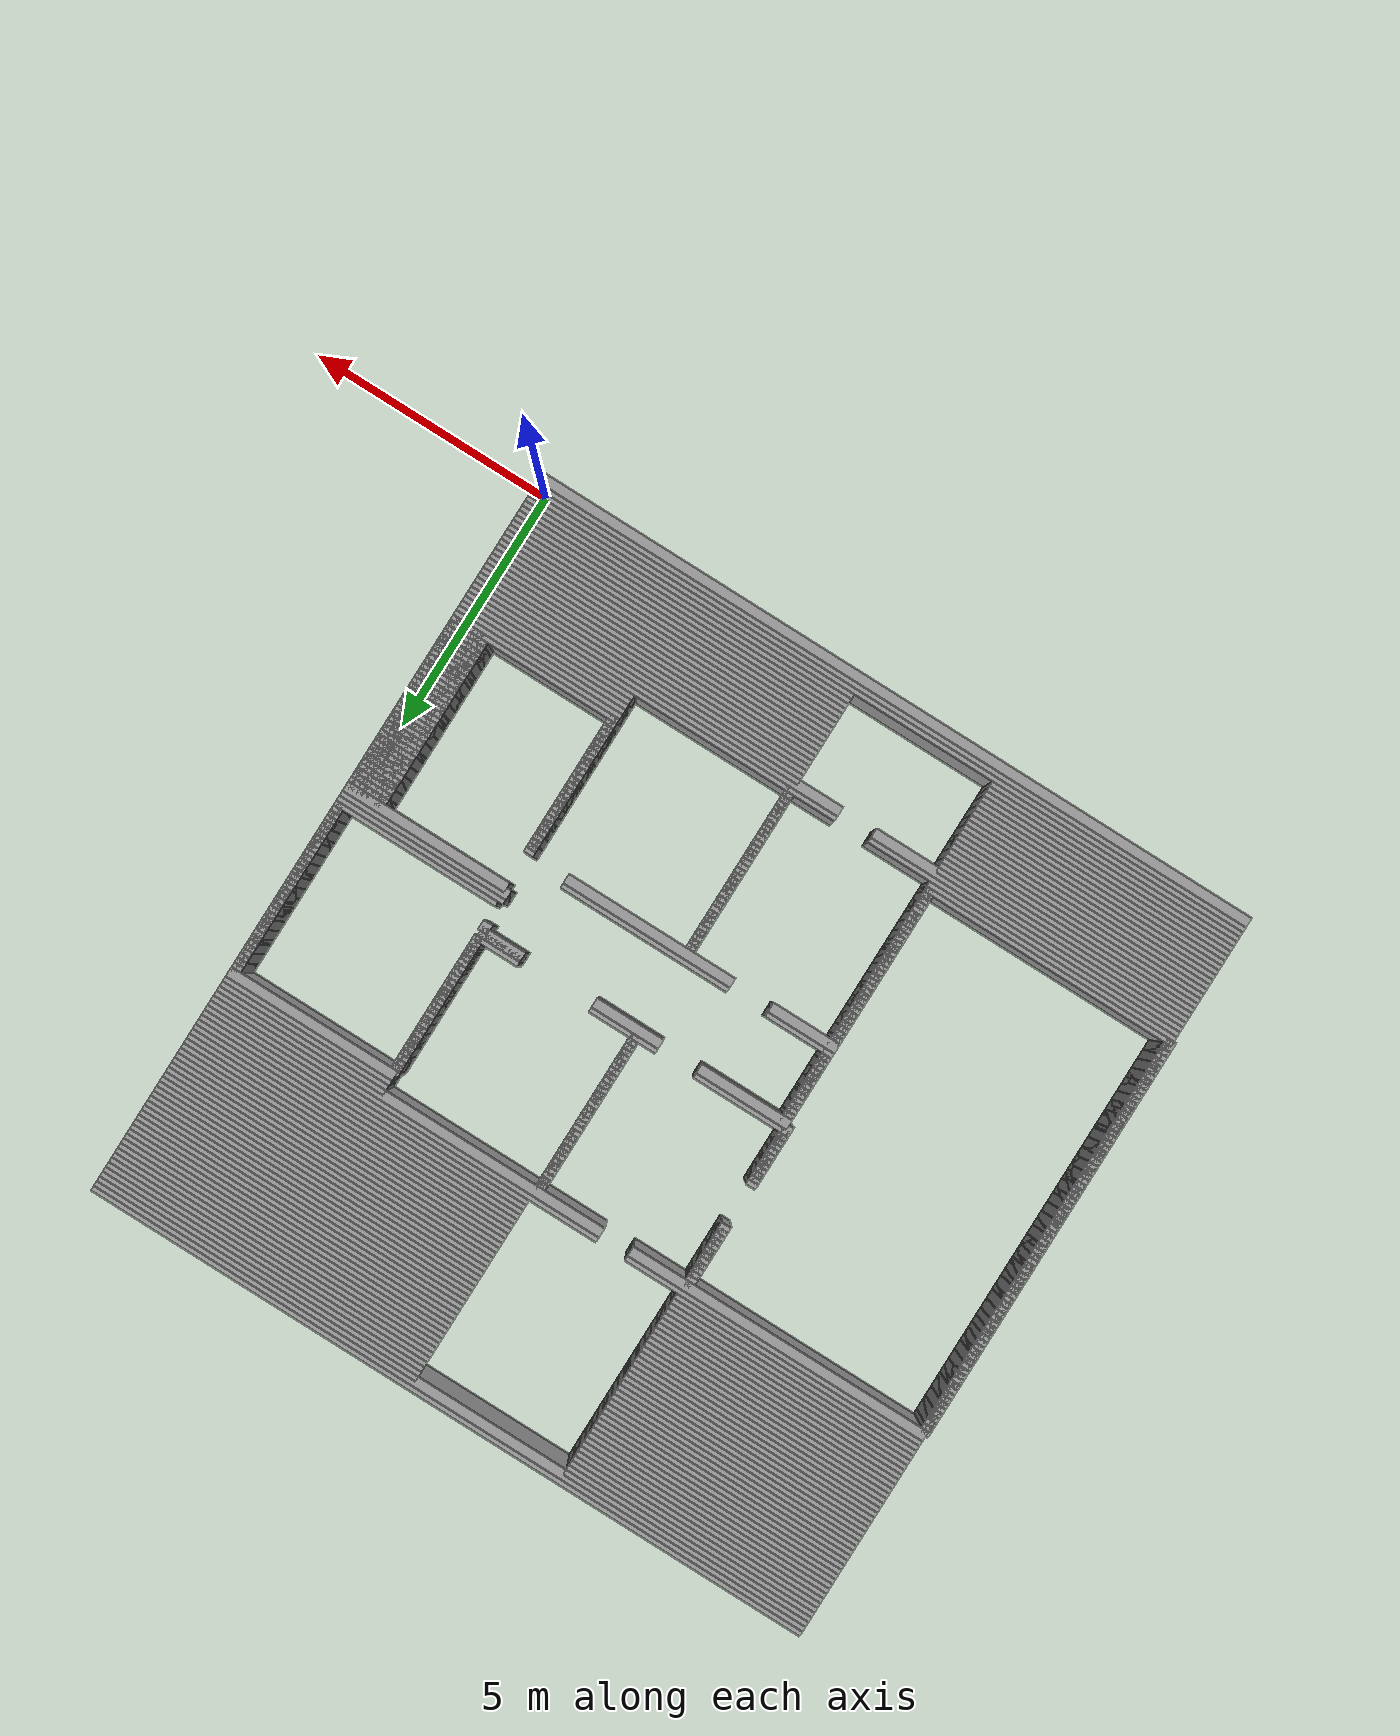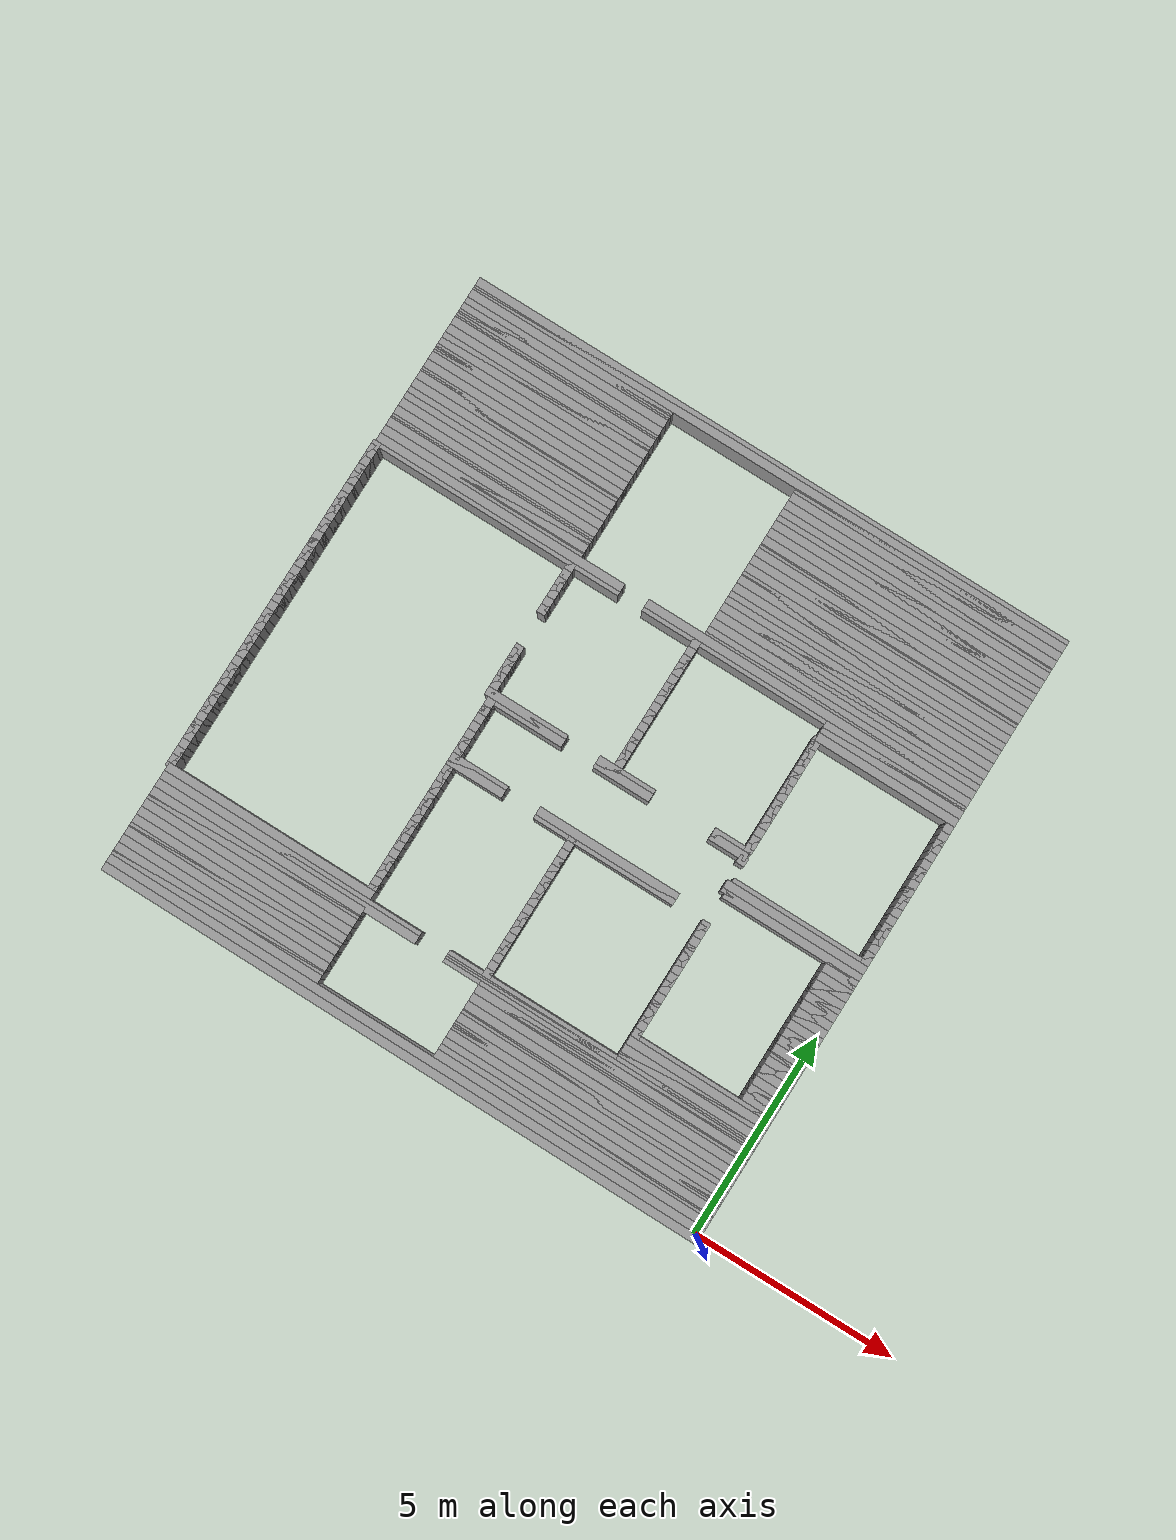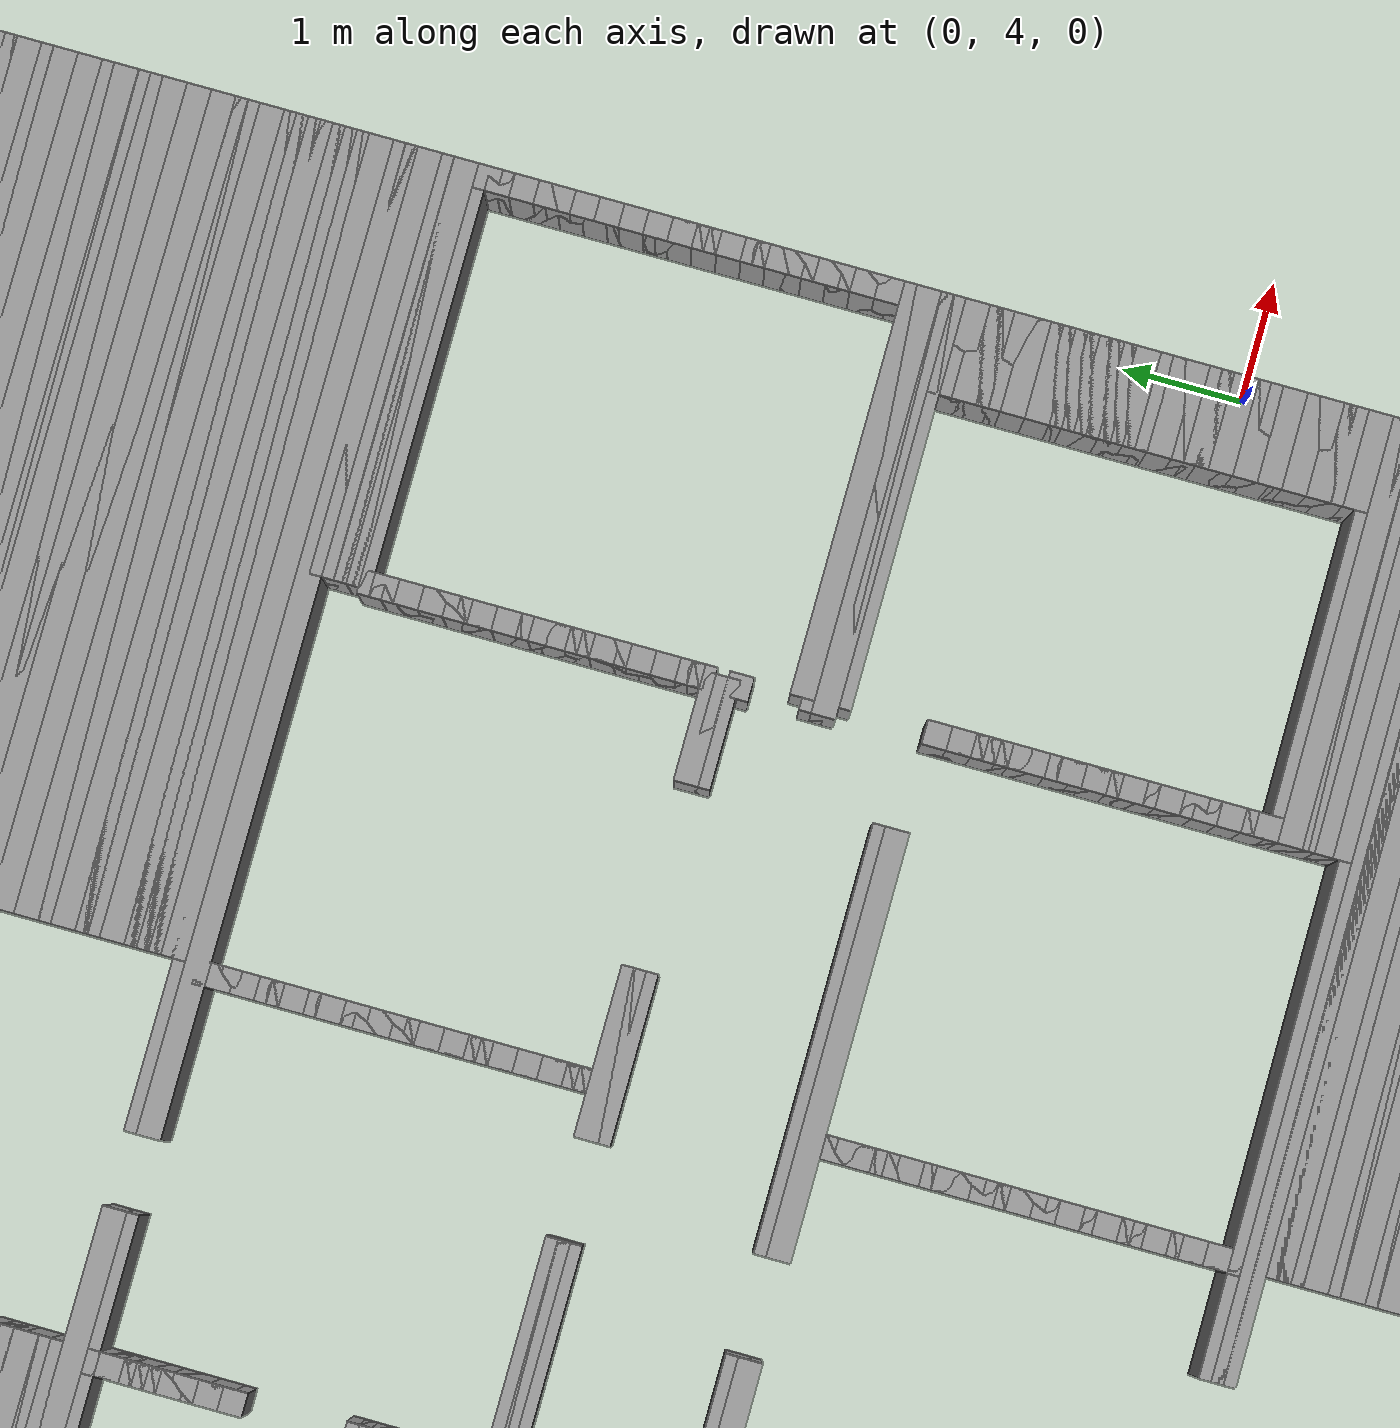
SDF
<?xml version='1.0' encoding='UTF-8'?>
<sdf version="1.6"><world name="GridMap"><model name="GridMap"><pose frame="">0 0 0 0 -0 0</pose><link name="Wall_(74.5,0.0)"><collision name="Wall_(74.5,0.0)_Collision"><geometry><box><size>14.9 0.2 1.0</size></box></geometry><pose frame="">-7.45 0.0 0.5 0 -0 0</pose></collision><visual name="Wall_(74.5,0.0)_Visual"><geometry><box><size>14.9 0.2 1.0</size></box></geometry><pose frame="">-7.45 0.0 0.5 0 -0 0</pose><material><script><uri>file://media/materials/scripts/gazebo.material</uri><name>Gazebo/Grey</name></script><ambient>1 1 1 1</ambient></material><meta><layer>0</layer></meta></visual><pose frame="">0 0 0.5 0 -0 0</pose></link><link name="Wall_(74.5,1.0)"><collision name="Wall_(74.5,1.0)_Collision"><geometry><box><size>14.9 0.2 1.0</size></box></geometry><pose frame="">-7.45 0.1 0.5 0 -0 0</pose></collision><visual name="Wall_(74.5,1.0)_Visual"><geometry><box><size>14.9 0.2 1.0</size></box></geometry><pose frame="">-7.45 0.1 0.5 0 -0 0</pose><material><script><uri>file://media/materials/scripts/gazebo.material</uri><name>Gazebo/Grey</name></script><ambient>1 1 1 1</ambient></material><meta><layer>0</layer></meta></visual><pose frame="">0 0 0.5 0 -0 0</pose></link><link name="Wall_(74.5,2.0)"><collision name="Wall_(74.5,2.0)_Collision"><geometry><box><size>14.9 0.2 1.0</size></box></geometry><pose frame="">-7.45 0.2 0.5 0 -0 0</pose></collision><visual name="Wall_(74.5,2.0)_Visual"><geometry><box><size>14.9 0.2 1.0</size></box></geometry><pose frame="">-7.45 0.2 0.5 0 -0 0</pose><material><script><uri>file://media/materials/scripts/gazebo.material</uri><name>Gazebo/Grey</name></script><ambient>1 1 1 1</ambient></material><meta><layer>0</layer></meta></visual><pose frame="">0 0 0.5 0 -0 0</pose></link><link name="Wall_(34.0,3.0)"><collision name="Wall_(34.0,3.0)_Collision"><geometry><box><size>6.800000000000001 0.2 1.0</size></box></geometry><pose frame="">-3.4000000000000004 0.30000000000000004 0.5 0 -0 0</pose></collision><visual name="Wall_(34.0,3.0)_Visual"><geometry><box><size>6.800000000000001 0.2 1.0</size></box></geometry><pose frame="">-3.4000000000000004 0.30000000000000004 0.5 0 -0 0</pose><material><script><uri>file://media/materials/scripts/gazebo.material</uri><name>Gazebo/Grey</name></script><ambient>1 1 1 1</ambient></material><meta><layer>0</layer></meta></visual><pose frame="">0 0 0.5 0 -0 0</pose></link><link name="Wall_(123.0,3.0)"><collision name="Wall_(123.0,3.0)_Collision"><geometry><box><size>5.2 0.2 1.0</size></box></geometry><pose frame="">-12.3 0.30000000000000004 0.5 0 -0 0</pose></collision><visual name="Wall_(123.0,3.0)_Visual"><geometry><box><size>5.2 0.2 1.0</size></box></geometry><pose frame="">-12.3 0.30000000000000004 0.5 0 -0 0</pose><material><script><uri>file://media/materials/scripts/gazebo.material</uri><name>Gazebo/Grey</name></script><ambient>1 1 1 1</ambient></material><meta><layer>0</layer></meta></visual><pose frame="">0 0 0.5 0 -0 0</pose></link><link name="Wall_(34.0,4.0)"><collision name="Wall_(34.0,4.0)_Collision"><geometry><box><size>6.800000000000001 0.2 1.0</size></box></geometry><pose frame="">-3.4000000000000004 0.4 0.5 0 -0 0</pose></collision><visual name="Wall_(34.0,4.0)_Visual"><geometry><box><size>6.800000000000001 0.2 1.0</size></box></geometry><pose frame="">-3.4000000000000004 0.4 0.5 0 -0 0</pose><material><script><uri>file://media/materials/scripts/gazebo.material</uri><name>Gazebo/Grey</name></script><ambient>1 1 1 1</ambient></material><meta><layer>0</layer></meta></visual><pose frame="">0 0 0.5 0 -0 0</pose></link><link name="Wall_(123.0,4.0)"><collision name="Wall_(123.0,4.0)_Collision"><geometry><box><size>5.2 0.2 1.0</size></box></geometry><pose frame="">-12.3 0.4 0.5 0 -0 0</pose></collision><visual name="Wall_(123.0,4.0)_Visual"><geometry><box><size>5.2 0.2 1.0</size></box></geometry><pose frame="">-12.3 0.4 0.5 0 -0 0</pose><material><script><uri>file://media/materials/scripts/gazebo.material</uri><name>Gazebo/Grey</name></script><ambient>1 1 1 1</ambient></material><meta><layer>0</layer></meta></visual><pose frame="">0 0 0.5 0 -0 0</pose></link><link name="Wall_(34.0,5.0)"><collision name="Wall_(34.0,5.0)_Collision"><geometry><box><size>6.800000000000001 0.2 1.0</size></box></geometry><pose frame="">-3.4000000000000004 0.5 0.5 0 -0 0</pose></collision><visual name="Wall_(34.0,5.0)_Visual"><geometry><box><size>6.800000000000001 0.2 1.0</size></box></geometry><pose frame="">-3.4000000000000004 0.5 0.5 0 -0 0</pose><material><script><uri>file://media/materials/scripts/gazebo.material</uri><name>Gazebo/Grey</name></script><ambient>1 1 1 1</ambient></material><meta><layer>0</layer></meta></visual><pose frame="">0 0 0.5 0 -0 0</pose></link><link name="Wall_(123.0,5.0)"><collision name="Wall_(123.0,5.0)_Collision"><geometry><box><size>5.2 0.2 1.0</size></box></geometry><pose frame="">-12.3 0.5 0.5 0 -0 0</pose></collision><visual name="Wall_(123.0,5.0)_Visual"><geometry><box><size>5.2 0.2 1.0</size></box></geometry><pose frame="">-12.3 0.5 0.5 0 -0 0</pose><material><script><uri>file://media/materials/scripts/gazebo.material</uri><name>Gazebo/Grey</name></script><ambient>1 1 1 1</ambient></material><meta><layer>0</layer></meta></visual><pose frame="">0 0 0.5 0 -0 0</pose></link><link name="Wall_(34.0,6.0)"><collision name="Wall_(34.0,6.0)_Collision"><geometry><box><size>6.800000000000001 0.2 1.0</size></box></geometry><pose frame="">-3.4000000000000004 0.6000000000000001 0.5 0 -0 0</pose></collision><visual name="Wall_(34.0,6.0)_Visual"><geometry><box><size>6.800000000000001 0.2 1.0</size></box></geometry><pose frame="">-3.4000000000000004 0.6000000000000001 0.5 0 -0 0</pose><material><script><uri>file://media/materials/scripts/gazebo.material</uri><name>Gazebo/Grey</name></script><ambient>1 1 1 1</ambient></material><meta><layer>0</layer></meta></visual><pose frame="">0 0 0.5 0 -0 0</pose></link><link name="Wall_(123.0,6.0)"><collision name="Wall_(123.0,6.0)_Collision"><geometry><box><size>5.2 0.2 1.0</size></box></geometry><pose frame="">-12.3 0.6000000000000001 0.5 0 -0 0</pose></collision><visual name="Wall_(123.0,6.0)_Visual"><geometry><box><size>5.2 0.2 1.0</size></box></geometry><pose frame="">-12.3 0.6000000000000001 0.5 0 -0 0</pose><material><script><uri>file://media/materials/scripts/gazebo.material</uri><name>Gazebo/Grey</name></script><ambient>1 1 1 1</ambient></material><meta><layer>0</layer></meta></visual><pose frame="">0 0 0.5 0 -0 0</pose></link><link name="Wall_(34.0,7.0)"><collision name="Wall_(34.0,7.0)_Collision"><geometry><box><size>6.800000000000001 0.2 1.0</size></box></geometry><pose frame="">-3.4000000000000004 0.7000000000000001 0.5 0 -0 0</pose></collision><visual name="Wall_(34.0,7.0)_Visual"><geometry><box><size>6.800000000000001 0.2 1.0</size></box></geometry><pose frame="">-3.4000000000000004 0.7000000000000001 0.5 0 -0 0</pose><material><script><uri>file://media/materials/scripts/gazebo.material</uri><name>Gazebo/Grey</name></script><ambient>1 1 1 1</ambient></material><meta><layer>0</layer></meta></visual><pose frame="">0 0 0.5 0 -0 0</pose></link><link name="Wall_(123.0,7.0)"><collision name="Wall_(123.0,7.0)_Collision"><geometry><box><size>5.2 0.2 1.0</size></box></geometry><pose frame="">-12.3 0.7000000000000001 0.5 0 -0 0</pose></collision><visual name="Wall_(123.0,7.0)_Visual"><geometry><box><size>5.2 0.2 1.0</size></box></geometry><pose frame="">-12.3 0.7000000000000001 0.5 0 -0 0</pose><material><script><uri>file://media/materials/scripts/gazebo.material</uri><name>Gazebo/Grey</name></script><ambient>1 1 1 1</ambient></material><meta><layer>0</layer></meta></visual><pose frame="">0 0 0.5 0 -0 0</pose></link><link name="Wall_(34.0,8.0)"><collision name="Wall_(34.0,8.0)_Collision"><geometry><box><size>6.800000000000001 0.2 1.0</size></box></geometry><pose frame="">-3.4000000000000004 0.8 0.5 0 -0 0</pose></collision><visual name="Wall_(34.0,8.0)_Visual"><geometry><box><size>6.800000000000001 0.2 1.0</size></box></geometry><pose frame="">-3.4000000000000004 0.8 0.5 0 -0 0</pose><material><script><uri>file://media/materials/scripts/gazebo.material</uri><name>Gazebo/Grey</name></script><ambient>1 1 1 1</ambient></material><meta><layer>0</layer></meta></visual><pose frame="">0 0 0.5 0 -0 0</pose></link><link name="Wall_(123.0,8.0)"><collision name="Wall_(123.0,8.0)_Collision"><geometry><box><size>5.2 0.2 1.0</size></box></geometry><pose frame="">-12.3 0.8 0.5 0 -0 0</pose></collision><visual name="Wall_(123.0,8.0)_Visual"><geometry><box><size>5.2 0.2 1.0</size></box></geometry><pose frame="">-12.3 0.8 0.5 0 -0 0</pose><material><script><uri>file://media/materials/scripts/gazebo.material</uri><name>Gazebo/Grey</name></script><ambient>1 1 1 1</ambient></material><meta><layer>0</layer></meta></visual><pose frame="">0 0 0.5 0 -0 0</pose></link><link name="Wall_(34.0,9.0)"><collision name="Wall_(34.0,9.0)_Collision"><geometry><box><size>6.800000000000001 0.2 1.0</size></box></geometry><pose frame="">-3.4000000000000004 0.9 0.5 0 -0 0</pose></collision><visual name="Wall_(34.0,9.0)_Visual"><geometry><box><size>6.800000000000001 0.2 1.0</size></box></geometry><pose frame="">-3.4000000000000004 0.9 0.5 0 -0 0</pose><material><script><uri>file://media/materials/scripts/gazebo.material</uri><name>Gazebo/Grey</name></script><ambient>1 1 1 1</ambient></material><meta><layer>0</layer></meta></visual><pose frame="">0 0 0.5 0 -0 0</pose></link><link name="Wall_(123.0,9.0)"><collision name="Wall_(123.0,9.0)_Collision"><geometry><box><size>5.2 0.2 1.0</size></box></geometry><pose frame="">-12.3 0.9 0.5 0 -0 0</pose></collision><visual name="Wall_(123.0,9.0)_Visual"><geometry><box><size>5.2 0.2 1.0</size></box></geometry><pose frame="">-12.3 0.9 0.5 0 -0 0</pose><material><script><uri>file://media/materials/scripts/gazebo.material</uri><name>Gazebo/Grey</name></script><ambient>1 1 1 1</ambient></material><meta><layer>0</layer></meta></visual><pose frame="">0 0 0.5 0 -0 0</pose></link><link name="Wall_(34.0,10.0)"><collision name="Wall_(34.0,10.0)_Collision"><geometry><box><size>6.800000000000001 0.2 1.0</size></box></geometry><pose frame="">-3.4000000000000004 1.0 0.5 0 -0 0</pose></collision><visual name="Wall_(34.0,10.0)_Visual"><geometry><box><size>6.800000000000001 0.2 1.0</size></box></geometry><pose frame="">-3.4000000000000004 1.0 0.5 0 -0 0</pose><material><script><uri>file://media/materials/scripts/gazebo.material</uri><name>Gazebo/Grey</name></script><ambient>1 1 1 1</ambient></material><meta><layer>0</layer></meta></visual><pose frame="">0 0 0.5 0 -0 0</pose></link><link name="Wall_(123.0,10.0)"><collision name="Wall_(123.0,10.0)_Collision"><geometry><box><size>5.2 0.2 1.0</size></box></geometry><pose frame="">-12.3 1.0 0.5 0 -0 0</pose></collision><visual name="Wall_(123.0,10.0)_Visual"><geometry><box><size>5.2 0.2 1.0</size></box></geometry><pose frame="">-12.3 1.0 0.5 0 -0 0</pose><material><script><uri>file://media/materials/scripts/gazebo.material</uri><name>Gazebo/Grey</name></script><ambient>1 1 1 1</ambient></material><meta><layer>0</layer></meta></visual><pose frame="">0 0 0.5 0 -0 0</pose></link><link name="Wall_(34.0,11.0)"><collision name="Wall_(34.0,11.0)_Collision"><geometry><box><size>6.800000000000001 0.2 1.0</size></box></geometry><pose frame="">-3.4000000000000004 1.1 0.5 0 -0 0</pose></collision><visual name="Wall_(34.0,11.0)_Visual"><geometry><box><size>6.800000000000001 0.2 1.0</size></box></geometry><pose frame="">-3.4000000000000004 1.1 0.5 0 -0 0</pose><material><script><uri>file://media/materials/scripts/gazebo.material</uri><name>Gazebo/Grey</name></script><ambient>1 1 1 1</ambient></material><meta><layer>0</layer></meta></visual><pose frame="">0 0 0.5 0 -0 0</pose></link><link name="Wall_(123.0,11.0)"><collision name="Wall_(123.0,11.0)_Collision"><geometry><box><size>5.2 0.2 1.0</size></box></geometry><pose frame="">-12.3 1.1 0.5 0 -0 0</pose></collision><visual name="Wall_(123.0,11.0)_Visual"><geometry><box><size>5.2 0.2 1.0</size></box></geometry><pose frame="">-12.3 1.1 0.5 0 -0 0</pose><material><script><uri>file://media/materials/scripts/gazebo.material</uri><name>Gazebo/Grey</name></script><ambient>1 1 1 1</ambient></material><meta><layer>0</layer></meta></visual><pose frame="">0 0 0.5 0 -0 0</pose></link><link name="Wall_(34.0,12.0)"><collision name="Wall_(34.0,12.0)_Collision"><geometry><box><size>6.800000000000001 0.2 1.0</size></box></geometry><pose frame="">-3.4000000000000004 1.2000000000000002 0.5 0 -0 0</pose></collision><visual name="Wall_(34.0,12.0)_Visual"><geometry><box><size>6.800000000000001 0.2 1.0</size></box></geometry><pose frame="">-3.4000000000000004 1.2000000000000002 0.5 0 -0 0</pose><material><script><uri>file://media/materials/scripts/gazebo.material</uri><name>Gazebo/Grey</name></script><ambient>1 1 1 1</ambient></material><meta><layer>0</layer></meta></visual><pose frame="">0 0 0.5 0 -0 0</pose></link><link name="Wall_(123.0,12.0)"><collision name="Wall_(123.0,12.0)_Collision"><geometry><box><size>5.2 0.2 1.0</size></box></geometry><pose frame="">-12.3 1.2000000000000002 0.5 0 -0 0</pose></collision><visual name="Wall_(123.0,12.0)_Visual"><geometry><box><size>5.2 0.2 1.0</size></box></geometry><pose frame="">-12.3 1.2000000000000002 0.5 0 -0 0</pose><material><script><uri>file://media/materials/scripts/gazebo.material</uri><name>Gazebo/Grey</name></script><ambient>1 1 1 1</ambient></material><meta><layer>0</layer></meta></visual><pose frame="">0 0 0.5 0 -0 0</pose></link><link name="Wall_(34.0,13.0)"><collision name="Wall_(34.0,13.0)_Collision"><geometry><box><size>6.800000000000001 0.2 1.0</size></box></geometry><pose frame="">-3.4000000000000004 1.3 0.5 0 -0 0</pose></collision><visual name="Wall_(34.0,13.0)_Visual"><geometry><box><size>6.800000000000001 0.2 1.0</size></box></geometry><pose frame="">-3.4000000000000004 1.3 0.5 0 -0 0</pose><material><script><uri>file://media/materials/scripts/gazebo.material</uri><name>Gazebo/Grey</name></script><ambient>1 1 1 1</ambient></material><meta><layer>0</layer></meta></visual><pose frame="">0 0 0.5 0 -0 0</pose></link><link name="Wall_(123.0,13.0)"><collision name="Wall_(123.0,13.0)_Collision"><geometry><box><size>5.2 0.2 1.0</size></box></geometry><pose frame="">-12.3 1.3 0.5 0 -0 0</pose></collision><visual name="Wall_(123.0,13.0)_Visual"><geometry><box><size>5.2 0.2 1.0</size></box></geometry><pose frame="">-12.3 1.3 0.5 0 -0 0</pose><material><script><uri>file://media/materials/scripts/gazebo.material</uri><name>Gazebo/Grey</name></script><ambient>1 1 1 1</ambient></material><meta><layer>0</layer></meta></visual><pose frame="">0 0 0.5 0 -0 0</pose></link><link name="Wall_(34.0,14.0)"><collision name="Wall_(34.0,14.0)_Collision"><geometry><box><size>6.800000000000001 0.2 1.0</size></box></geometry><pose frame="">-3.4000000000000004 1.4000000000000001 0.5 0 -0 0</pose></collision><visual name="Wall_(34.0,14.0)_Visual"><geometry><box><size>6.800000000000001 0.2 1.0</size></box></geometry><pose frame="">-3.4000000000000004 1.4000000000000001 0.5 0 -0 0</pose><material><script><uri>file://media/materials/scripts/gazebo.material</uri><name>Gazebo/Grey</name></script><ambient>1 1 1 1</ambient></material><meta><layer>0</layer></meta></visual><pose frame="">0 0 0.5 0 -0 0</pose></link><link name="Wall_(123.0,14.0)"><collision name="Wall_(123.0,14.0)_Collision"><geometry><box><size>5.2 0.2 1.0</size></box></geometry><pose frame="">-12.3 1.4000000000000001 0.5 0 -0 0</pose></collision><visual name="Wall_(123.0,14.0)_Visual"><geometry><box><size>5.2 0.2 1.0</size></box></geometry><pose frame="">-12.3 1.4000000000000001 0.5 0 -0 0</pose><material><script><uri>file://media/materials/scripts/gazebo.material</uri><name>Gazebo/Grey</name></script><ambient>1 1 1 1</ambient></material><meta><layer>0</layer></meta></visual><pose frame="">0 0 0.5 0 -0 0</pose></link><link name="Wall_(34.0,15.0)"><collision name="Wall_(34.0,15.0)_Collision"><geometry><box><size>6.800000000000001 0.2 1.0</size></box></geometry><pose frame="">-3.4000000000000004 1.5 0.5 0 -0 0</pose></collision><visual name="Wall_(34.0,15.0)_Visual"><geometry><box><size>6.800000000000001 0.2 1.0</size></box></geometry><pose frame="">-3.4000000000000004 1.5 0.5 0 -0 0</pose><material><script><uri>file://media/materials/scripts/gazebo.material</uri><name>Gazebo/Grey</name></script><ambient>1 1 1 1</ambient></material><meta><layer>0</layer></meta></visual><pose frame="">0 0 0.5 0 -0 0</pose></link><link name="Wall_(123.0,15.0)"><collision name="Wall_(123.0,15.0)_Collision"><geometry><box><size>5.2 0.2 1.0</size></box></geometry><pose frame="">-12.3 1.5 0.5 0 -0 0</pose></collision><visual name="Wall_(123.0,15.0)_Visual"><geometry><box><size>5.2 0.2 1.0</size></box></geometry><pose frame="">-12.3 1.5 0.5 0 -0 0</pose><material><script><uri>file://media/materials/scripts/gazebo.material</uri><name>Gazebo/Grey</name></script><ambient>1 1 1 1</ambient></material><meta><layer>0</layer></meta></visual><pose frame="">0 0 0.5 0 -0 0</pose></link><link name="Wall_(34.0,16.0)"><collision name="Wall_(34.0,16.0)_Collision"><geometry><box><size>6.800000000000001 0.2 1.0</size></box></geometry><pose frame="">-3.4000000000000004 1.6 0.5 0 -0 0</pose></collision><visual name="Wall_(34.0,16.0)_Visual"><geometry><box><size>6.800000000000001 0.2 1.0</size></box></geometry><pose frame="">-3.4000000000000004 1.6 0.5 0 -0 0</pose><material><script><uri>file://media/materials/scripts/gazebo.material</uri><name>Gazebo/Grey</name></script><ambient>1 1 1 1</ambient></material><meta><layer>0</layer></meta></visual><pose frame="">0 0 0.5 0 -0 0</pose></link><link name="Wall_(123.0,16.0)"><collision name="Wall_(123.0,16.0)_Collision"><geometry><box><size>5.2 0.2 1.0</size></box></geometry><pose frame="">-12.3 1.6 0.5 0 -0 0</pose></collision><visual name="Wall_(123.0,16.0)_Visual"><geometry><box><size>5.2 0.2 1.0</size></box></geometry><pose frame="">-12.3 1.6 0.5 0 -0 0</pose><material><script><uri>file://media/materials/scripts/gazebo.material</uri><name>Gazebo/Grey</name></script><ambient>1 1 1 1</ambient></material><meta><layer>0</layer></meta></visual><pose frame="">0 0 0.5 0 -0 0</pose></link><link name="Wall_(34.0,17.0)"><collision name="Wall_(34.0,17.0)_Collision"><geometry><box><size>6.800000000000001 0.2 1.0</size></box></geometry><pose frame="">-3.4000000000000004 1.7000000000000002 0.5 0 -0 0</pose></collision><visual name="Wall_(34.0,17.0)_Visual"><geometry><box><size>6.800000000000001 0.2 1.0</size></box></geometry><pose frame="">-3.4000000000000004 1.7000000000000002 0.5 0 -0 0</pose><material><script><uri>file://media/materials/scripts/gazebo.material</uri><name>Gazebo/Grey</name></script><ambient>1 1 1 1</ambient></material><meta><layer>0</layer></meta></visual><pose frame="">0 0 0.5 0 -0 0</pose></link><link name="Wall_(123.0,17.0)"><collision name="Wall_(123.0,17.0)_Collision"><geometry><box><size>5.2 0.2 1.0</size></box></geometry><pose frame="">-12.3 1.7000000000000002 0.5 0 -0 0</pose></collision><visual name="Wall_(123.0,17.0)_Visual"><geometry><box><size>5.2 0.2 1.0</size></box></geometry><pose frame="">-12.3 1.7000000000000002 0.5 0 -0 0</pose><material><script><uri>file://media/materials/scripts/gazebo.material</uri><name>Gazebo/Grey</name></script><ambient>1 1 1 1</ambient></material><meta><layer>0</layer></meta></visual><pose frame="">0 0 0.5 0 -0 0</pose></link><link name="Wall_(34.0,18.0)"><collision name="Wall_(34.0,18.0)_Collision"><geometry><box><size>6.800000000000001 0.2 1.0</size></box></geometry><pose frame="">-3.4000000000000004 1.8 0.5 0 -0 0</pose></collision><visual name="Wall_(34.0,18.0)_Visual"><geometry><box><size>6.800000000000001 0.2 1.0</size></box></geometry><pose frame="">-3.4000000000000004 1.8 0.5 0 -0 0</pose><material><script><uri>file://media/materials/scripts/gazebo.material</uri><name>Gazebo/Grey</name></script><ambient>1 1 1 1</ambient></material><meta><layer>0</layer></meta></visual><pose frame="">0 0 0.5 0 -0 0</pose></link><link name="Wall_(123.0,18.0)"><collision name="Wall_(123.0,18.0)_Collision"><geometry><box><size>5.2 0.2 1.0</size></box></geometry><pose frame="">-12.3 1.8 0.5 0 -0 0</pose></collision><visual name="Wall_(123.0,18.0)_Visual"><geometry><box><size>5.2 0.2 1.0</size></box></geometry><pose frame="">-12.3 1.8 0.5 0 -0 0</pose><material><script><uri>file://media/materials/scripts/gazebo.material</uri><name>Gazebo/Grey</name></script><ambient>1 1 1 1</ambient></material><meta><layer>0</layer></meta></visual><pose frame="">0 0 0.5 0 -0 0</pose></link><link name="Wall_(34.0,19.0)"><collision name="Wall_(34.0,19.0)_Collision"><geometry><box><size>6.800000000000001 0.2 1.0</size></box></geometry><pose frame="">-3.4000000000000004 1.9000000000000001 0.5 0 -0 0</pose></collision><visual name="Wall_(34.0,19.0)_Visual"><geometry><box><size>6.800000000000001 0.2 1.0</size></box></geometry><pose frame="">-3.4000000000000004 1.9000000000000001 0.5 0 -0 0</pose><material><script><uri>file://media/materials/scripts/gazebo.material</uri><name>Gazebo/Grey</name></script><ambient>1 1 1 1</ambient></material><meta><layer>0</layer></meta></visual><pose frame="">0 0 0.5 0 -0 0</pose></link><link name="Wall_(123.0,19.0)"><collision name="Wall_(123.0,19.0)_Collision"><geometry><box><size>5.2 0.2 1.0</size></box></geometry><pose frame="">-12.3 1.9000000000000001 0.5 0 -0 0</pose></collision><visual name="Wall_(123.0,19.0)_Visual"><geometry><box><size>5.2 0.2 1.0</size></box></geometry><pose frame="">-12.3 1.9000000000000001 0.5 0 -0 0</pose><material><script><uri>file://media/materials/scripts/gazebo.material</uri><name>Gazebo/Grey</name></script><ambient>1 1 1 1</ambient></material><meta><layer>0</layer></meta></visual><pose frame="">0 0 0.5 0 -0 0</pose></link><link name="Wall_(34.0,20.0)"><collision name="Wall_(34.0,20.0)_Collision"><geometry><box><size>6.800000000000001 0.2 1.0</size></box></geometry><pose frame="">-3.4000000000000004 2.0 0.5 0 -0 0</pose></collision><visual name="Wall_(34.0,20.0)_Visual"><geometry><box><size>6.800000000000001 0.2 1.0</size></box></geometry><pose frame="">-3.4000000000000004 2.0 0.5 0 -0 0</pose><material><script><uri>file://media/materials/scripts/gazebo.material</uri><name>Gazebo/Grey</name></script><ambient>1 1 1 1</ambient></material><meta><layer>0</layer></meta></visual><pose frame="">0 0 0.5 0 -0 0</pose></link><link name="Wall_(123.0,20.0)"><collision name="Wall_(123.0,20.0)_Collision"><geometry><box><size>5.2 0.2 1.0</size></box></geometry><pose frame="">-12.3 2.0 0.5 0 -0 0</pose></collision><visual name="Wall_(123.0,20.0)_Visual"><geometry><box><size>5.2 0.2 1.0</size></box></geometry><pose frame="">-12.3 2.0 0.5 0 -0 0</pose><material><script><uri>file://media/materials/scripts/gazebo.material</uri><name>Gazebo/Grey</name></script><ambient>1 1 1 1</ambient></material><meta><layer>0</layer></meta></visual><pose frame="">0 0 0.5 0 -0 0</pose></link><link name="Wall_(34.0,21.0)"><collision name="Wall_(34.0,21.0)_Collision"><geometry><box><size>6.800000000000001 0.2 1.0</size></box></geometry><pose frame="">-3.4000000000000004 2.1 0.5 0 -0 0</pose></collision><visual name="Wall_(34.0,21.0)_Visual"><geometry><box><size>6.800000000000001 0.2 1.0</size></box></geometry><pose frame="">-3.4000000000000004 2.1 0.5 0 -0 0</pose><material><script><uri>file://media/materials/scripts/gazebo.material</uri><name>Gazebo/Grey</name></script><ambient>1 1 1 1</ambient></material><meta><layer>0</layer></meta></visual><pose frame="">0 0 0.5 0 -0 0</pose></link><link name="Wall_(123.0,21.0)"><collision name="Wall_(123.0,21.0)_Collision"><geometry><box><size>5.2 0.2 1.0</size></box></geometry><pose frame="">-12.3 2.1 0.5 0 -0 0</pose></collision><visual name="Wall_(123.0,21.0)_Visual"><geometry><box><size>5.2 0.2 1.0</size></box></geometry><pose frame="">-12.3 2.1 0.5 0 -0 0</pose><material><script><uri>file://media/materials/scripts/gazebo.material</uri><name>Gazebo/Grey</name></script><ambient>1 1 1 1</ambient></material><meta><layer>0</layer></meta></visual><pose frame="">0 0 0.5 0 -0 0</pose></link><link name="Wall_(38.5,22.0)"><collision name="Wall_(38.5,22.0)_Collision"><geometry><box><size>7.7 0.2 1.0</size></box></geometry><pose frame="">-3.85 2.2 0.5 0 -0 0</pose></collision><visual name="Wall_(38.5,22.0)_Visual"><geometry><box><size>7.7 0.2 1.0</size></box></geometry><pose frame="">-3.85 2.2 0.5 0 -0 0</pose><material><script><uri>file://media/materials/scripts/gazebo.material</uri><name>Gazebo/Grey</name></script><ambient>1 1 1 1</ambient></material><meta><layer>0</layer></meta></visual><pose frame="">0 0 0.5 0 -0 0</pose></link><link name="Wall_(116.5,22.0)"><collision name="Wall_(116.5,22.0)_Collision"><geometry><box><size>6.5 0.2 1.0</size></box></geometry><pose frame="">-11.65 2.2 0.5 0 -0 0</pose></collision><visual name="Wall_(116.5,22.0)_Visual"><geometry><box><size>6.5 0.2 1.0</size></box></geometry><pose frame="">-11.65 2.2 0.5 0 -0 0</pose><material><script><uri>file://media/materials/scripts/gazebo.material</uri><name>Gazebo/Grey</name></script><ambient>1 1 1 1</ambient></material><meta><layer>0</layer></meta></visual><pose frame="">0 0 0.5 0 -0 0</pose></link><link name="Wall_(38.5,23.0)"><collision name="Wall_(38.5,23.0)_Collision"><geometry><box><size>7.7 0.2 1.0</size></box></geometry><pose frame="">-3.85 2.3000000000000003 0.5 0 -0 0</pose></collision><visual name="Wall_(38.5,23.0)_Visual"><geometry><box><size>7.7 0.2 1.0</size></box></geometry><pose frame="">-3.85 2.3000000000000003 0.5 0 -0 0</pose><material><script><uri>file://media/materials/scripts/gazebo.material</uri><name>Gazebo/Grey</name></script><ambient>1 1 1 1</ambient></material><meta><layer>0</layer></meta></visual><pose frame="">0 0 0.5 0 -0 0</pose></link><link name="Wall_(116.5,23.0)"><collision name="Wall_(116.5,23.0)_Collision"><geometry><box><size>6.5 0.2 1.0</size></box></geometry><pose frame="">-11.65 2.3000000000000003 0.5 0 -0 0</pose></collision><visual name="Wall_(116.5,23.0)_Visual"><geometry><box><size>6.5 0.2 1.0</size></box></geometry><pose frame="">-11.65 2.3000000000000003 0.5 0 -0 0</pose><material><script><uri>file://media/materials/scripts/gazebo.material</uri><name>Gazebo/Grey</name></script><ambient>1 1 1 1</ambient></material><meta><layer>0</layer></meta></visual><pose frame="">0 0 0.5 0 -0 0</pose></link><link name="Wall_(17.5,24.0)"><collision name="Wall_(17.5,24.0)_Collision"><geometry><box><size>3.5 0.2 1.0</size></box></geometry><pose frame="">-1.75 2.4000000000000004 0.5 0 -0 0</pose></collision><visual name="Wall_(17.5,24.0)_Visual"><geometry><box><size>3.5 0.2 1.0</size></box></geometry><pose frame="">-1.75 2.4000000000000004 0.5 0 -0 0</pose><material><script><uri>file://media/materials/scripts/gazebo.material</uri><name>Gazebo/Grey</name></script><ambient>1 1 1 1</ambient></material><meta><layer>0</layer></meta></visual><pose frame="">0 0 0.5 0 -0 0</pose></link><link name="Wall_(67.5,24.0)"><collision name="Wall_(67.5,24.0)_Collision"><geometry><box><size>0.2 0.2 1.0</size></box></geometry><pose frame="">-6.75 2.4000000000000004 0.5 0 -0 0</pose></collision><visual name="Wall_(67.5,24.0)_Visual"><geometry><box><size>0.2 0.2 1.0</size></box></geometry><pose frame="">-6.75 2.4000000000000004 0.5 0 -0 0</pose><material><script><uri>file://media/materials/scripts/gazebo.material</uri><name>Gazebo/Grey</name></script><ambient>1 1 1 1</ambient></material><meta><layer>0</layer></meta></visual><pose frame="">0 0 0.5 0 -0 0</pose></link><link name="Wall_(123.0,24.0)"><collision name="Wall_(123.0,24.0)_Collision"><geometry><box><size>5.2 0.2 1.0</size></box></geometry><pose frame="">-12.3 2.4000000000000004 0.5 0 -0 0</pose></collision><visual name="Wall_(123.0,24.0)_Visual"><geometry><box><size>5.2 0.2 1.0</size></box></geometry><pose frame="">-12.3 2.4000000000000004 0.5 0 -0 0</pose><material><script><uri>file://media/materials/scripts/gazebo.material</uri><name>Gazebo/Grey</name></script><ambient>1 1 1 1</ambient></material><meta><layer>0</layer></meta></visual><pose frame="">0 0 0.5 0 -0 0</pose></link><link name="Wall_(17.5,25.0)"><collision name="Wall_(17.5,25.0)_Collision"><geometry><box><size>3.5 0.2 1.0</size></box></geometry><pose frame="">-1.75 2.5 0.5 0 -0 0</pose></collision><visual name="Wall_(17.5,25.0)_Visual"><geometry><box><size>3.5 0.2 1.0</size></box></geometry><pose frame="">-1.75 2.5 0.5 0 -0 0</pose><material><script><uri>file://media/materials/scripts/gazebo.material</uri><name>Gazebo/Grey</name></script><ambient>1 1 1 1</ambient></material><meta><layer>0</layer></meta></visual><pose frame="">0 0 0.5 0 -0 0</pose></link><link name="Wall_(67.5,25.0)"><collision name="Wall_(67.5,25.0)_Collision"><geometry><box><size>0.2 0.2 1.0</size></box></geometry><pose frame="">-6.75 2.5 0.5 0 -0 0</pose></collision><visual name="Wall_(67.5,25.0)_Visual"><geometry><box><size>0.2 0.2 1.0</size></box></geometry><pose frame="">-6.75 2.5 0.5 0 -0 0</pose><material><script><uri>file://media/materials/scripts/gazebo.material</uri><name>Gazebo/Grey</name></script><ambient>1 1 1 1</ambient></material><meta><layer>0</layer></meta></visual><pose frame="">0 0 0.5 0 -0 0</pose></link><link name="Wall_(123.0,25.0)"><collision name="Wall_(123.0,25.0)_Collision"><geometry><box><size>5.2 0.2 1.0</size></box></geometry><pose frame="">-12.3 2.5 0.5 0 -0 0</pose></collision><visual name="Wall_(123.0,25.0)_Visual"><geometry><box><size>5.2 0.2 1.0</size></box></geometry><pose frame="">-12.3 2.5 0.5 0 -0 0</pose><material><script><uri>file://media/materials/scripts/gazebo.material</uri><name>Gazebo/Grey</name></script><ambient>1 1 1 1</ambient></material><meta><layer>0</layer></meta></visual><pose frame="">0 0 0.5 0 -0 0</pose></link><link name="Wall_(17.5,26.0)"><collision name="Wall_(17.5,26.0)_Collision"><geometry><box><size>3.5 0.2 1.0</size></box></geometry><pose frame="">-1.75 2.6 0.5 0 -0 0</pose></collision><visual name="Wall_(17.5,26.0)_Visual"><geometry><box><size>3.5 0.2 1.0</size></box></geometry><pose frame="">-1.75 2.6 0.5 0 -0 0</pose><material><script><uri>file://media/materials/scripts/gazebo.material</uri><name>Gazebo/Grey</name></script><ambient>1 1 1 1</ambient></material><meta><layer>0</layer></meta></visual><pose frame="">0 0 0.5 0 -0 0</pose></link><link name="Wall_(67.5,26.0)"><collision name="Wall_(67.5,26.0)_Collision"><geometry><box><size>0.2 0.2 1.0</size></box></geometry><pose frame="">-6.75 2.6 0.5 0 -0 0</pose></collision><visual name="Wall_(67.5,26.0)_Visual"><geometry><box><size>0.2 0.2 1.0</size></box></geometry><pose frame="">-6.75 2.6 0.5 0 -0 0</pose><material><script><uri>file://media/materials/scripts/gazebo.material</uri><name>Gazebo/Grey</name></script><ambient>1 1 1 1</ambient></material><meta><layer>0</layer></meta></visual><pose frame="">0 0 0.5 0 -0 0</pose></link><link name="Wall_(98.0,26.0)"><collision name="Wall_(98.0,26.0)_Collision"><geometry><box><size>0.2 0.2 1.0</size></box></geometry><pose frame="">-9.8 2.6 0.5 0 -0 0</pose></collision><visual name="Wall_(98.0,26.0)_Visual"><geometry><box><size>0.2 0.2 1.0</size></box></geometry><pose frame="">-9.8 2.6 0.5 0 -0 0</pose><material><script><uri>file://media/materials/scripts/gazebo.material</uri><name>Gazebo/Grey</name></script><ambient>1 1 1 1</ambient></material><meta><layer>0</layer></meta></visual><pose frame="">0 0 0.5 0 -0 0</pose></link><link name="Wall_(148.5,26.0)"><collision name="Wall_(148.5,26.0)_Collision"><geometry><box><size>0.2 0.2 1.0</size></box></geometry><pose frame="">-14.850000000000001 2.6 0.5 0 -0 0</pose></collision><visual name="Wall_(148.5,26.0)_Visual"><geometry><box><size>0.2 0.2 1.0</size></box></geometry><pose frame="">-14.850000000000001 2.6 0.5 0 -0 0</pose><material><script><uri>file://media/materials/scripts/gazebo.material</uri><name>Gazebo/Grey</name></script><ambient>1 1 1 1</ambient></material><meta><layer>0</layer></meta></visual><pose frame="">0 0 0.5 0 -0 0</pose></link><link name="Wall_(17.5,27.0)"><collision name="Wall_(17.5,27.0)_Collision"><geometry><box><size>3.5 0.2 1.0</size></box></geometry><pose frame="">-1.75 2.7 0.5 0 -0 0</pose></collision><visual name="Wall_(17.5,27.0)_Visual"><geometry><box><size>3.5 0.2 1.0</size></box></geometry><pose frame="">-1.75 2.7 0.5 0 -0 0</pose><material><script><uri>file://media/materials/scripts/gazebo.material</uri><name>Gazebo/Grey</name></script><ambient>1 1 1 1</ambient></material><meta><layer>0</layer></meta></visual><pose frame="">0 0 0.5 0 -0 0</pose></link><link name="Wall_(67.5,27.0)"><collision name="Wall_(67.5,27.0)_Collision"><geometry><box><size>0.2 0.2 1.0</size></box></geometry><pose frame="">-6.75 2.7 0.5 0 -0 0</pose></collision><visual name="Wall_(67.5,27.0)_Visual"><geometry><box><size>0.2 0.2 1.0</size></box></geometry><pose frame="">-6.75 2.7 0.5 0 -0 0</pose><material><script><uri>file://media/materials/scripts/gazebo.material</uri><name>Gazebo/Grey</name></script><ambient>1 1 1 1</ambient></material><meta><layer>0</layer></meta></visual><pose frame="">0 0 0.5 0 -0 0</pose></link><link name="Wall_(98.0,27.0)"><collision name="Wall_(98.0,27.0)_Collision"><geometry><box><size>0.2 0.2 1.0</size></box></geometry><pose frame="">-9.8 2.7 0.5 0 -0 0</pose></collision><visual name="Wall_(98.0,27.0)_Visual"><geometry><box><size>0.2 0.2 1.0</size></box></geometry><pose frame="">-9.8 2.7 0.5 0 -0 0</pose><material><script><uri>file://media/materials/scripts/gazebo.material</uri><name>Gazebo/Grey</name></script><ambient>1 1 1 1</ambient></material><meta><layer>0</layer></meta></visual><pose frame="">0 0 0.5 0 -0 0</pose></link><link name="Wall_(148.5,27.0)"><collision name="Wall_(148.5,27.0)_Collision"><geometry><box><size>0.2 0.2 1.0</size></box></geometry><pose frame="">-14.850000000000001 2.7 0.5 0 -0 0</pose></collision><visual name="Wall_(148.5,27.0)_Visual"><geometry><box><size>0.2 0.2 1.0</size></box></geometry><pose frame="">-14.850000000000001 2.7 0.5 0 -0 0</pose><material><script><uri>file://media/materials/scripts/gazebo.material</uri><name>Gazebo/Grey</name></script><ambient>1 1 1 1</ambient></material><meta><layer>0</layer></meta></visual><pose frame="">0 0 0.5 0 -0 0</pose></link><link name="Wall_(17.5,28.0)"><collision name="Wall_(17.5,28.0)_Collision"><geometry><box><size>3.5 0.2 1.0</size></box></geometry><pose frame="">-1.75 2.8000000000000003 0.5 0 -0 0</pose></collision><visual name="Wall_(17.5,28.0)_Visual"><geometry><box><size>3.5 0.2 1.0</size></box></geometry><pose frame="">-1.75 2.8000000000000003 0.5 0 -0 0</pose><material><script><uri>file://media/materials/scripts/gazebo.material</uri><name>Gazebo/Grey</name></script><ambient>1 1 1 1</ambient></material><meta><layer>0</layer></meta></visual><pose frame="">0 0 0.5 0 -0 0</pose></link><link name="Wall_(67.5,28.0)"><collision name="Wall_(67.5,28.0)_Collision"><geometry><box><size>0.2 0.2 1.0</size></box></geometry><pose frame="">-6.75 2.8000000000000003 0.5 0 -0 0</pose></collision><visual name="Wall_(67.5,28.0)_Visual"><geometry><box><size>0.2 0.2 1.0</size></box></geometry><pose frame="">-6.75 2.8000000000000003 0.5 0 -0 0</pose><material><script><uri>file://media/materials/scripts/gazebo.material</uri><name>Gazebo/Grey</name></script><ambient>1 1 1 1</ambient></material><meta><layer>0</layer></meta></visual><pose frame="">0 0 0.5 0 -0 0</pose></link><link name="Wall_(98.0,28.0)"><collision name="Wall_(98.0,28.0)_Collision"><geometry><box><size>0.2 0.2 1.0</size></box></geometry><pose frame="">-9.8 2.8000000000000003 0.5 0 -0 0</pose></collision><visual name="Wall_(98.0,28.0)_Visual"><geometry><box><size>0.2 0.2 1.0</size></box></geometry><pose frame="">-9.8 2.8000000000000003 0.5 0 -0 0</pose><material><script><uri>file://media/materials/scripts/gazebo.material</uri><name>Gazebo/Grey</name></script><ambient>1 1 1 1</ambient></material><meta><layer>0</layer></meta></visual><pose frame="">0 0 0.5 0 -0 0</pose></link><link name="Wall_(148.5,28.0)"><collision name="Wall_(148.5,28.0)_Collision"><geometry><box><size>0.2 0.2 1.0</size></box></geometry><pose frame="">-14.850000000000001 2.8000000000000003 0.5 0 -0 0</pose></collision><visual name="Wall_(148.5,28.0)_Visual"><geometry><box><size>0.2 0.2 1.0</size></box></geometry><pose frame="">-14.850000000000001 2.8000000000000003 0.5 0 -0 0</pose><material><script><uri>file://media/materials/scripts/gazebo.material</uri><name>Gazebo/Grey</name></script><ambient>1 1 1 1</ambient></material><meta><layer>0</layer></meta></visual><pose frame="">0 0 0.5 0 -0 0</pose></link><link name="Wall_(17.5,29.0)"><collision name="Wall_(17.5,29.0)_Collision"><geometry><box><size>3.5 0.2 1.0</size></box></geometry><pose frame="">-1.75 2.9000000000000004 0.5 0 -0 0</pose></collision><visual name="Wall_(17.5,29.0)_Visual"><geometry><box><size>3.5 0.2 1.0</size></box></geometry><pose frame="">-1.75 2.9000000000000004 0.5 0 -0 0</pose><material><script><uri>file://media/materials/scripts/gazebo.material</uri><name>Gazebo/Grey</name></script><ambient>1 1 1 1</ambient></material><meta><layer>0</layer></meta></visual><pose frame="">0 0 0.5 0 -0 0</pose></link><link name="Wall_(67.5,29.0)"><collision name="Wall_(67.5,29.0)_Collision"><geometry><box><size>0.2 0.2 1.0</size></box></geometry><pose frame="">-6.75 2.9000000000000004 0.5 0 -0 0</pose></collision><visual name="Wall_(67.5,29.0)_Visual"><geometry><box><size>0.2 0.2 1.0</size></box></geometry><pose frame="">-6.75 2.9000000000000004 0.5 0 -0 0</pose><material><script><uri>file://media/materials/scripts/gazebo.material</uri><name>Gazebo/Grey</name></script><ambient>1 1 1 1</ambient></material><meta><layer>0</layer></meta></visual><pose frame="">0 0 0.5 0 -0 0</pose></link><link name="Wall_(98.0,29.0)"><collision name="Wall_(98.0,29.0)_Collision"><geometry><box><size>0.2 0.2 1.0</size></box></geometry><pose frame="">-9.8 2.9000000000000004 0.5 0 -0 0</pose></collision><visual name="Wall_(98.0,29.0)_Visual"><geometry><box><size>0.2 0.2 1.0</size></box></geometry><pose frame="">-9.8 2.9000000000000004 0.5 0 -0 0</pose><material><script><uri>file://media/materials/scripts/gazebo.material</uri><name>Gazebo/Grey</name></script><ambient>1 1 1 1</ambient></material><meta><layer>0</layer></meta></visual><pose frame="">0 0 0.5 0 -0 0</pose></link><link name="Wall_(148.5,29.0)"><collision name="Wall_(148.5,29.0)_Collision"><geometry><box><size>0.2 0.2 1.0</size></box></geometry><pose frame="">-14.850000000000001 2.9000000000000004 0.5 0 -0 0</pose></collision><visual name="Wall_(148.5,29.0)_Visual"><geometry><box><size>0.2 0.2 1.0</size></box></geometry><pose frame="">-14.850000000000001 2.9000000000000004 0.5 0 -0 0</pose><material><script><uri>file://media/materials/scripts/gazebo.material</uri><name>Gazebo/Grey</name></script><ambient>1 1 1 1</ambient></material><meta><layer>0</layer></meta></visual><pose frame="">0 0 0.5 0 -0 0</pose></link><link name="Wall_(4.0,30.0)"><collision name="Wall_(4.0,30.0)_Collision"><geometry><box><size>0.8 0.2 1.0</size></box></geometry><pose frame="">-0.4 3.0 0.5 0 -0 0</pose></collision><visual name="Wall_(4.0,30.0)_Visual"><geometry><box><size>0.8 0.2 1.0</size></box></geometry><pose frame="">-0.4 3.0 0.5 0 -0 0</pose><material><script><uri>file://media/materials/scripts/gazebo.material</uri><name>Gazebo/Grey</name></script><ambient>1 1 1 1</ambient></material><meta><layer>0</layer></meta></visual><pose frame="">0 0 0.5 0 -0 0</pose></link><link name="Wall_(34.0,30.0)"><collision name="Wall_(34.0,30.0)_Collision"><geometry><box><size>0.2 0.2 1.0</size></box></geometry><pose frame="">-3.4000000000000004 3.0 0.5 0 -0 0</pose></collision><visual name="Wall_(34.0,30.0)_Visual"><geometry><box><size>0.2 0.2 1.0</size></box></geometry><pose frame="">-3.4000000000000004 3.0 0.5 0 -0 0</pose><material><script><uri>file://media/materials/scripts/gazebo.material</uri><name>Gazebo/Grey</name></script><ambient>1 1 1 1</ambient></material><meta><layer>0</layer></meta></visual><pose frame="">0 0 0.5 0 -0 0</pose></link><link name="Wall_(67.5,30.0)"><collision name="Wall_(67.5,30.0)_Collision"><geometry><box><size>0.2 0.2 1.0</size></box></geometry><pose frame="">-6.75 3.0 0.5 0 -0 0</pose></collision><visual name="Wall_(67.5,30.0)_Visual"><geometry><box><size>0.2 0.2 1.0</size></box></geometry><pose frame="">-6.75 3.0 0.5 0 -0 0</pose><material><script><uri>file://media/materials/scripts/gazebo.material</uri><name>Gazebo/Grey</name></script><ambient>1 1 1 1</ambient></material><meta><layer>0</layer></meta></visual><pose frame="">0 0 0.5 0 -0 0</pose></link><link name="Wall_(98.0,30.0)"><collision name="Wall_(98.0,30.0)_Collision"><geometry><box><size>0.2 0.2 1.0</size></box></geometry><pose frame="">-9.8 3.0 0.5 0 -0 0</pose></collision><visual name="Wall_(98.0,30.0)_Visual"><geometry><box><size>0.2 0.2 1.0</size></box></geometry><pose frame="">-9.8 3.0 0.5 0 -0 0</pose><material><script><uri>file://media/materials/scripts/gazebo.material</uri><name>Gazebo/Grey</name></script><ambient>1 1 1 1</ambient></material><meta><layer>0</layer></meta></visual><pose frame="">0 0 0.5 0 -0 0</pose></link><link name="Wall_(148.5,30.0)"><collision name="Wall_(148.5,30.0)_Collision"><geometry><box><size>0.2 0.2 1.0</size></box></geometry><pose frame="">-14.850000000000001 3.0 0.5 0 -0 0</pose></collision><visual name="Wall_(148.5,30.0)_Visual"><geometry><box><size>0.2 0.2 1.0</size></box></geometry><pose frame="">-14.850000000000001 3.0 0.5 0 -0 0</pose><material><script><uri>file://media/materials/scripts/gazebo.material</uri><name>Gazebo/Grey</name></script><ambient>1 1 1 1</ambient></material><meta><layer>0</layer></meta></visual><pose frame="">0 0 0.5 0 -0 0</pose></link><link name="Wall_(4.0,31.0)"><collision name="Wall_(4.0,31.0)_Collision"><geometry><box><size>0.8 0.2 1.0</size></box></geometry><pose frame="">-0.4 3.1 0.5 0 -0 0</pose></collision><visual name="Wall_(4.0,31.0)_Visual"><geometry><box><size>0.8 0.2 1.0</size></box></geometry><pose frame="">-0.4 3.1 0.5 0 -0 0</pose><material><script><uri>file://media/materials/scripts/gazebo.material</uri><name>Gazebo/Grey</name></script><ambient>1 1 1 1</ambient></material><meta><layer>0</layer></meta></visual><pose frame="">0 0 0.5 0 -0 0</pose></link><link name="Wall_(34.0,31.0)"><collision name="Wall_(34.0,31.0)_Collision"><geometry><box><size>0.2 0.2 1.0</size></box></geometry><pose frame="">-3.4000000000000004 3.1 0.5 0 -0 0</pose></collision><visual name="Wall_(34.0,31.0)_Visual"><geometry><box><size>0.2 0.2 1.0</size></box></geometry><pose frame="">-3.4000000000000004 3.1 0.5 0 -0 0</pose><material><script><uri>file://media/materials/scripts/gazebo.material</uri><name>Gazebo/Grey</name></script><ambient>1 1 1 1</ambient></material><meta><layer>0</layer></meta></visual><pose frame="">0 0 0.5 0 -0 0</pose></link><link name="Wall_(67.5,31.0)"><collision name="Wall_(67.5,31.0)_Collision"><geometry><box><size>0.2 0.2 1.0</size></box></geometry><pose frame="">-6.75 3.1 0.5 0 -0 0</pose></collision><visual name="Wall_(67.5,31.0)_Visual"><geometry><box><size>0.2 0.2 1.0</size></box></geometry><pose frame="">-6.75 3.1 0.5 0 -0 0</pose><material><script><uri>file://media/materials/scripts/gazebo.material</uri><name>Gazebo/Grey</name></script><ambient>1 1 1 1</ambient></material><meta><layer>0</layer></meta></visual><pose frame="">0 0 0.5 0 -0 0</pose></link><link name="Wall_(98.0,31.0)"><collision name="Wall_(98.0,31.0)_Collision"><geometry><box><size>0.2 0.2 1.0</size></box></geometry><pose frame="">-9.8 3.1 0.5 0 -0 0</pose></collision><visual name="Wall_(98.0,31.0)_Visual"><geometry><box><size>0.2 0.2 1.0</size></box></geometry><pose frame="">-9.8 3.1 0.5 0 -0 0</pose><material><script><uri>file://media/materials/scripts/gazebo.material</uri><name>Gazebo/Grey</name></script><ambient>1 1 1 1</ambient></material><meta><layer>0</layer></meta></visual><pose frame="">0 0 0.5 0 -0 0</pose></link><link name="Wall_(148.5,31.0)"><collision name="Wall_(148.5,31.0)_Collision"><geometry><box><size>0.2 0.2 1.0</size></box></geometry><pose frame="">-14.850000000000001 3.1 0.5 0 -0 0</pose></collision><visual name="Wall_(148.5,31.0)_Visual"><geometry><box><size>0.2 0.2 1.0</size></box></geometry><pose frame="">-14.850000000000001 3.1 0.5 0 -0 0</pose><material><script><uri>file://media/materials/scripts/gazebo.material</uri><name>Gazebo/Grey</name></script><ambient>1 1 1 1</ambient></material><meta><layer>0</layer></meta></visual><pose frame="">0 0 0.5 0 -0 0</pose></link><link name="Wall_(4.0,32.0)"><collision name="Wall_(4.0,32.0)_Collision"><geometry><box><size>0.8 0.2 1.0</size></box></geometry><pose frame="">-0.4 3.2 0.5 0 -0 0</pose></collision><visual name="Wall_(4.0,32.0)_Visual"><geometry><box><size>0.8 0.2 1.0</size></box></geometry><pose frame="">-0.4 3.2 0.5 0 -0 0</pose><material><script><uri>file://media/materials/scripts/gazebo.material</uri><name>Gazebo/Grey</name></script><ambient>1 1 1 1</ambient></material><meta><layer>0</layer></meta></visual><pose frame="">0 0 0.5 0 -0 0</pose></link><link name="Wall_(34.0,32.0)"><collision name="Wall_(34.0,32.0)_Collision"><geometry><box><size>0.2 0.2 1.0</size></box></geometry><pose frame="">-3.4000000000000004 3.2 0.5 0 -0 0</pose></collision><visual name="Wall_(34.0,32.0)_Visual"><geometry><box><size>0.2 0.2 1.0</size></box></geometry><pose frame="">-3.4000000000000004 3.2 0.5 0 -0 0</pose><material><script><uri>file://media/materials/scripts/gazebo.material</uri><name>Gazebo/Grey</name></script><ambient>1 1 1 1</ambient></material><meta><layer>0</layer></meta></visual><pose frame="">0 0 0.5 0 -0 0</pose></link><link name="Wall_(67.5,32.0)"><collision name="Wall_(67.5,32.0)_Collision"><geometry><box><size>0.2 0.2 1.0</size></box></geometry><pose frame="">-6.75 3.2 0.5 0 -0 0</pose></collision><visual name="Wall_(67.5,32.0)_Visual"><geometry><box><size>0.2 0.2 1.0</size></box></geometry><pose frame="">-6.75 3.2 0.5 0 -0 0</pose><material><script><uri>file://media/materials/scripts/gazebo.material</uri><name>Gazebo/Grey</name></script><ambient>1 1 1 1</ambient></material><meta><layer>0</layer></meta></visual><pose frame="">0 0 0.5 0 -0 0</pose></link><link name="Wall_(98.0,32.0)"><collision name="Wall_(98.0,32.0)_Collision"><geometry><box><size>0.2 0.2 1.0</size></box></geometry><pose frame="">-9.8 3.2 0.5 0 -0 0</pose></collision><visual name="Wall_(98.0,32.0)_Visual"><geometry><box><size>0.2 0.2 1.0</size></box></geometry><pose frame="">-9.8 3.2 0.5 0 -0 0</pose><material><script><uri>file://media/materials/scripts/gazebo.material</uri><name>Gazebo/Grey</name></script><ambient>1 1 1 1</ambient></material><meta><layer>0</layer></meta></visual><pose frame="">0 0 0.5 0 -0 0</pose></link><link name="Wall_(148.5,32.0)"><collision name="Wall_(148.5,32.0)_Collision"><geometry><box><size>0.2 0.2 1.0</size></box></geometry><pose frame="">-14.850000000000001 3.2 0.5 0 -0 0</pose></collision><visual name="Wall_(148.5,32.0)_Visual"><geometry><box><size>0.2 0.2 1.0</size></box></geometry><pose frame="">-14.850000000000001 3.2 0.5 0 -0 0</pose><material><script><uri>file://media/materials/scripts/gazebo.material</uri><name>Gazebo/Grey</name></script><ambient>1 1 1 1</ambient></material><meta><layer>0</layer></meta></visual><pose frame="">0 0 0.5 0 -0 0</pose></link><link name="Wall_(4.0,33.0)"><collision name="Wall_(4.0,33.0)_Collision"><geometry><box><size>0.8 0.2 1.0</size></box></geometry><pose frame="">-0.4 3.3000000000000003 0.5 0 -0 0</pose></collision><visual name="Wall_(4.0,33.0)_Visual"><geometry><box><size>0.8 0.2 1.0</size></box></geometry><pose frame="">-0.4 3.3000000000000003 0.5 0 -0 0</pose><material><script><uri>file://media/materials/scripts/gazebo.material</uri><name>Gazebo/Grey</name></script><ambient>1 1 1 1</ambient></material><meta><layer>0</layer></meta></visual><pose frame="">0 0 0.5 0 -0 0</pose></link><link name="Wall_(34.0,33.0)"><collision name="Wall_(34.0,33.0)_Collision"><geometry><box><size>0.2 0.2 1.0</size></box></geometry><pose frame="">-3.4000000000000004 3.3000000000000003 0.5 0 -0 0</pose></collision><visual name="Wall_(34.0,33.0)_Visual"><geometry><box><size>0.2 0.2 1.0</size></box></geometry><pose frame="">-3.4000000000000004 3.3000000000000003 0.5 0 -0 0</pose><material><script><uri>file://media/materials/scripts/gazebo.material</uri><name>Gazebo/Grey</name></script><ambient>1 1 1 1</ambient></material><meta><layer>0</layer></meta></visual><pose frame="">0 0 0.5 0 -0 0</pose></link><link name="Wall_(67.5,33.0)"><collision name="Wall_(67.5,33.0)_Collision"><geometry><box><size>0.2 0.2 1.0</size></box></geometry><pose frame="">-6.75 3.3000000000000003 0.5 0 -0 0</pose></collision><visual name="Wall_(67.5,33.0)_Visual"><geometry><box><size>0.2 0.2 1.0</size></box></geometry><pose frame="">-6.75 3.3000000000000003 0.5 0 -0 0</pose><material><script><uri>file://media/materials/scripts/gazebo.material</uri><name>Gazebo/Grey</name></script><ambient>1 1 1 1</ambient></material><meta><layer>0</layer></meta></visual><pose frame="">0 0 0.5 0 -0 0</pose></link><link name="Wall_(98.0,33.0)"><collision name="Wall_(98.0,33.0)_Collision"><geometry><box><size>0.2 0.2 1.0</size></box></geometry><pose frame="">-9.8 3.3000000000000003 0.5 0 -0 0</pose></collision><visual name="Wall_(98.0,33.0)_Visual"><geometry><box><size>0.2 0.2 1.0</size></box></geometry><pose frame="">-9.8 3.3000000000000003 0.5 0 -0 0</pose><material><script><uri>file://media/materials/scripts/gazebo.material</uri><name>Gazebo/Grey</name></script><ambient>1 1 1 1</ambient></material><meta><layer>0</layer></meta></visual><pose frame="">0 0 0.5 0 -0 0</pose></link><link name="Wall_(148.5,33.0)"><collision name="Wall_(148.5,33.0)_Collision"><geometry><box><size>0.2 0.2 1.0</size></box></geometry><pose frame="">-14.850000000000001 3.3000000000000003 0.5 0 -0 0</pose></collision><visual name="Wall_(148.5,33.0)_Visual"><geometry><box><size>0.2 0.2 1.0</size></box></geometry><pose frame="">-14.850000000000001 3.3000000000000003 0.5 0 -0 0</pose><material><script><uri>file://media/materials/scripts/gazebo.material</uri><name>Gazebo/Grey</name></script><ambient>1 1 1 1</ambient></material><meta><layer>0</layer></meta></visual><pose frame="">0 0 0.5 0 -0 0</pose></link><link name="Wall_(4.0,34.0)"><collision name="Wall_(4.0,34.0)_Collision"><geometry><box><size>0.8 0.2 1.0</size></box></geometry><pose frame="">-0.4 3.4000000000000004 0.5 0 -0 0</pose></collision><visual name="Wall_(4.0,34.0)_Visual"><geometry><box><size>0.8 0.2 1.0</size></box></geometry><pose frame="">-0.4 3.4000000000000004 0.5 0 -0 0</pose><material><script><uri>file://media/materials/scripts/gazebo.material</uri><name>Gazebo/Grey</name></script><ambient>1 1 1 1</ambient></material><meta><layer>0</layer></meta></visual><pose frame="">0 0 0.5 0 -0 0</pose></link><link name="Wall_(34.0,34.0)"><collision name="Wall_(34.0,34.0)_Collision"><geometry><box><size>0.2 0.2 1.0</size></box></geometry><pose frame="">-3.4000000000000004 3.4000000000000004 0.5 0 -0 0</pose></collision><visual name="Wall_(34.0,34.0)_Visual"><geometry><box><size>0.2 0.2 1.0</size></box></geometry><pose frame="">-3.4000000000000004 3.4000000000000004 0.5 0 -0 0</pose><material><script><uri>file://media/materials/scripts/gazebo.material</uri><name>Gazebo/Grey</name></script><ambient>1 1 1 1</ambient></material><meta><layer>0</layer></meta></visual><pose frame="">0 0 0.5 0 -0 0</pose></link><link name="Wall_(67.5,34.0)"><collision name="Wall_(67.5,34.0)_Collision"><geometry><box><size>0.2 0.2 1.0</size></box></geometry><pose frame="">-6.75 3.4000000000000004 0.5 0 -0 0</pose></collision><visual name="Wall_(67.5,34.0)_Visual"><geometry><box><size>0.2 0.2 1.0</size></box></geometry><pose frame="">-6.75 3.4000000000000004 0.5 0 -0 0</pose><material><script><uri>file://media/materials/scripts/gazebo.material</uri><name>Gazebo/Grey</name></script><ambient>1 1 1 1</ambient></material><meta><layer>0</layer></meta></visual><pose frame="">0 0 0.5 0 -0 0</pose></link><link name="Wall_(98.0,34.0)"><collision name="Wall_(98.0,34.0)_Collision"><geometry><box><size>0.2 0.2 1.0</size></box></geometry><pose frame="">-9.8 3.4000000000000004 0.5 0 -0 0</pose></collision><visual name="Wall_(98.0,34.0)_Visual"><geometry><box><size>0.2 0.2 1.0</size></box></geometry><pose frame="">-9.8 3.4000000000000004 0.5 0 -0 0</pose><material><script><uri>file://media/materials/scripts/gazebo.material</uri><name>Gazebo/Grey</name></script><ambient>1 1 1 1</ambient></material><meta><layer>0</layer></meta></visual><pose frame="">0 0 0.5 0 -0 0</pose></link><link name="Wall_(148.5,34.0)"><collision name="Wall_(148.5,34.0)_Collision"><geometry><box><size>0.2 0.2 1.0</size></box></geometry><pose frame="">-14.850000000000001 3.4000000000000004 0.5 0 -0 0</pose></collision><visual name="Wall_(148.5,34.0)_Visual"><geometry><box><size>0.2 0.2 1.0</size></box></geometry><pose frame="">-14.850000000000001 3.4000000000000004 0.5 0 -0 0</pose><material><script><uri>file://media/materials/scripts/gazebo.material</uri><name>Gazebo/Grey</name></script><ambient>1 1 1 1</ambient></material><meta><layer>0</layer></meta></visual><pose frame="">0 0 0.5 0 -0 0</pose></link><link name="Wall_(4.0,35.0)"><collision name="Wall_(4.0,35.0)_Collision"><geometry><box><size>0.8 0.2 1.0</size></box></geometry><pose frame="">-0.4 3.5 0.5 0 -0 0</pose></collision><visual name="Wall_(4.0,35.0)_Visual"><geometry><box><size>0.8 0.2 1.0</size></box></geometry><pose frame="">-0.4 3.5 0.5 0 -0 0</pose><material><script><uri>file://media/materials/scripts/gazebo.material</uri><name>Gazebo/Grey</name></script><ambient>1 1 1 1</ambient></material><meta><layer>0</layer></meta></visual><pose frame="">0 0 0.5 0 -0 0</pose></link><link name="Wall_(34.0,35.0)"><collision name="Wall_(34.0,35.0)_Collision"><geometry><box><size>0.2 0.2 1.0</size></box></geometry><pose frame="">-3.4000000000000004 3.5 0.5 0 -0 0</pose></collision><visual name="Wall_(34.0,35.0)_Visual"><geometry><box><size>0.2 0.2 1.0</size></box></geometry><pose frame="">-3.4000000000000004 3.5 0.5 0 -0 0</pose><material><script><uri>file://media/materials/scripts/gazebo.material</uri><name>Gazebo/Grey</name></script><ambient>1 1 1 1</ambient></material><meta><layer>0</layer></meta></visual><pose frame="">0 0 0.5 0 -0 0</pose></link><link name="Wall_(67.5,35.0)"><collision name="Wall_(67.5,35.0)_Collision"><geometry><box><size>0.2 0.2 1.0</size></box></geometry><pose frame="">-6.75 3.5 0.5 0 -0 0</pose></collision><visual name="Wall_(67.5,35.0)_Visual"><geometry><box><size>0.2 0.2 1.0</size></box></geometry><pose frame="">-6.75 3.5 0.5 0 -0 0</pose><material><script><uri>file://media/materials/scripts/gazebo.material</uri><name>Gazebo/Grey</name></script><ambient>1 1 1 1</ambient></material><meta><layer>0</layer></meta></visual><pose frame="">0 0 0.5 0 -0 0</pose></link><link name="Wall_(98.0,35.0)"><collision name="Wall_(98.0,35.0)_Collision"><geometry><box><size>0.2 0.2 1.0</size></box></geometry><pose frame="">-9.8 3.5 0.5 0 -0 0</pose></collision><visual name="Wall_(98.0,35.0)_Visual"><geometry><box><size>0.2 0.2 1.0</size></box></geometry><pose frame="">-9.8 3.5 0.5 0 -0 0</pose><material><script><uri>file://media/materials/scripts/gazebo.material</uri><name>Gazebo/Grey</name></script><ambient>1 1 1 1</ambient></material><meta><layer>0</layer></meta></visual><pose frame="">0 0 0.5 0 -0 0</pose></link><link name="Wall_(148.5,35.0)"><collision name="Wall_(148.5,35.0)_Collision"><geometry><box><size>0.2 0.2 1.0</size></box></geometry><pose frame="">-14.850000000000001 3.5 0.5 0 -0 0</pose></collision><visual name="Wall_(148.5,35.0)_Visual"><geometry><box><size>0.2 0.2 1.0</size></box></geometry><pose frame="">-14.850000000000001 3.5 0.5 0 -0 0</pose><material><script><uri>file://media/materials/scripts/gazebo.material</uri><name>Gazebo/Grey</name></script><ambient>1 1 1 1</ambient></material><meta><layer>0</layer></meta></visual><pose frame="">0 0 0.5 0 -0 0</pose></link><link name="Wall_(4.0,36.0)"><collision name="Wall_(4.0,36.0)_Collision"><geometry><box><size>0.8 0.2 1.0</size></box></geometry><pose frame="">-0.4 3.6 0.5 0 -0 0</pose></collision><visual name="Wall_(4.0,36.0)_Visual"><geometry><box><size>0.8 0.2 1.0</size></box></geometry><pose frame="">-0.4 3.6 0.5 0 -0 0</pose><material><script><uri>file://media/materials/scripts/gazebo.material</uri><name>Gazebo/Grey</name></script><ambient>1 1 1 1</ambient></material><meta><layer>0</layer></meta></visual><pose frame="">0 0 0.5 0 -0 0</pose></link><link name="Wall_(34.0,36.0)"><collision name="Wall_(34.0,36.0)_Collision"><geometry><box><size>0.2 0.2 1.0</size></box></geometry><pose frame="">-3.4000000000000004 3.6 0.5 0 -0 0</pose></collision><visual name="Wall_(34.0,36.0)_Visual"><geometry><box><size>0.2 0.2 1.0</size></box></geometry><pose frame="">-3.4000000000000004 3.6 0.5 0 -0 0</pose><material><script><uri>file://media/materials/scripts/gazebo.material</uri><name>Gazebo/Grey</name></script><ambient>1 1 1 1</ambient></material><meta><layer>0</layer></meta></visual><pose frame="">0 0 0.5 0 -0 0</pose></link><link name="Wall_(67.5,36.0)"><collision name="Wall_(67.5,36.0)_Collision"><geometry><box><size>0.2 0.2 1.0</size></box></geometry><pose frame="">-6.75 3.6 0.5 0 -0 0</pose></collision><visual name="Wall_(67.5,36.0)_Visual"><geometry><box><size>0.2 0.2 1.0</size></box></geometry><pose frame="">-6.75 3.6 0.5 0 -0 0</pose><material><script><uri>file://media/materials/scripts/gazebo.material</uri><name>Gazebo/Grey</name></script><ambient>1 1 1 1</ambient></material><meta><layer>0</layer></meta></visual><pose frame="">0 0 0.5 0 -0 0</pose></link><link name="Wall_(98.0,36.0)"><collision name="Wall_(98.0,36.0)_Collision"><geometry><box><size>0.2 0.2 1.0</size></box></geometry><pose frame="">-9.8 3.6 0.5 0 -0 0</pose></collision><visual name="Wall_(98.0,36.0)_Visual"><geometry><box><size>0.2 0.2 1.0</size></box></geometry><pose frame="">-9.8 3.6 0.5 0 -0 0</pose><material><script><uri>file://media/materials/scripts/gazebo.material</uri><name>Gazebo/Grey</name></script><ambient>1 1 1 1</ambient></material><meta><layer>0</layer></meta></visual><pose frame="">0 0 0.5 0 -0 0</pose></link><link name="Wall_(148.5,36.0)"><collision name="Wall_(148.5,36.0)_Collision"><geometry><box><size>0.2 0.2 1.0</size></box></geometry><pose frame="">-14.850000000000001 3.6 0.5 0 -0 0</pose></collision><visual name="Wall_(148.5,36.0)_Visual"><geometry><box><size>0.2 0.2 1.0</size></box></geometry><pose frame="">-14.850000000000001 3.6 0.5 0 -0 0</pose><material><script><uri>file://media/materials/scripts/gazebo.material</uri><name>Gazebo/Grey</name></script><ambient>1 1 1 1</ambient></material><meta><layer>0</layer></meta></visual><pose frame="">0 0 0.5 0 -0 0</pose></link><link name="Wall_(4.0,37.0)"><collision name="Wall_(4.0,37.0)_Collision"><geometry><box><size>0.8 0.2 1.0</size></box></geometry><pose frame="">-0.4 3.7 0.5 0 -0 0</pose></collision><visual name="Wall_(4.0,37.0)_Visual"><geometry><box><size>0.8 0.2 1.0</size></box></geometry><pose frame="">-0.4 3.7 0.5 0 -0 0</pose><material><script><uri>file://media/materials/scripts/gazebo.material</uri><name>Gazebo/Grey</name></script><ambient>1 1 1 1</ambient></material><meta><layer>0</layer></meta></visual><pose frame="">0 0 0.5 0 -0 0</pose></link><link name="Wall_(34.0,37.0)"><collision name="Wall_(34.0,37.0)_Collision"><geometry><box><size>0.2 0.2 1.0</size></box></geometry><pose frame="">-3.4000000000000004 3.7 0.5 0 -0 0</pose></collision><visual name="Wall_(34.0,37.0)_Visual"><geometry><box><size>0.2 0.2 1.0</size></box></geometry><pose frame="">-3.4000000000000004 3.7 0.5 0 -0 0</pose><material><script><uri>file://media/materials/scripts/gazebo.material</uri><name>Gazebo/Grey</name></script><ambient>1 1 1 1</ambient></material><meta><layer>0</layer></meta></visual><pose frame="">0 0 0.5 0 -0 0</pose></link><link name="Wall_(67.5,37.0)"><collision name="Wall_(67.5,37.0)_Collision"><geometry><box><size>0.2 0.2 1.0</size></box></geometry><pose frame="">-6.75 3.7 0.5 0 -0 0</pose></collision><visual name="Wall_(67.5,37.0)_Visual"><geometry><box><size>0.2 0.2 1.0</size></box></geometry><pose frame="">-6.75 3.7 0.5 0 -0 0</pose><material><script><uri>file://media/materials/scripts/gazebo.material</uri><name>Gazebo/Grey</name></script><ambient>1 1 1 1</ambient></material><meta><layer>0</layer></meta></visual><pose frame="">0 0 0.5 0 -0 0</pose></link><link name="Wall_(98.0,37.0)"><collision name="Wall_(98.0,37.0)_Collision"><geometry><box><size>0.2 0.2 1.0</size></box></geometry><pose frame="">-9.8 3.7 0.5 0 -0 0</pose></collision><visual name="Wall_(98.0,37.0)_Visual"><geometry><box><size>0.2 0.2 1.0</size></box></geometry><pose frame="">-9.8 3.7 0.5 0 -0 0</pose><material><script><uri>file://media/materials/scripts/gazebo.material</uri><name>Gazebo/Grey</name></script><ambient>1 1 1 1</ambient></material><meta><layer>0</layer></meta></visual><pose frame="">0 0 0.5 0 -0 0</pose></link><link name="Wall_(148.5,37.0)"><collision name="Wall_(148.5,37.0)_Collision"><geometry><box><size>0.2 0.2 1.0</size></box></geometry><pose frame="">-14.850000000000001 3.7 0.5 0 -0 0</pose></collision><visual name="Wall_(148.5,37.0)_Visual"><geometry><box><size>0.2 0.2 1.0</size></box></geometry><pose frame="">-14.850000000000001 3.7 0.5 0 -0 0</pose><material><script><uri>file://media/materials/scripts/gazebo.material</uri><name>Gazebo/Grey</name></script><ambient>1 1 1 1</ambient></material><meta><layer>0</layer></meta></visual><pose frame="">0 0 0.5 0 -0 0</pose></link><link name="Wall_(4.0,38.0)"><collision name="Wall_(4.0,38.0)_Collision"><geometry><box><size>0.8 0.2 1.0</size></box></geometry><pose frame="">-0.4 3.8000000000000003 0.5 0 -0 0</pose></collision><visual name="Wall_(4.0,38.0)_Visual"><geometry><box><size>0.8 0.2 1.0</size></box></geometry><pose frame="">-0.4 3.8000000000000003 0.5 0 -0 0</pose><material><script><uri>file://media/materials/scripts/gazebo.material</uri><name>Gazebo/Grey</name></script><ambient>1 1 1 1</ambient></material><meta><layer>0</layer></meta></visual><pose frame="">0 0 0.5 0 -0 0</pose></link><link name="Wall_(34.0,38.0)"><collision name="Wall_(34.0,38.0)_Collision"><geometry><box><size>0.2 0.2 1.0</size></box></geometry><pose frame="">-3.4000000000000004 3.8000000000000003 0.5 0 -0 0</pose></collision><visual name="Wall_(34.0,38.0)_Visual"><geometry><box><size>0.2 0.2 1.0</size></box></geometry><pose frame="">-3.4000000000000004 3.8000000000000003 0.5 0 -0 0</pose><material><script><uri>file://media/materials/scripts/gazebo.material</uri><name>Gazebo/Grey</name></script><ambient>1 1 1 1</ambient></material><meta><layer>0</layer></meta></visual><pose frame="">0 0 0.5 0 -0 0</pose></link><link name="Wall_(67.5,38.0)"><collision name="Wall_(67.5,38.0)_Collision"><geometry><box><size>0.2 0.2 1.0</size></box></geometry><pose frame="">-6.75 3.8000000000000003 0.5 0 -0 0</pose></collision><visual name="Wall_(67.5,38.0)_Visual"><geometry><box><size>0.2 0.2 1.0</size></box></geometry><pose frame="">-6.75 3.8000000000000003 0.5 0 -0 0</pose><material><script><uri>file://media/materials/scripts/gazebo.material</uri><name>Gazebo/Grey</name></script><ambient>1 1 1 1</ambient></material><meta><layer>0</layer></meta></visual><pose frame="">0 0 0.5 0 -0 0</pose></link><link name="Wall_(98.0,38.0)"><collision name="Wall_(98.0,38.0)_Collision"><geometry><box><size>0.2 0.2 1.0</size></box></geometry><pose frame="">-9.8 3.8000000000000003 0.5 0 -0 0</pose></collision><visual name="Wall_(98.0,38.0)_Visual"><geometry><box><size>0.2 0.2 1.0</size></box></geometry><pose frame="">-9.8 3.8000000000000003 0.5 0 -0 0</pose><material><script><uri>file://media/materials/scripts/gazebo.material</uri><name>Gazebo/Grey</name></script><ambient>1 1 1 1</ambient></material><meta><layer>0</layer></meta></visual><pose frame="">0 0 0.5 0 -0 0</pose></link><link name="Wall_(148.5,38.0)"><collision name="Wall_(148.5,38.0)_Collision"><geometry><box><size>0.2 0.2 1.0</size></box></geometry><pose frame="">-14.850000000000001 3.8000000000000003 0.5 0 -0 0</pose></collision><visual name="Wall_(148.5,38.0)_Visual"><geometry><box><size>0.2 0.2 1.0</size></box></geometry><pose frame="">-14.850000000000001 3.8000000000000003 0.5 0 -0 0</pose><material><script><uri>file://media/materials/scripts/gazebo.material</uri><name>Gazebo/Grey</name></script><ambient>1 1 1 1</ambient></material><meta><layer>0</layer></meta></visual><pose frame="">0 0 0.5 0 -0 0</pose></link><link name="Wall_(4.0,39.0)"><collision name="Wall_(4.0,39.0)_Collision"><geometry><box><size>0.8 0.2 1.0</size></box></geometry><pose frame="">-0.4 3.9000000000000004 0.5 0 -0 0</pose></collision><visual name="Wall_(4.0,39.0)_Visual"><geometry><box><size>0.8 0.2 1.0</size></box></geometry><pose frame="">-0.4 3.9000000000000004 0.5 0 -0 0</pose><material><script><uri>file://media/materials/scripts/gazebo.material</uri><name>Gazebo/Grey</name></script><ambient>1 1 1 1</ambient></material><meta><layer>0</layer></meta></visual><pose frame="">0 0 0.5 0 -0 0</pose></link><link name="Wall_(34.0,39.0)"><collision name="Wall_(34.0,39.0)_Collision"><geometry><box><size>0.2 0.2 1.0</size></box></geometry><pose frame="">-3.4000000000000004 3.9000000000000004 0.5 0 -0 0</pose></collision><visual name="Wall_(34.0,39.0)_Visual"><geometry><box><size>0.2 0.2 1.0</size></box></geometry><pose frame="">-3.4000000000000004 3.9000000000000004 0.5 0 -0 0</pose><material><script><uri>file://media/materials/scripts/gazebo.material</uri><name>Gazebo/Grey</name></script><ambient>1 1 1 1</ambient></material><meta><layer>0</layer></meta></visual><pose frame="">0 0 0.5 0 -0 0</pose></link><link name="Wall_(67.5,39.0)"><collision name="Wall_(67.5,39.0)_Collision"><geometry><box><size>0.2 0.2 1.0</size></box></geometry><pose frame="">-6.75 3.9000000000000004 0.5 0 -0 0</pose></collision><visual name="Wall_(67.5,39.0)_Visual"><geometry><box><size>0.2 0.2 1.0</size></box></geometry><pose frame="">-6.75 3.9000000000000004 0.5 0 -0 0</pose><material><script><uri>file://media/materials/scripts/gazebo.material</uri><name>Gazebo/Grey</name></script><ambient>1 1 1 1</ambient></material><meta><layer>0</layer></meta></visual><pose frame="">0 0 0.5 0 -0 0</pose></link><link name="Wall_(98.0,39.0)"><collision name="Wall_(98.0,39.0)_Collision"><geometry><box><size>0.2 0.2 1.0</size></box></geometry><pose frame="">-9.8 3.9000000000000004 0.5 0 -0 0</pose></collision><visual name="Wall_(98.0,39.0)_Visual"><geometry><box><size>0.2 0.2 1.0</size></box></geometry><pose frame="">-9.8 3.9000000000000004 0.5 0 -0 0</pose><material><script><uri>file://media/materials/scripts/gazebo.material</uri><name>Gazebo/Grey</name></script><ambient>1 1 1 1</ambient></material><meta><layer>0</layer></meta></visual><pose frame="">0 0 0.5 0 -0 0</pose></link><link name="Wall_(148.5,39.0)"><collision name="Wall_(148.5,39.0)_Collision"><geometry><box><size>0.2 0.2 1.0</size></box></geometry><pose frame="">-14.850000000000001 3.9000000000000004 0.5 0 -0 0</pose></collision><visual name="Wall_(148.5,39.0)_Visual"><geometry><box><size>0.2 0.2 1.0</size></box></geometry><pose frame="">-14.850000000000001 3.9000000000000004 0.5 0 -0 0</pose><material><script><uri>file://media/materials/scripts/gazebo.material</uri><name>Gazebo/Grey</name></script><ambient>1 1 1 1</ambient></material><meta><layer>0</layer></meta></visual><pose frame="">0 0 0.5 0 -0 0</pose></link><link name="Wall_(4.0,40.0)"><collision name="Wall_(4.0,40.0)_Collision"><geometry><box><size>0.8 0.2 1.0</size></box></geometry><pose frame="">-0.4 4.0 0.5 0 -0 0</pose></collision><visual name="Wall_(4.0,40.0)_Visual"><geometry><box><size>0.8 0.2 1.0</size></box></geometry><pose frame="">-0.4 4.0 0.5 0 -0 0</pose><material><script><uri>file://media/materials/scripts/gazebo.material</uri><name>Gazebo/Grey</name></script><ambient>1 1 1 1</ambient></material><meta><layer>0</layer></meta></visual><pose frame="">0 0 0.5 0 -0 0</pose></link><link name="Wall_(34.0,40.0)"><collision name="Wall_(34.0,40.0)_Collision"><geometry><box><size>0.2 0.2 1.0</size></box></geometry><pose frame="">-3.4000000000000004 4.0 0.5 0 -0 0</pose></collision><visual name="Wall_(34.0,40.0)_Visual"><geometry><box><size>0.2 0.2 1.0</size></box></geometry><pose frame="">-3.4000000000000004 4.0 0.5 0 -0 0</pose><material><script><uri>file://media/materials/scripts/gazebo.material</uri><name>Gazebo/Grey</name></script><ambient>1 1 1 1</ambient></material><meta><layer>0</layer></meta></visual><pose frame="">0 0 0.5 0 -0 0</pose></link><link name="Wall_(67.5,40.0)"><collision name="Wall_(67.5,40.0)_Collision"><geometry><box><size>0.2 0.2 1.0</size></box></geometry><pose frame="">-6.75 4.0 0.5 0 -0 0</pose></collision><visual name="Wall_(67.5,40.0)_Visual"><geometry><box><size>0.2 0.2 1.0</size></box></geometry><pose frame="">-6.75 4.0 0.5 0 -0 0</pose><material><script><uri>file://media/materials/scripts/gazebo.material</uri><name>Gazebo/Grey</name></script><ambient>1 1 1 1</ambient></material><meta><layer>0</layer></meta></visual><pose frame="">0 0 0.5 0 -0 0</pose></link><link name="Wall_(98.0,40.0)"><collision name="Wall_(98.0,40.0)_Collision"><geometry><box><size>0.2 0.2 1.0</size></box></geometry><pose frame="">-9.8 4.0 0.5 0 -0 0</pose></collision><visual name="Wall_(98.0,40.0)_Visual"><geometry><box><size>0.2 0.2 1.0</size></box></geometry><pose frame="">-9.8 4.0 0.5 0 -0 0</pose><material><script><uri>file://media/materials/scripts/gazebo.material</uri><name>Gazebo/Grey</name></script><ambient>1 1 1 1</ambient></material><meta><layer>0</layer></meta></visual><pose frame="">0 0 0.5 0 -0 0</pose></link><link name="Wall_(148.5,40.0)"><collision name="Wall_(148.5,40.0)_Collision"><geometry><box><size>0.2 0.2 1.0</size></box></geometry><pose frame="">-14.850000000000001 4.0 0.5 0 -0 0</pose></collision><visual name="Wall_(148.5,40.0)_Visual"><geometry><box><size>0.2 0.2 1.0</size></box></geometry><pose frame="">-14.850000000000001 4.0 0.5 0 -0 0</pose><material><script><uri>file://media/materials/scripts/gazebo.material</uri><name>Gazebo/Grey</name></script><ambient>1 1 1 1</ambient></material><meta><layer>0</layer></meta></visual><pose frame="">0 0 0.5 0 -0 0</pose></link><link name="Wall_(4.0,41.0)"><collision name="Wall_(4.0,41.0)_Collision"><geometry><box><size>0.8 0.2 1.0</size></box></geometry><pose frame="">-0.4 4.1000000000000005 0.5 0 -0 0</pose></collision><visual name="Wall_(4.0,41.0)_Visual"><geometry><box><size>0.8 0.2 1.0</size></box></geometry><pose frame="">-0.4 4.1000000000000005 0.5 0 -0 0</pose><material><script><uri>file://media/materials/scripts/gazebo.material</uri><name>Gazebo/Grey</name></script><ambient>1 1 1 1</ambient></material><meta><layer>0</layer></meta></visual><pose frame="">0 0 0.5 0 -0 0</pose></link><link name="Wall_(34.0,41.0)"><collision name="Wall_(34.0,41.0)_Collision"><geometry><box><size>0.2 0.2 1.0</size></box></geometry><pose frame="">-3.4000000000000004 4.1000000000000005 0.5 0 -0 0</pose></collision><visual name="Wall_(34.0,41.0)_Visual"><geometry><box><size>0.2 0.2 1.0</size></box></geometry><pose frame="">-3.4000000000000004 4.1000000000000005 0.5 0 -0 0</pose><material><script><uri>file://media/materials/scripts/gazebo.material</uri><name>Gazebo/Grey</name></script><ambient>1 1 1 1</ambient></material><meta><layer>0</layer></meta></visual><pose frame="">0 0 0.5 0 -0 0</pose></link><link name="Wall_(67.5,41.0)"><collision name="Wall_(67.5,41.0)_Collision"><geometry><box><size>0.2 0.2 1.0</size></box></geometry><pose frame="">-6.75 4.1000000000000005 0.5 0 -0 0</pose></collision><visual name="Wall_(67.5,41.0)_Visual"><geometry><box><size>0.2 0.2 1.0</size></box></geometry><pose frame="">-6.75 4.1000000000000005 0.5 0 -0 0</pose><material><script><uri>file://media/materials/scripts/gazebo.material</uri><name>Gazebo/Grey</name></script><ambient>1 1 1 1</ambient></material><meta><layer>0</layer></meta></visual><pose frame="">0 0 0.5 0 -0 0</pose></link><link name="Wall_(98.0,41.0)"><collision name="Wall_(98.0,41.0)_Collision"><geometry><box><size>0.2 0.2 1.0</size></box></geometry><pose frame="">-9.8 4.1000000000000005 0.5 0 -0 0</pose></collision><visual name="Wall_(98.0,41.0)_Visual"><geometry><box><size>0.2 0.2 1.0</size></box></geometry><pose frame="">-9.8 4.1000000000000005 0.5 0 -0 0</pose><material><script><uri>file://media/materials/scripts/gazebo.material</uri><name>Gazebo/Grey</name></script><ambient>1 1 1 1</ambient></material><meta><layer>0</layer></meta></visual><pose frame="">0 0 0.5 0 -0 0</pose></link><link name="Wall_(148.5,41.0)"><collision name="Wall_(148.5,41.0)_Collision"><geometry><box><size>0.2 0.2 1.0</size></box></geometry><pose frame="">-14.850000000000001 4.1000000000000005 0.5 0 -0 0</pose></collision><visual name="Wall_(148.5,41.0)_Visual"><geometry><box><size>0.2 0.2 1.0</size></box></geometry><pose frame="">-14.850000000000001 4.1000000000000005 0.5 0 -0 0</pose><material><script><uri>file://media/materials/scripts/gazebo.material</uri><name>Gazebo/Grey</name></script><ambient>1 1 1 1</ambient></material><meta><layer>0</layer></meta></visual><pose frame="">0 0 0.5 0 -0 0</pose></link><link name="Wall_(4.0,42.0)"><collision name="Wall_(4.0,42.0)_Collision"><geometry><box><size>0.8 0.2 1.0</size></box></geometry><pose frame="">-0.4 4.2 0.5 0 -0 0</pose></collision><visual name="Wall_(4.0,42.0)_Visual"><geometry><box><size>0.8 0.2 1.0</size></box></geometry><pose frame="">-0.4 4.2 0.5 0 -0 0</pose><material><script><uri>file://media/materials/scripts/gazebo.material</uri><name>Gazebo/Grey</name></script><ambient>1 1 1 1</ambient></material><meta><layer>0</layer></meta></visual><pose frame="">0 0 0.5 0 -0 0</pose></link><link name="Wall_(34.0,42.0)"><collision name="Wall_(34.0,42.0)_Collision"><geometry><box><size>0.2 0.2 1.0</size></box></geometry><pose frame="">-3.4000000000000004 4.2 0.5 0 -0 0</pose></collision><visual name="Wall_(34.0,42.0)_Visual"><geometry><box><size>0.2 0.2 1.0</size></box></geometry><pose frame="">-3.4000000000000004 4.2 0.5 0 -0 0</pose><material><script><uri>file://media/materials/scripts/gazebo.material</uri><name>Gazebo/Grey</name></script><ambient>1 1 1 1</ambient></material><meta><layer>0</layer></meta></visual><pose frame="">0 0 0.5 0 -0 0</pose></link><link name="Wall_(67.5,42.0)"><collision name="Wall_(67.5,42.0)_Collision"><geometry><box><size>0.2 0.2 1.0</size></box></geometry><pose frame="">-6.75 4.2 0.5 0 -0 0</pose></collision><visual name="Wall_(67.5,42.0)_Visual"><geometry><box><size>0.2 0.2 1.0</size></box></geometry><pose frame="">-6.75 4.2 0.5 0 -0 0</pose><material><script><uri>file://media/materials/scripts/gazebo.material</uri><name>Gazebo/Grey</name></script><ambient>1 1 1 1</ambient></material><meta><layer>0</layer></meta></visual><pose frame="">0 0 0.5 0 -0 0</pose></link><link name="Wall_(98.0,42.0)"><collision name="Wall_(98.0,42.0)_Collision"><geometry><box><size>0.2 0.2 1.0</size></box></geometry><pose frame="">-9.8 4.2 0.5 0 -0 0</pose></collision><visual name="Wall_(98.0,42.0)_Visual"><geometry><box><size>0.2 0.2 1.0</size></box></geometry><pose frame="">-9.8 4.2 0.5 0 -0 0</pose><material><script><uri>file://media/materials/scripts/gazebo.material</uri><name>Gazebo/Grey</name></script><ambient>1 1 1 1</ambient></material><meta><layer>0</layer></meta></visual><pose frame="">0 0 0.5 0 -0 0</pose></link><link name="Wall_(148.5,42.0)"><collision name="Wall_(148.5,42.0)_Collision"><geometry><box><size>0.2 0.2 1.0</size></box></geometry><pose frame="">-14.850000000000001 4.2 0.5 0 -0 0</pose></collision><visual name="Wall_(148.5,42.0)_Visual"><geometry><box><size>0.2 0.2 1.0</size></box></geometry><pose frame="">-14.850000000000001 4.2 0.5 0 -0 0</pose><material><script><uri>file://media/materials/scripts/gazebo.material</uri><name>Gazebo/Grey</name></script><ambient>1 1 1 1</ambient></material><meta><layer>0</layer></meta></visual><pose frame="">0 0 0.5 0 -0 0</pose></link><link name="Wall_(4.0,43.0)"><collision name="Wall_(4.0,43.0)_Collision"><geometry><box><size>0.8 0.2 1.0</size></box></geometry><pose frame="">-0.4 4.3 0.5 0 -0 0</pose></collision><visual name="Wall_(4.0,43.0)_Visual"><geometry><box><size>0.8 0.2 1.0</size></box></geometry><pose frame="">-0.4 4.3 0.5 0 -0 0</pose><material><script><uri>file://media/materials/scripts/gazebo.material</uri><name>Gazebo/Grey</name></script><ambient>1 1 1 1</ambient></material><meta><layer>0</layer></meta></visual><pose frame="">0 0 0.5 0 -0 0</pose></link><link name="Wall_(34.0,43.0)"><collision name="Wall_(34.0,43.0)_Collision"><geometry><box><size>0.2 0.2 1.0</size></box></geometry><pose frame="">-3.4000000000000004 4.3 0.5 0 -0 0</pose></collision><visual name="Wall_(34.0,43.0)_Visual"><geometry><box><size>0.2 0.2 1.0</size></box></geometry><pose frame="">-3.4000000000000004 4.3 0.5 0 -0 0</pose><material><script><uri>file://media/materials/scripts/gazebo.material</uri><name>Gazebo/Grey</name></script><ambient>1 1 1 1</ambient></material><meta><layer>0</layer></meta></visual><pose frame="">0 0 0.5 0 -0 0</pose></link><link name="Wall_(67.5,43.0)"><collision name="Wall_(67.5,43.0)_Collision"><geometry><box><size>0.2 0.2 1.0</size></box></geometry><pose frame="">-6.75 4.3 0.5 0 -0 0</pose></collision><visual name="Wall_(67.5,43.0)_Visual"><geometry><box><size>0.2 0.2 1.0</size></box></geometry><pose frame="">-6.75 4.3 0.5 0 -0 0</pose><material><script><uri>file://media/materials/scripts/gazebo.material</uri><name>Gazebo/Grey</name></script><ambient>1 1 1 1</ambient></material><meta><layer>0</layer></meta></visual><pose frame="">0 0 0.5 0 -0 0</pose></link><link name="Wall_(98.0,43.0)"><collision name="Wall_(98.0,43.0)_Collision"><geometry><box><size>0.2 0.2 1.0</size></box></geometry><pose frame="">-9.8 4.3 0.5 0 -0 0</pose></collision><visual name="Wall_(98.0,43.0)_Visual"><geometry><box><size>0.2 0.2 1.0</size></box></geometry><pose frame="">-9.8 4.3 0.5 0 -0 0</pose><material><script><uri>file://media/materials/scripts/gazebo.material</uri><name>Gazebo/Grey</name></script><ambient>1 1 1 1</ambient></material><meta><layer>0</layer></meta></visual><pose frame="">0 0 0.5 0 -0 0</pose></link><link name="Wall_(148.5,43.0)"><collision name="Wall_(148.5,43.0)_Collision"><geometry><box><size>0.2 0.2 1.0</size></box></geometry><pose frame="">-14.850000000000001 4.3 0.5 0 -0 0</pose></collision><visual name="Wall_(148.5,43.0)_Visual"><geometry><box><size>0.2 0.2 1.0</size></box></geometry><pose frame="">-14.850000000000001 4.3 0.5 0 -0 0</pose><material><script><uri>file://media/materials/scripts/gazebo.material</uri><name>Gazebo/Grey</name></script><ambient>1 1 1 1</ambient></material><meta><layer>0</layer></meta></visual><pose frame="">0 0 0.5 0 -0 0</pose></link><link name="Wall_(4.0,44.0)"><collision name="Wall_(4.0,44.0)_Collision"><geometry><box><size>0.8 0.2 1.0</size></box></geometry><pose frame="">-0.4 4.4 0.5 0 -0 0</pose></collision><visual name="Wall_(4.0,44.0)_Visual"><geometry><box><size>0.8 0.2 1.0</size></box></geometry><pose frame="">-0.4 4.4 0.5 0 -0 0</pose><material><script><uri>file://media/materials/scripts/gazebo.material</uri><name>Gazebo/Grey</name></script><ambient>1 1 1 1</ambient></material><meta><layer>0</layer></meta></visual><pose frame="">0 0 0.5 0 -0 0</pose></link><link name="Wall_(34.0,44.0)"><collision name="Wall_(34.0,44.0)_Collision"><geometry><box><size>0.2 0.2 1.0</size></box></geometry><pose frame="">-3.4000000000000004 4.4 0.5 0 -0 0</pose></collision><visual name="Wall_(34.0,44.0)_Visual"><geometry><box><size>0.2 0.2 1.0</size></box></geometry><pose frame="">-3.4000000000000004 4.4 0.5 0 -0 0</pose><material><script><uri>file://media/materials/scripts/gazebo.material</uri><name>Gazebo/Grey</name></script><ambient>1 1 1 1</ambient></material><meta><layer>0</layer></meta></visual><pose frame="">0 0 0.5 0 -0 0</pose></link><link name="Wall_(67.5,44.0)"><collision name="Wall_(67.5,44.0)_Collision"><geometry><box><size>0.2 0.2 1.0</size></box></geometry><pose frame="">-6.75 4.4 0.5 0 -0 0</pose></collision><visual name="Wall_(67.5,44.0)_Visual"><geometry><box><size>0.2 0.2 1.0</size></box></geometry><pose frame="">-6.75 4.4 0.5 0 -0 0</pose><material><script><uri>file://media/materials/scripts/gazebo.material</uri><name>Gazebo/Grey</name></script><ambient>1 1 1 1</ambient></material><meta><layer>0</layer></meta></visual><pose frame="">0 0 0.5 0 -0 0</pose></link><link name="Wall_(98.0,44.0)"><collision name="Wall_(98.0,44.0)_Collision"><geometry><box><size>0.2 0.2 1.0</size></box></geometry><pose frame="">-9.8 4.4 0.5 0 -0 0</pose></collision><visual name="Wall_(98.0,44.0)_Visual"><geometry><box><size>0.2 0.2 1.0</size></box></geometry><pose frame="">-9.8 4.4 0.5 0 -0 0</pose><material><script><uri>file://media/materials/scripts/gazebo.material</uri><name>Gazebo/Grey</name></script><ambient>1 1 1 1</ambient></material><meta><layer>0</layer></meta></visual><pose frame="">0 0 0.5 0 -0 0</pose></link><link name="Wall_(148.5,44.0)"><collision name="Wall_(148.5,44.0)_Collision"><geometry><box><size>0.2 0.2 1.0</size></box></geometry><pose frame="">-14.850000000000001 4.4 0.5 0 -0 0</pose></collision><visual name="Wall_(148.5,44.0)_Visual"><geometry><box><size>0.2 0.2 1.0</size></box></geometry><pose frame="">-14.850000000000001 4.4 0.5 0 -0 0</pose><material><script><uri>file://media/materials/scripts/gazebo.material</uri><name>Gazebo/Grey</name></script><ambient>1 1 1 1</ambient></material><meta><layer>0</layer></meta></visual><pose frame="">0 0 0.5 0 -0 0</pose></link><link name="Wall_(4.0,45.0)"><collision name="Wall_(4.0,45.0)_Collision"><geometry><box><size>0.8 0.2 1.0</size></box></geometry><pose frame="">-0.4 4.5 0.5 0 -0 0</pose></collision><visual name="Wall_(4.0,45.0)_Visual"><geometry><box><size>0.8 0.2 1.0</size></box></geometry><pose frame="">-0.4 4.5 0.5 0 -0 0</pose><material><script><uri>file://media/materials/scripts/gazebo.material</uri><name>Gazebo/Grey</name></script><ambient>1 1 1 1</ambient></material><meta><layer>0</layer></meta></visual><pose frame="">0 0 0.5 0 -0 0</pose></link><link name="Wall_(34.0,45.0)"><collision name="Wall_(34.0,45.0)_Collision"><geometry><box><size>0.2 0.2 1.0</size></box></geometry><pose frame="">-3.4000000000000004 4.5 0.5 0 -0 0</pose></collision><visual name="Wall_(34.0,45.0)_Visual"><geometry><box><size>0.2 0.2 1.0</size></box></geometry><pose frame="">-3.4000000000000004 4.5 0.5 0 -0 0</pose><material><script><uri>file://media/materials/scripts/gazebo.material</uri><name>Gazebo/Grey</name></script><ambient>1 1 1 1</ambient></material><meta><layer>0</layer></meta></visual><pose frame="">0 0 0.5 0 -0 0</pose></link><link name="Wall_(67.5,45.0)"><collision name="Wall_(67.5,45.0)_Collision"><geometry><box><size>0.2 0.2 1.0</size></box></geometry><pose frame="">-6.75 4.5 0.5 0 -0 0</pose></collision><visual name="Wall_(67.5,45.0)_Visual"><geometry><box><size>0.2 0.2 1.0</size></box></geometry><pose frame="">-6.75 4.5 0.5 0 -0 0</pose><material><script><uri>file://media/materials/scripts/gazebo.material</uri><name>Gazebo/Grey</name></script><ambient>1 1 1 1</ambient></material><meta><layer>0</layer></meta></visual><pose frame="">0 0 0.5 0 -0 0</pose></link><link name="Wall_(98.0,45.0)"><collision name="Wall_(98.0,45.0)_Collision"><geometry><box><size>0.2 0.2 1.0</size></box></geometry><pose frame="">-9.8 4.5 0.5 0 -0 0</pose></collision><visual name="Wall_(98.0,45.0)_Visual"><geometry><box><size>0.2 0.2 1.0</size></box></geometry><pose frame="">-9.8 4.5 0.5 0 -0 0</pose><material><script><uri>file://media/materials/scripts/gazebo.material</uri><name>Gazebo/Grey</name></script><ambient>1 1 1 1</ambient></material><meta><layer>0</layer></meta></visual><pose frame="">0 0 0.5 0 -0 0</pose></link><link name="Wall_(148.5,45.0)"><collision name="Wall_(148.5,45.0)_Collision"><geometry><box><size>0.2 0.2 1.0</size></box></geometry><pose frame="">-14.850000000000001 4.5 0.5 0 -0 0</pose></collision><visual name="Wall_(148.5,45.0)_Visual"><geometry><box><size>0.2 0.2 1.0</size></box></geometry><pose frame="">-14.850000000000001 4.5 0.5 0 -0 0</pose><material><script><uri>file://media/materials/scripts/gazebo.material</uri><name>Gazebo/Grey</name></script><ambient>1 1 1 1</ambient></material><meta><layer>0</layer></meta></visual><pose frame="">0 0 0.5 0 -0 0</pose></link><link name="Wall_(4.0,46.0)"><collision name="Wall_(4.0,46.0)_Collision"><geometry><box><size>0.8 0.2 1.0</size></box></geometry><pose frame="">-0.4 4.6000000000000005 0.5 0 -0 0</pose></collision><visual name="Wall_(4.0,46.0)_Visual"><geometry><box><size>0.8 0.2 1.0</size></box></geometry><pose frame="">-0.4 4.6000000000000005 0.5 0 -0 0</pose><material><script><uri>file://media/materials/scripts/gazebo.material</uri><name>Gazebo/Grey</name></script><ambient>1 1 1 1</ambient></material><meta><layer>0</layer></meta></visual><pose frame="">0 0 0.5 0 -0 0</pose></link><link name="Wall_(34.0,46.0)"><collision name="Wall_(34.0,46.0)_Collision"><geometry><box><size>0.2 0.2 1.0</size></box></geometry><pose frame="">-3.4000000000000004 4.6000000000000005 0.5 0 -0 0</pose></collision><visual name="Wall_(34.0,46.0)_Visual"><geometry><box><size>0.2 0.2 1.0</size></box></geometry><pose frame="">-3.4000000000000004 4.6000000000000005 0.5 0 -0 0</pose><material><script><uri>file://media/materials/scripts/gazebo.material</uri><name>Gazebo/Grey</name></script><ambient>1 1 1 1</ambient></material><meta><layer>0</layer></meta></visual><pose frame="">0 0 0.5 0 -0 0</pose></link><link name="Wall_(67.5,46.0)"><collision name="Wall_(67.5,46.0)_Collision"><geometry><box><size>0.2 0.2 1.0</size></box></geometry><pose frame="">-6.75 4.6000000000000005 0.5 0 -0 0</pose></collision><visual name="Wall_(67.5,46.0)_Visual"><geometry><box><size>0.2 0.2 1.0</size></box></geometry><pose frame="">-6.75 4.6000000000000005 0.5 0 -0 0</pose><material><script><uri>file://media/materials/scripts/gazebo.material</uri><name>Gazebo/Grey</name></script><ambient>1 1 1 1</ambient></material><meta><layer>0</layer></meta></visual><pose frame="">0 0 0.5 0 -0 0</pose></link><link name="Wall_(98.0,46.0)"><collision name="Wall_(98.0,46.0)_Collision"><geometry><box><size>0.2 0.2 1.0</size></box></geometry><pose frame="">-9.8 4.6000000000000005 0.5 0 -0 0</pose></collision><visual name="Wall_(98.0,46.0)_Visual"><geometry><box><size>0.2 0.2 1.0</size></box></geometry><pose frame="">-9.8 4.6000000000000005 0.5 0 -0 0</pose><material><script><uri>file://media/materials/scripts/gazebo.material</uri><name>Gazebo/Grey</name></script><ambient>1 1 1 1</ambient></material><meta><layer>0</layer></meta></visual><pose frame="">0 0 0.5 0 -0 0</pose></link><link name="Wall_(148.5,46.0)"><collision name="Wall_(148.5,46.0)_Collision"><geometry><box><size>0.2 0.2 1.0</size></box></geometry><pose frame="">-14.850000000000001 4.6000000000000005 0.5 0 -0 0</pose></collision><visual name="Wall_(148.5,46.0)_Visual"><geometry><box><size>0.2 0.2 1.0</size></box></geometry><pose frame="">-14.850000000000001 4.6000000000000005 0.5 0 -0 0</pose><material><script><uri>file://media/materials/scripts/gazebo.material</uri><name>Gazebo/Grey</name></script><ambient>1 1 1 1</ambient></material><meta><layer>0</layer></meta></visual><pose frame="">0 0 0.5 0 -0 0</pose></link><link name="Wall_(4.0,47.0)"><collision name="Wall_(4.0,47.0)_Collision"><geometry><box><size>0.8 0.2 1.0</size></box></geometry><pose frame="">-0.4 4.7 0.5 0 -0 0</pose></collision><visual name="Wall_(4.0,47.0)_Visual"><geometry><box><size>0.8 0.2 1.0</size></box></geometry><pose frame="">-0.4 4.7 0.5 0 -0 0</pose><material><script><uri>file://media/materials/scripts/gazebo.material</uri><name>Gazebo/Grey</name></script><ambient>1 1 1 1</ambient></material><meta><layer>0</layer></meta></visual><pose frame="">0 0 0.5 0 -0 0</pose></link><link name="Wall_(34.0,47.0)"><collision name="Wall_(34.0,47.0)_Collision"><geometry><box><size>0.2 0.2 1.0</size></box></geometry><pose frame="">-3.4000000000000004 4.7 0.5 0 -0 0</pose></collision><visual name="Wall_(34.0,47.0)_Visual"><geometry><box><size>0.2 0.2 1.0</size></box></geometry><pose frame="">-3.4000000000000004 4.7 0.5 0 -0 0</pose><material><script><uri>file://media/materials/scripts/gazebo.material</uri><name>Gazebo/Grey</name></script><ambient>1 1 1 1</ambient></material><meta><layer>0</layer></meta></visual><pose frame="">0 0 0.5 0 -0 0</pose></link><link name="Wall_(67.5,47.0)"><collision name="Wall_(67.5,47.0)_Collision"><geometry><box><size>0.2 0.2 1.0</size></box></geometry><pose frame="">-6.75 4.7 0.5 0 -0 0</pose></collision><visual name="Wall_(67.5,47.0)_Visual"><geometry><box><size>0.2 0.2 1.0</size></box></geometry><pose frame="">-6.75 4.7 0.5 0 -0 0</pose><material><script><uri>file://media/materials/scripts/gazebo.material</uri><name>Gazebo/Grey</name></script><ambient>1 1 1 1</ambient></material><meta><layer>0</layer></meta></visual><pose frame="">0 0 0.5 0 -0 0</pose></link><link name="Wall_(98.0,47.0)"><collision name="Wall_(98.0,47.0)_Collision"><geometry><box><size>0.2 0.2 1.0</size></box></geometry><pose frame="">-9.8 4.7 0.5 0 -0 0</pose></collision><visual name="Wall_(98.0,47.0)_Visual"><geometry><box><size>0.2 0.2 1.0</size></box></geometry><pose frame="">-9.8 4.7 0.5 0 -0 0</pose><material><script><uri>file://media/materials/scripts/gazebo.material</uri><name>Gazebo/Grey</name></script><ambient>1 1 1 1</ambient></material><meta><layer>0</layer></meta></visual><pose frame="">0 0 0.5 0 -0 0</pose></link><link name="Wall_(148.5,47.0)"><collision name="Wall_(148.5,47.0)_Collision"><geometry><box><size>0.2 0.2 1.0</size></box></geometry><pose frame="">-14.850000000000001 4.7 0.5 0 -0 0</pose></collision><visual name="Wall_(148.5,47.0)_Visual"><geometry><box><size>0.2 0.2 1.0</size></box></geometry><pose frame="">-14.850000000000001 4.7 0.5 0 -0 0</pose><material><script><uri>file://media/materials/scripts/gazebo.material</uri><name>Gazebo/Grey</name></script><ambient>1 1 1 1</ambient></material><meta><layer>0</layer></meta></visual><pose frame="">0 0 0.5 0 -0 0</pose></link><link name="Wall_(4.0,48.0)"><collision name="Wall_(4.0,48.0)_Collision"><geometry><box><size>0.8 0.2 1.0</size></box></geometry><pose frame="">-0.4 4.800000000000001 0.5 0 -0 0</pose></collision><visual name="Wall_(4.0,48.0)_Visual"><geometry><box><size>0.8 0.2 1.0</size></box></geometry><pose frame="">-0.4 4.800000000000001 0.5 0 -0 0</pose><material><script><uri>file://media/materials/scripts/gazebo.material</uri><name>Gazebo/Grey</name></script><ambient>1 1 1 1</ambient></material><meta><layer>0</layer></meta></visual><pose frame="">0 0 0.5 0 -0 0</pose></link><link name="Wall_(34.0,48.0)"><collision name="Wall_(34.0,48.0)_Collision"><geometry><box><size>0.2 0.2 1.0</size></box></geometry><pose frame="">-3.4000000000000004 4.800000000000001 0.5 0 -0 0</pose></collision><visual name="Wall_(34.0,48.0)_Visual"><geometry><box><size>0.2 0.2 1.0</size></box></geometry><pose frame="">-3.4000000000000004 4.800000000000001 0.5 0 -0 0</pose><material><script><uri>file://media/materials/scripts/gazebo.material</uri><name>Gazebo/Grey</name></script><ambient>1 1 1 1</ambient></material><meta><layer>0</layer></meta></visual><pose frame="">0 0 0.5 0 -0 0</pose></link><link name="Wall_(67.5,48.0)"><collision name="Wall_(67.5,48.0)_Collision"><geometry><box><size>0.2 0.2 1.0</size></box></geometry><pose frame="">-6.75 4.800000000000001 0.5 0 -0 0</pose></collision><visual name="Wall_(67.5,48.0)_Visual"><geometry><box><size>0.2 0.2 1.0</size></box></geometry><pose frame="">-6.75 4.800000000000001 0.5 0 -0 0</pose><material><script><uri>file://media/materials/scripts/gazebo.material</uri><name>Gazebo/Grey</name></script><ambient>1 1 1 1</ambient></material><meta><layer>0</layer></meta></visual><pose frame="">0 0 0.5 0 -0 0</pose></link><link name="Wall_(98.0,48.0)"><collision name="Wall_(98.0,48.0)_Collision"><geometry><box><size>0.2 0.2 1.0</size></box></geometry><pose frame="">-9.8 4.800000000000001 0.5 0 -0 0</pose></collision><visual name="Wall_(98.0,48.0)_Visual"><geometry><box><size>0.2 0.2 1.0</size></box></geometry><pose frame="">-9.8 4.800000000000001 0.5 0 -0 0</pose><material><script><uri>file://media/materials/scripts/gazebo.material</uri><name>Gazebo/Grey</name></script><ambient>1 1 1 1</ambient></material><meta><layer>0</layer></meta></visual><pose frame="">0 0 0.5 0 -0 0</pose></link><link name="Wall_(148.5,48.0)"><collision name="Wall_(148.5,48.0)_Collision"><geometry><box><size>0.2 0.2 1.0</size></box></geometry><pose frame="">-14.850000000000001 4.800000000000001 0.5 0 -0 0</pose></collision><visual name="Wall_(148.5,48.0)_Visual"><geometry><box><size>0.2 0.2 1.0</size></box></geometry><pose frame="">-14.850000000000001 4.800000000000001 0.5 0 -0 0</pose><material><script><uri>file://media/materials/scripts/gazebo.material</uri><name>Gazebo/Grey</name></script><ambient>1 1 1 1</ambient></material><meta><layer>0</layer></meta></visual><pose frame="">0 0 0.5 0 -0 0</pose></link><link name="Wall_(4.0,49.0)"><collision name="Wall_(4.0,49.0)_Collision"><geometry><box><size>0.8 0.2 1.0</size></box></geometry><pose frame="">-0.4 4.9 0.5 0 -0 0</pose></collision><visual name="Wall_(4.0,49.0)_Visual"><geometry><box><size>0.8 0.2 1.0</size></box></geometry><pose frame="">-0.4 4.9 0.5 0 -0 0</pose><material><script><uri>file://media/materials/scripts/gazebo.material</uri><name>Gazebo/Grey</name></script><ambient>1 1 1 1</ambient></material><meta><layer>0</layer></meta></visual><pose frame="">0 0 0.5 0 -0 0</pose></link><link name="Wall_(34.0,49.0)"><collision name="Wall_(34.0,49.0)_Collision"><geometry><box><size>0.2 0.2 1.0</size></box></geometry><pose frame="">-3.4000000000000004 4.9 0.5 0 -0 0</pose></collision><visual name="Wall_(34.0,49.0)_Visual"><geometry><box><size>0.2 0.2 1.0</size></box></geometry><pose frame="">-3.4000000000000004 4.9 0.5 0 -0 0</pose><material><script><uri>file://media/materials/scripts/gazebo.material</uri><name>Gazebo/Grey</name></script><ambient>1 1 1 1</ambient></material><meta><layer>0</layer></meta></visual><pose frame="">0 0 0.5 0 -0 0</pose></link><link name="Wall_(67.5,49.0)"><collision name="Wall_(67.5,49.0)_Collision"><geometry><box><size>0.2 0.2 1.0</size></box></geometry><pose frame="">-6.75 4.9 0.5 0 -0 0</pose></collision><visual name="Wall_(67.5,49.0)_Visual"><geometry><box><size>0.2 0.2 1.0</size></box></geometry><pose frame="">-6.75 4.9 0.5 0 -0 0</pose><material><script><uri>file://media/materials/scripts/gazebo.material</uri><name>Gazebo/Grey</name></script><ambient>1 1 1 1</ambient></material><meta><layer>0</layer></meta></visual><pose frame="">0 0 0.5 0 -0 0</pose></link><link name="Wall_(98.0,49.0)"><collision name="Wall_(98.0,49.0)_Collision"><geometry><box><size>0.2 0.2 1.0</size></box></geometry><pose frame="">-9.8 4.9 0.5 0 -0 0</pose></collision><visual name="Wall_(98.0,49.0)_Visual"><geometry><box><size>0.2 0.2 1.0</size></box></geometry><pose frame="">-9.8 4.9 0.5 0 -0 0</pose><material><script><uri>file://media/materials/scripts/gazebo.material</uri><name>Gazebo/Grey</name></script><ambient>1 1 1 1</ambient></material><meta><layer>0</layer></meta></visual><pose frame="">0 0 0.5 0 -0 0</pose></link><link name="Wall_(148.5,49.0)"><collision name="Wall_(148.5,49.0)_Collision"><geometry><box><size>0.2 0.2 1.0</size></box></geometry><pose frame="">-14.850000000000001 4.9 0.5 0 -0 0</pose></collision><visual name="Wall_(148.5,49.0)_Visual"><geometry><box><size>0.2 0.2 1.0</size></box></geometry><pose frame="">-14.850000000000001 4.9 0.5 0 -0 0</pose><material><script><uri>file://media/materials/scripts/gazebo.material</uri><name>Gazebo/Grey</name></script><ambient>1 1 1 1</ambient></material><meta><layer>0</layer></meta></visual><pose frame="">0 0 0.5 0 -0 0</pose></link><link name="Wall_(4.0,50.0)"><collision name="Wall_(4.0,50.0)_Collision"><geometry><box><size>0.8 0.2 1.0</size></box></geometry><pose frame="">-0.4 5.0 0.5 0 -0 0</pose></collision><visual name="Wall_(4.0,50.0)_Visual"><geometry><box><size>0.8 0.2 1.0</size></box></geometry><pose frame="">-0.4 5.0 0.5 0 -0 0</pose><material><script><uri>file://media/materials/scripts/gazebo.material</uri><name>Gazebo/Grey</name></script><ambient>1 1 1 1</ambient></material><meta><layer>0</layer></meta></visual><pose frame="">0 0 0.5 0 -0 0</pose></link><link name="Wall_(34.0,50.0)"><collision name="Wall_(34.0,50.0)_Collision"><geometry><box><size>0.2 0.2 1.0</size></box></geometry><pose frame="">-3.4000000000000004 5.0 0.5 0 -0 0</pose></collision><visual name="Wall_(34.0,50.0)_Visual"><geometry><box><size>0.2 0.2 1.0</size></box></geometry><pose frame="">-3.4000000000000004 5.0 0.5 0 -0 0</pose><material><script><uri>file://media/materials/scripts/gazebo.material</uri><name>Gazebo/Grey</name></script><ambient>1 1 1 1</ambient></material><meta><layer>0</layer></meta></visual><pose frame="">0 0 0.5 0 -0 0</pose></link><link name="Wall_(67.5,50.0)"><collision name="Wall_(67.5,50.0)_Collision"><geometry><box><size>0.2 0.2 1.0</size></box></geometry><pose frame="">-6.75 5.0 0.5 0 -0 0</pose></collision><visual name="Wall_(67.5,50.0)_Visual"><geometry><box><size>0.2 0.2 1.0</size></box></geometry><pose frame="">-6.75 5.0 0.5 0 -0 0</pose><material><script><uri>file://media/materials/scripts/gazebo.material</uri><name>Gazebo/Grey</name></script><ambient>1 1 1 1</ambient></material><meta><layer>0</layer></meta></visual><pose frame="">0 0 0.5 0 -0 0</pose></link><link name="Wall_(98.0,50.0)"><collision name="Wall_(98.0,50.0)_Collision"><geometry><box><size>0.2 0.2 1.0</size></box></geometry><pose frame="">-9.8 5.0 0.5 0 -0 0</pose></collision><visual name="Wall_(98.0,50.0)_Visual"><geometry><box><size>0.2 0.2 1.0</size></box></geometry><pose frame="">-9.8 5.0 0.5 0 -0 0</pose><material><script><uri>file://media/materials/scripts/gazebo.material</uri><name>Gazebo/Grey</name></script><ambient>1 1 1 1</ambient></material><meta><layer>0</layer></meta></visual><pose frame="">0 0 0.5 0 -0 0</pose></link><link name="Wall_(148.5,50.0)"><collision name="Wall_(148.5,50.0)_Collision"><geometry><box><size>0.2 0.2 1.0</size></box></geometry><pose frame="">-14.850000000000001 5.0 0.5 0 -0 0</pose></collision><visual name="Wall_(148.5,50.0)_Visual"><geometry><box><size>0.2 0.2 1.0</size></box></geometry><pose frame="">-14.850000000000001 5.0 0.5 0 -0 0</pose><material><script><uri>file://media/materials/scripts/gazebo.material</uri><name>Gazebo/Grey</name></script><ambient>1 1 1 1</ambient></material><meta><layer>0</layer></meta></visual><pose frame="">0 0 0.5 0 -0 0</pose></link><link name="Wall_(4.0,51.0)"><collision name="Wall_(4.0,51.0)_Collision"><geometry><box><size>0.8 0.2 1.0</size></box></geometry><pose frame="">-0.4 5.1000000000000005 0.5 0 -0 0</pose></collision><visual name="Wall_(4.0,51.0)_Visual"><geometry><box><size>0.8 0.2 1.0</size></box></geometry><pose frame="">-0.4 5.1000000000000005 0.5 0 -0 0</pose><material><script><uri>file://media/materials/scripts/gazebo.material</uri><name>Gazebo/Grey</name></script><ambient>1 1 1 1</ambient></material><meta><layer>0</layer></meta></visual><pose frame="">0 0 0.5 0 -0 0</pose></link><link name="Wall_(34.0,51.0)"><collision name="Wall_(34.0,51.0)_Collision"><geometry><box><size>0.2 0.2 1.0</size></box></geometry><pose frame="">-3.4000000000000004 5.1000000000000005 0.5 0 -0 0</pose></collision><visual name="Wall_(34.0,51.0)_Visual"><geometry><box><size>0.2 0.2 1.0</size></box></geometry><pose frame="">-3.4000000000000004 5.1000000000000005 0.5 0 -0 0</pose><material><script><uri>file://media/materials/scripts/gazebo.material</uri><name>Gazebo/Grey</name></script><ambient>1 1 1 1</ambient></material><meta><layer>0</layer></meta></visual><pose frame="">0 0 0.5 0 -0 0</pose></link><link name="Wall_(67.5,51.0)"><collision name="Wall_(67.5,51.0)_Collision"><geometry><box><size>0.2 0.2 1.0</size></box></geometry><pose frame="">-6.75 5.1000000000000005 0.5 0 -0 0</pose></collision><visual name="Wall_(67.5,51.0)_Visual"><geometry><box><size>0.2 0.2 1.0</size></box></geometry><pose frame="">-6.75 5.1000000000000005 0.5 0 -0 0</pose><material><script><uri>file://media/materials/scripts/gazebo.material</uri><name>Gazebo/Grey</name></script><ambient>1 1 1 1</ambient></material><meta><layer>0</layer></meta></visual><pose frame="">0 0 0.5 0 -0 0</pose></link><link name="Wall_(98.0,51.0)"><collision name="Wall_(98.0,51.0)_Collision"><geometry><box><size>0.2 0.2 1.0</size></box></geometry><pose frame="">-9.8 5.1000000000000005 0.5 0 -0 0</pose></collision><visual name="Wall_(98.0,51.0)_Visual"><geometry><box><size>0.2 0.2 1.0</size></box></geometry><pose frame="">-9.8 5.1000000000000005 0.5 0 -0 0</pose><material><script><uri>file://media/materials/scripts/gazebo.material</uri><name>Gazebo/Grey</name></script><ambient>1 1 1 1</ambient></material><meta><layer>0</layer></meta></visual><pose frame="">0 0 0.5 0 -0 0</pose></link><link name="Wall_(148.5,51.0)"><collision name="Wall_(148.5,51.0)_Collision"><geometry><box><size>0.2 0.2 1.0</size></box></geometry><pose frame="">-14.850000000000001 5.1000000000000005 0.5 0 -0 0</pose></collision><visual name="Wall_(148.5,51.0)_Visual"><geometry><box><size>0.2 0.2 1.0</size></box></geometry><pose frame="">-14.850000000000001 5.1000000000000005 0.5 0 -0 0</pose><material><script><uri>file://media/materials/scripts/gazebo.material</uri><name>Gazebo/Grey</name></script><ambient>1 1 1 1</ambient></material><meta><layer>0</layer></meta></visual><pose frame="">0 0 0.5 0 -0 0</pose></link><link name="Wall_(4.0,52.0)"><collision name="Wall_(4.0,52.0)_Collision"><geometry><box><size>0.8 0.2 1.0</size></box></geometry><pose frame="">-0.4 5.2 0.5 0 -0 0</pose></collision><visual name="Wall_(4.0,52.0)_Visual"><geometry><box><size>0.8 0.2 1.0</size></box></geometry><pose frame="">-0.4 5.2 0.5 0 -0 0</pose><material><script><uri>file://media/materials/scripts/gazebo.material</uri><name>Gazebo/Grey</name></script><ambient>1 1 1 1</ambient></material><meta><layer>0</layer></meta></visual><pose frame="">0 0 0.5 0 -0 0</pose></link><link name="Wall_(34.0,52.0)"><collision name="Wall_(34.0,52.0)_Collision"><geometry><box><size>0.2 0.2 1.0</size></box></geometry><pose frame="">-3.4000000000000004 5.2 0.5 0 -0 0</pose></collision><visual name="Wall_(34.0,52.0)_Visual"><geometry><box><size>0.2 0.2 1.0</size></box></geometry><pose frame="">-3.4000000000000004 5.2 0.5 0 -0 0</pose><material><script><uri>file://media/materials/scripts/gazebo.material</uri><name>Gazebo/Grey</name></script><ambient>1 1 1 1</ambient></material><meta><layer>0</layer></meta></visual><pose frame="">0 0 0.5 0 -0 0</pose></link><link name="Wall_(67.5,52.0)"><collision name="Wall_(67.5,52.0)_Collision"><geometry><box><size>0.2 0.2 1.0</size></box></geometry><pose frame="">-6.75 5.2 0.5 0 -0 0</pose></collision><visual name="Wall_(67.5,52.0)_Visual"><geometry><box><size>0.2 0.2 1.0</size></box></geometry><pose frame="">-6.75 5.2 0.5 0 -0 0</pose><material><script><uri>file://media/materials/scripts/gazebo.material</uri><name>Gazebo/Grey</name></script><ambient>1 1 1 1</ambient></material><meta><layer>0</layer></meta></visual><pose frame="">0 0 0.5 0 -0 0</pose></link><link name="Wall_(98.0,52.0)"><collision name="Wall_(98.0,52.0)_Collision"><geometry><box><size>0.2 0.2 1.0</size></box></geometry><pose frame="">-9.8 5.2 0.5 0 -0 0</pose></collision><visual name="Wall_(98.0,52.0)_Visual"><geometry><box><size>0.2 0.2 1.0</size></box></geometry><pose frame="">-9.8 5.2 0.5 0 -0 0</pose><material><script><uri>file://media/materials/scripts/gazebo.material</uri><name>Gazebo/Grey</name></script><ambient>1 1 1 1</ambient></material><meta><layer>0</layer></meta></visual><pose frame="">0 0 0.5 0 -0 0</pose></link><link name="Wall_(148.5,52.0)"><collision name="Wall_(148.5,52.0)_Collision"><geometry><box><size>0.2 0.2 1.0</size></box></geometry><pose frame="">-14.850000000000001 5.2 0.5 0 -0 0</pose></collision><visual name="Wall_(148.5,52.0)_Visual"><geometry><box><size>0.2 0.2 1.0</size></box></geometry><pose frame="">-14.850000000000001 5.2 0.5 0 -0 0</pose><material><script><uri>file://media/materials/scripts/gazebo.material</uri><name>Gazebo/Grey</name></script><ambient>1 1 1 1</ambient></material><meta><layer>0</layer></meta></visual><pose frame="">0 0 0.5 0 -0 0</pose></link><link name="Wall_(4.0,53.0)"><collision name="Wall_(4.0,53.0)_Collision"><geometry><box><size>0.8 0.2 1.0</size></box></geometry><pose frame="">-0.4 5.300000000000001 0.5 0 -0 0</pose></collision><visual name="Wall_(4.0,53.0)_Visual"><geometry><box><size>0.8 0.2 1.0</size></box></geometry><pose frame="">-0.4 5.300000000000001 0.5 0 -0 0</pose><material><script><uri>file://media/materials/scripts/gazebo.material</uri><name>Gazebo/Grey</name></script><ambient>1 1 1 1</ambient></material><meta><layer>0</layer></meta></visual><pose frame="">0 0 0.5 0 -0 0</pose></link><link name="Wall_(34.0,53.0)"><collision name="Wall_(34.0,53.0)_Collision"><geometry><box><size>0.2 0.2 1.0</size></box></geometry><pose frame="">-3.4000000000000004 5.300000000000001 0.5 0 -0 0</pose></collision><visual name="Wall_(34.0,53.0)_Visual"><geometry><box><size>0.2 0.2 1.0</size></box></geometry><pose frame="">-3.4000000000000004 5.300000000000001 0.5 0 -0 0</pose><material><script><uri>file://media/materials/scripts/gazebo.material</uri><name>Gazebo/Grey</name></script><ambient>1 1 1 1</ambient></material><meta><layer>0</layer></meta></visual><pose frame="">0 0 0.5 0 -0 0</pose></link><link name="Wall_(67.5,53.0)"><collision name="Wall_(67.5,53.0)_Collision"><geometry><box><size>0.2 0.2 1.0</size></box></geometry><pose frame="">-6.75 5.300000000000001 0.5 0 -0 0</pose></collision><visual name="Wall_(67.5,53.0)_Visual"><geometry><box><size>0.2 0.2 1.0</size></box></geometry><pose frame="">-6.75 5.300000000000001 0.5 0 -0 0</pose><material><script><uri>file://media/materials/scripts/gazebo.material</uri><name>Gazebo/Grey</name></script><ambient>1 1 1 1</ambient></material><meta><layer>0</layer></meta></visual><pose frame="">0 0 0.5 0 -0 0</pose></link><link name="Wall_(98.0,53.0)"><collision name="Wall_(98.0,53.0)_Collision"><geometry><box><size>0.2 0.2 1.0</size></box></geometry><pose frame="">-9.8 5.300000000000001 0.5 0 -0 0</pose></collision><visual name="Wall_(98.0,53.0)_Visual"><geometry><box><size>0.2 0.2 1.0</size></box></geometry><pose frame="">-9.8 5.300000000000001 0.5 0 -0 0</pose><material><script><uri>file://media/materials/scripts/gazebo.material</uri><name>Gazebo/Grey</name></script><ambient>1 1 1 1</ambient></material><meta><layer>0</layer></meta></visual><pose frame="">0 0 0.5 0 -0 0</pose></link><link name="Wall_(148.5,53.0)"><collision name="Wall_(148.5,53.0)_Collision"><geometry><box><size>0.2 0.2 1.0</size></box></geometry><pose frame="">-14.850000000000001 5.300000000000001 0.5 0 -0 0</pose></collision><visual name="Wall_(148.5,53.0)_Visual"><geometry><box><size>0.2 0.2 1.0</size></box></geometry><pose frame="">-14.850000000000001 5.300000000000001 0.5 0 -0 0</pose><material><script><uri>file://media/materials/scripts/gazebo.material</uri><name>Gazebo/Grey</name></script><ambient>1 1 1 1</ambient></material><meta><layer>0</layer></meta></visual><pose frame="">0 0 0.5 0 -0 0</pose></link><link name="Wall_(4.0,54.0)"><collision name="Wall_(4.0,54.0)_Collision"><geometry><box><size>0.8 0.2 1.0</size></box></geometry><pose frame="">-0.4 5.4 0.5 0 -0 0</pose></collision><visual name="Wall_(4.0,54.0)_Visual"><geometry><box><size>0.8 0.2 1.0</size></box></geometry><pose frame="">-0.4 5.4 0.5 0 -0 0</pose><material><script><uri>file://media/materials/scripts/gazebo.material</uri><name>Gazebo/Grey</name></script><ambient>1 1 1 1</ambient></material><meta><layer>0</layer></meta></visual><pose frame="">0 0 0.5 0 -0 0</pose></link><link name="Wall_(34.0,54.0)"><collision name="Wall_(34.0,54.0)_Collision"><geometry><box><size>0.2 0.2 1.0</size></box></geometry><pose frame="">-3.4000000000000004 5.4 0.5 0 -0 0</pose></collision><visual name="Wall_(34.0,54.0)_Visual"><geometry><box><size>0.2 0.2 1.0</size></box></geometry><pose frame="">-3.4000000000000004 5.4 0.5 0 -0 0</pose><material><script><uri>file://media/materials/scripts/gazebo.material</uri><name>Gazebo/Grey</name></script><ambient>1 1 1 1</ambient></material><meta><layer>0</layer></meta></visual><pose frame="">0 0 0.5 0 -0 0</pose></link><link name="Wall_(67.5,54.0)"><collision name="Wall_(67.5,54.0)_Collision"><geometry><box><size>0.2 0.2 1.0</size></box></geometry><pose frame="">-6.75 5.4 0.5 0 -0 0</pose></collision><visual name="Wall_(67.5,54.0)_Visual"><geometry><box><size>0.2 0.2 1.0</size></box></geometry><pose frame="">-6.75 5.4 0.5 0 -0 0</pose><material><script><uri>file://media/materials/scripts/gazebo.material</uri><name>Gazebo/Grey</name></script><ambient>1 1 1 1</ambient></material><meta><layer>0</layer></meta></visual><pose frame="">0 0 0.5 0 -0 0</pose></link><link name="Wall_(98.0,54.0)"><collision name="Wall_(98.0,54.0)_Collision"><geometry><box><size>0.2 0.2 1.0</size></box></geometry><pose frame="">-9.8 5.4 0.5 0 -0 0</pose></collision><visual name="Wall_(98.0,54.0)_Visual"><geometry><box><size>0.2 0.2 1.0</size></box></geometry><pose frame="">-9.8 5.4 0.5 0 -0 0</pose><material><script><uri>file://media/materials/scripts/gazebo.material</uri><name>Gazebo/Grey</name></script><ambient>1 1 1 1</ambient></material><meta><layer>0</layer></meta></visual><pose frame="">0 0 0.5 0 -0 0</pose></link><link name="Wall_(148.5,54.0)"><collision name="Wall_(148.5,54.0)_Collision"><geometry><box><size>0.2 0.2 1.0</size></box></geometry><pose frame="">-14.850000000000001 5.4 0.5 0 -0 0</pose></collision><visual name="Wall_(148.5,54.0)_Visual"><geometry><box><size>0.2 0.2 1.0</size></box></geometry><pose frame="">-14.850000000000001 5.4 0.5 0 -0 0</pose><material><script><uri>file://media/materials/scripts/gazebo.material</uri><name>Gazebo/Grey</name></script><ambient>1 1 1 1</ambient></material><meta><layer>0</layer></meta></visual><pose frame="">0 0 0.5 0 -0 0</pose></link><link name="Wall_(4.0,55.0)"><collision name="Wall_(4.0,55.0)_Collision"><geometry><box><size>0.8 0.2 1.0</size></box></geometry><pose frame="">-0.4 5.5 0.5 0 -0 0</pose></collision><visual name="Wall_(4.0,55.0)_Visual"><geometry><box><size>0.8 0.2 1.0</size></box></geometry><pose frame="">-0.4 5.5 0.5 0 -0 0</pose><material><script><uri>file://media/materials/scripts/gazebo.material</uri><name>Gazebo/Grey</name></script><ambient>1 1 1 1</ambient></material><meta><layer>0</layer></meta></visual><pose frame="">0 0 0.5 0 -0 0</pose></link><link name="Wall_(34.0,55.0)"><collision name="Wall_(34.0,55.0)_Collision"><geometry><box><size>0.2 0.2 1.0</size></box></geometry><pose frame="">-3.4000000000000004 5.5 0.5 0 -0 0</pose></collision><visual name="Wall_(34.0,55.0)_Visual"><geometry><box><size>0.2 0.2 1.0</size></box></geometry><pose frame="">-3.4000000000000004 5.5 0.5 0 -0 0</pose><material><script><uri>file://media/materials/scripts/gazebo.material</uri><name>Gazebo/Grey</name></script><ambient>1 1 1 1</ambient></material><meta><layer>0</layer></meta></visual><pose frame="">0 0 0.5 0 -0 0</pose></link><link name="Wall_(67.5,55.0)"><collision name="Wall_(67.5,55.0)_Collision"><geometry><box><size>0.2 0.2 1.0</size></box></geometry><pose frame="">-6.75 5.5 0.5 0 -0 0</pose></collision><visual name="Wall_(67.5,55.0)_Visual"><geometry><box><size>0.2 0.2 1.0</size></box></geometry><pose frame="">-6.75 5.5 0.5 0 -0 0</pose><material><script><uri>file://media/materials/scripts/gazebo.material</uri><name>Gazebo/Grey</name></script><ambient>1 1 1 1</ambient></material><meta><layer>0</layer></meta></visual><pose frame="">0 0 0.5 0 -0 0</pose></link><link name="Wall_(98.0,55.0)"><collision name="Wall_(98.0,55.0)_Collision"><geometry><box><size>0.2 0.2 1.0</size></box></geometry><pose frame="">-9.8 5.5 0.5 0 -0 0</pose></collision><visual name="Wall_(98.0,55.0)_Visual"><geometry><box><size>0.2 0.2 1.0</size></box></geometry><pose frame="">-9.8 5.5 0.5 0 -0 0</pose><material><script><uri>file://media/materials/scripts/gazebo.material</uri><name>Gazebo/Grey</name></script><ambient>1 1 1 1</ambient></material><meta><layer>0</layer></meta></visual><pose frame="">0 0 0.5 0 -0 0</pose></link><link name="Wall_(148.5,55.0)"><collision name="Wall_(148.5,55.0)_Collision"><geometry><box><size>0.2 0.2 1.0</size></box></geometry><pose frame="">-14.850000000000001 5.5 0.5 0 -0 0</pose></collision><visual name="Wall_(148.5,55.0)_Visual"><geometry><box><size>0.2 0.2 1.0</size></box></geometry><pose frame="">-14.850000000000001 5.5 0.5 0 -0 0</pose><material><script><uri>file://media/materials/scripts/gazebo.material</uri><name>Gazebo/Grey</name></script><ambient>1 1 1 1</ambient></material><meta><layer>0</layer></meta></visual><pose frame="">0 0 0.5 0 -0 0</pose></link><link name="Wall_(4.0,56.0)"><collision name="Wall_(4.0,56.0)_Collision"><geometry><box><size>0.8 0.2 1.0</size></box></geometry><pose frame="">-0.4 5.6000000000000005 0.5 0 -0 0</pose></collision><visual name="Wall_(4.0,56.0)_Visual"><geometry><box><size>0.8 0.2 1.0</size></box></geometry><pose frame="">-0.4 5.6000000000000005 0.5 0 -0 0</pose><material><script><uri>file://media/materials/scripts/gazebo.material</uri><name>Gazebo/Grey</name></script><ambient>1 1 1 1</ambient></material><meta><layer>0</layer></meta></visual><pose frame="">0 0 0.5 0 -0 0</pose></link><link name="Wall_(34.0,56.0)"><collision name="Wall_(34.0,56.0)_Collision"><geometry><box><size>0.2 0.2 1.0</size></box></geometry><pose frame="">-3.4000000000000004 5.6000000000000005 0.5 0 -0 0</pose></collision><visual name="Wall_(34.0,56.0)_Visual"><geometry><box><size>0.2 0.2 1.0</size></box></geometry><pose frame="">-3.4000000000000004 5.6000000000000005 0.5 0 -0 0</pose><material><script><uri>file://media/materials/scripts/gazebo.material</uri><name>Gazebo/Grey</name></script><ambient>1 1 1 1</ambient></material><meta><layer>0</layer></meta></visual><pose frame="">0 0 0.5 0 -0 0</pose></link><link name="Wall_(67.5,56.0)"><collision name="Wall_(67.5,56.0)_Collision"><geometry><box><size>0.2 0.2 1.0</size></box></geometry><pose frame="">-6.75 5.6000000000000005 0.5 0 -0 0</pose></collision><visual name="Wall_(67.5,56.0)_Visual"><geometry><box><size>0.2 0.2 1.0</size></box></geometry><pose frame="">-6.75 5.6000000000000005 0.5 0 -0 0</pose><material><script><uri>file://media/materials/scripts/gazebo.material</uri><name>Gazebo/Grey</name></script><ambient>1 1 1 1</ambient></material><meta><layer>0</layer></meta></visual><pose frame="">0 0 0.5 0 -0 0</pose></link><link name="Wall_(98.0,56.0)"><collision name="Wall_(98.0,56.0)_Collision"><geometry><box><size>0.2 0.2 1.0</size></box></geometry><pose frame="">-9.8 5.6000000000000005 0.5 0 -0 0</pose></collision><visual name="Wall_(98.0,56.0)_Visual"><geometry><box><size>0.2 0.2 1.0</size></box></geometry><pose frame="">-9.8 5.6000000000000005 0.5 0 -0 0</pose><material><script><uri>file://media/materials/scripts/gazebo.material</uri><name>Gazebo/Grey</name></script><ambient>1 1 1 1</ambient></material><meta><layer>0</layer></meta></visual><pose frame="">0 0 0.5 0 -0 0</pose></link><link name="Wall_(148.5,56.0)"><collision name="Wall_(148.5,56.0)_Collision"><geometry><box><size>0.2 0.2 1.0</size></box></geometry><pose frame="">-14.850000000000001 5.6000000000000005 0.5 0 -0 0</pose></collision><visual name="Wall_(148.5,56.0)_Visual"><geometry><box><size>0.2 0.2 1.0</size></box></geometry><pose frame="">-14.850000000000001 5.6000000000000005 0.5 0 -0 0</pose><material><script><uri>file://media/materials/scripts/gazebo.material</uri><name>Gazebo/Grey</name></script><ambient>1 1 1 1</ambient></material><meta><layer>0</layer></meta></visual><pose frame="">0 0 0.5 0 -0 0</pose></link><link name="Wall_(4.0,57.0)"><collision name="Wall_(4.0,57.0)_Collision"><geometry><box><size>0.8 0.2 1.0</size></box></geometry><pose frame="">-0.4 5.7 0.5 0 -0 0</pose></collision><visual name="Wall_(4.0,57.0)_Visual"><geometry><box><size>0.8 0.2 1.0</size></box></geometry><pose frame="">-0.4 5.7 0.5 0 -0 0</pose><material><script><uri>file://media/materials/scripts/gazebo.material</uri><name>Gazebo/Grey</name></script><ambient>1 1 1 1</ambient></material><meta><layer>0</layer></meta></visual><pose frame="">0 0 0.5 0 -0 0</pose></link><link name="Wall_(34.0,57.0)"><collision name="Wall_(34.0,57.0)_Collision"><geometry><box><size>0.2 0.2 1.0</size></box></geometry><pose frame="">-3.4000000000000004 5.7 0.5 0 -0 0</pose></collision><visual name="Wall_(34.0,57.0)_Visual"><geometry><box><size>0.2 0.2 1.0</size></box></geometry><pose frame="">-3.4000000000000004 5.7 0.5 0 -0 0</pose><material><script><uri>file://media/materials/scripts/gazebo.material</uri><name>Gazebo/Grey</name></script><ambient>1 1 1 1</ambient></material><meta><layer>0</layer></meta></visual><pose frame="">0 0 0.5 0 -0 0</pose></link><link name="Wall_(67.5,57.0)"><collision name="Wall_(67.5,57.0)_Collision"><geometry><box><size>0.2 0.2 1.0</size></box></geometry><pose frame="">-6.75 5.7 0.5 0 -0 0</pose></collision><visual name="Wall_(67.5,57.0)_Visual"><geometry><box><size>0.2 0.2 1.0</size></box></geometry><pose frame="">-6.75 5.7 0.5 0 -0 0</pose><material><script><uri>file://media/materials/scripts/gazebo.material</uri><name>Gazebo/Grey</name></script><ambient>1 1 1 1</ambient></material><meta><layer>0</layer></meta></visual><pose frame="">0 0 0.5 0 -0 0</pose></link><link name="Wall_(98.0,57.0)"><collision name="Wall_(98.0,57.0)_Collision"><geometry><box><size>0.2 0.2 1.0</size></box></geometry><pose frame="">-9.8 5.7 0.5 0 -0 0</pose></collision><visual name="Wall_(98.0,57.0)_Visual"><geometry><box><size>0.2 0.2 1.0</size></box></geometry><pose frame="">-9.8 5.7 0.5 0 -0 0</pose><material><script><uri>file://media/materials/scripts/gazebo.material</uri><name>Gazebo/Grey</name></script><ambient>1 1 1 1</ambient></material><meta><layer>0</layer></meta></visual><pose frame="">0 0 0.5 0 -0 0</pose></link><link name="Wall_(148.5,57.0)"><collision name="Wall_(148.5,57.0)_Collision"><geometry><box><size>0.2 0.2 1.0</size></box></geometry><pose frame="">-14.850000000000001 5.7 0.5 0 -0 0</pose></collision><visual name="Wall_(148.5,57.0)_Visual"><geometry><box><size>0.2 0.2 1.0</size></box></geometry><pose frame="">-14.850000000000001 5.7 0.5 0 -0 0</pose><material><script><uri>file://media/materials/scripts/gazebo.material</uri><name>Gazebo/Grey</name></script><ambient>1 1 1 1</ambient></material><meta><layer>0</layer></meta></visual><pose frame="">0 0 0.5 0 -0 0</pose></link><link name="Wall_(4.0,58.0)"><collision name="Wall_(4.0,58.0)_Collision"><geometry><box><size>0.8 0.2 1.0</size></box></geometry><pose frame="">-0.4 5.800000000000001 0.5 0 -0 0</pose></collision><visual name="Wall_(4.0,58.0)_Visual"><geometry><box><size>0.8 0.2 1.0</size></box></geometry><pose frame="">-0.4 5.800000000000001 0.5 0 -0 0</pose><material><script><uri>file://media/materials/scripts/gazebo.material</uri><name>Gazebo/Grey</name></script><ambient>1 1 1 1</ambient></material><meta><layer>0</layer></meta></visual><pose frame="">0 0 0.5 0 -0 0</pose></link><link name="Wall_(59.5,58.0)"><collision name="Wall_(59.5,58.0)_Collision"><geometry><box><size>3.5 0.2 1.0</size></box></geometry><pose frame="">-5.95 5.800000000000001 0.5 0 -0 0</pose></collision><visual name="Wall_(59.5,58.0)_Visual"><geometry><box><size>3.5 0.2 1.0</size></box></geometry><pose frame="">-5.95 5.800000000000001 0.5 0 -0 0</pose><material><script><uri>file://media/materials/scripts/gazebo.material</uri><name>Gazebo/Grey</name></script><ambient>1 1 1 1</ambient></material><meta><layer>0</layer></meta></visual><pose frame="">0 0 0.5 0 -0 0</pose></link><link name="Wall_(92.0,58.0)"><collision name="Wall_(92.0,58.0)_Collision"><geometry><box><size>1.4000000000000001 0.2 1.0</size></box></geometry><pose frame="">-9.200000000000001 5.800000000000001 0.5 0 -0 0</pose></collision><visual name="Wall_(92.0,58.0)_Visual"><geometry><box><size>1.4000000000000001 0.2 1.0</size></box></geometry><pose frame="">-9.200000000000001 5.800000000000001 0.5 0 -0 0</pose><material><script><uri>file://media/materials/scripts/gazebo.material</uri><name>Gazebo/Grey</name></script><ambient>1 1 1 1</ambient></material><meta><layer>0</layer></meta></visual><pose frame="">0 0 0.5 0 -0 0</pose></link><link name="Wall_(148.5,58.0)"><collision name="Wall_(148.5,58.0)_Collision"><geometry><box><size>0.2 0.2 1.0</size></box></geometry><pose frame="">-14.850000000000001 5.800000000000001 0.5 0 -0 0</pose></collision><visual name="Wall_(148.5,58.0)_Visual"><geometry><box><size>0.2 0.2 1.0</size></box></geometry><pose frame="">-14.850000000000001 5.800000000000001 0.5 0 -0 0</pose><material><script><uri>file://media/materials/scripts/gazebo.material</uri><name>Gazebo/Grey</name></script><ambient>1 1 1 1</ambient></material><meta><layer>0</layer></meta></visual><pose frame="">0 0 0.5 0 -0 0</pose></link><link name="Wall_(4.0,59.0)"><collision name="Wall_(4.0,59.0)_Collision"><geometry><box><size>0.8 0.2 1.0</size></box></geometry><pose frame="">-0.4 5.9 0.5 0 -0 0</pose></collision><visual name="Wall_(4.0,59.0)_Visual"><geometry><box><size>0.8 0.2 1.0</size></box></geometry><pose frame="">-0.4 5.9 0.5 0 -0 0</pose><material><script><uri>file://media/materials/scripts/gazebo.material</uri><name>Gazebo/Grey</name></script><ambient>1 1 1 1</ambient></material><meta><layer>0</layer></meta></visual><pose frame="">0 0 0.5 0 -0 0</pose></link><link name="Wall_(59.5,59.0)"><collision name="Wall_(59.5,59.0)_Collision"><geometry><box><size>3.5 0.2 1.0</size></box></geometry><pose frame="">-5.95 5.9 0.5 0 -0 0</pose></collision><visual name="Wall_(59.5,59.0)_Visual"><geometry><box><size>3.5 0.2 1.0</size></box></geometry><pose frame="">-5.95 5.9 0.5 0 -0 0</pose><material><script><uri>file://media/materials/scripts/gazebo.material</uri><name>Gazebo/Grey</name></script><ambient>1 1 1 1</ambient></material><meta><layer>0</layer></meta></visual><pose frame="">0 0 0.5 0 -0 0</pose></link><link name="Wall_(92.0,59.0)"><collision name="Wall_(92.0,59.0)_Collision"><geometry><box><size>1.4000000000000001 0.2 1.0</size></box></geometry><pose frame="">-9.200000000000001 5.9 0.5 0 -0 0</pose></collision><visual name="Wall_(92.0,59.0)_Visual"><geometry><box><size>1.4000000000000001 0.2 1.0</size></box></geometry><pose frame="">-9.200000000000001 5.9 0.5 0 -0 0</pose><material><script><uri>file://media/materials/scripts/gazebo.material</uri><name>Gazebo/Grey</name></script><ambient>1 1 1 1</ambient></material><meta><layer>0</layer></meta></visual><pose frame="">0 0 0.5 0 -0 0</pose></link><link name="Wall_(148.5,59.0)"><collision name="Wall_(148.5,59.0)_Collision"><geometry><box><size>0.2 0.2 1.0</size></box></geometry><pose frame="">-14.850000000000001 5.9 0.5 0 -0 0</pose></collision><visual name="Wall_(148.5,59.0)_Visual"><geometry><box><size>0.2 0.2 1.0</size></box></geometry><pose frame="">-14.850000000000001 5.9 0.5 0 -0 0</pose><material><script><uri>file://media/materials/scripts/gazebo.material</uri><name>Gazebo/Grey</name></script><ambient>1 1 1 1</ambient></material><meta><layer>0</layer></meta></visual><pose frame="">0 0 0.5 0 -0 0</pose></link><link name="Wall_(4.0,60.0)"><collision name="Wall_(4.0,60.0)_Collision"><geometry><box><size>0.8 0.2 1.0</size></box></geometry><pose frame="">-0.4 6.0 0.5 0 -0 0</pose></collision><visual name="Wall_(4.0,60.0)_Visual"><geometry><box><size>0.8 0.2 1.0</size></box></geometry><pose frame="">-0.4 6.0 0.5 0 -0 0</pose><material><script><uri>file://media/materials/scripts/gazebo.material</uri><name>Gazebo/Grey</name></script><ambient>1 1 1 1</ambient></material><meta><layer>0</layer></meta></visual><pose frame="">0 0 0.5 0 -0 0</pose></link><link name="Wall_(98.0,60.0)"><collision name="Wall_(98.0,60.0)_Collision"><geometry><box><size>0.2 0.2 1.0</size></box></geometry><pose frame="">-9.8 6.0 0.5 0 -0 0</pose></collision><visual name="Wall_(98.0,60.0)_Visual"><geometry><box><size>0.2 0.2 1.0</size></box></geometry><pose frame="">-9.8 6.0 0.5 0 -0 0</pose><material><script><uri>file://media/materials/scripts/gazebo.material</uri><name>Gazebo/Grey</name></script><ambient>1 1 1 1</ambient></material><meta><layer>0</layer></meta></visual><pose frame="">0 0 0.5 0 -0 0</pose></link><link name="Wall_(148.5,60.0)"><collision name="Wall_(148.5,60.0)_Collision"><geometry><box><size>0.2 0.2 1.0</size></box></geometry><pose frame="">-14.850000000000001 6.0 0.5 0 -0 0</pose></collision><visual name="Wall_(148.5,60.0)_Visual"><geometry><box><size>0.2 0.2 1.0</size></box></geometry><pose frame="">-14.850000000000001 6.0 0.5 0 -0 0</pose><material><script><uri>file://media/materials/scripts/gazebo.material</uri><name>Gazebo/Grey</name></script><ambient>1 1 1 1</ambient></material><meta><layer>0</layer></meta></visual><pose frame="">0 0 0.5 0 -0 0</pose></link><link name="Wall_(4.0,61.0)"><collision name="Wall_(4.0,61.0)_Collision"><geometry><box><size>0.8 0.2 1.0</size></box></geometry><pose frame="">-0.4 6.1000000000000005 0.5 0 -0 0</pose></collision><visual name="Wall_(4.0,61.0)_Visual"><geometry><box><size>0.8 0.2 1.0</size></box></geometry><pose frame="">-0.4 6.1000000000000005 0.5 0 -0 0</pose><material><script><uri>file://media/materials/scripts/gazebo.material</uri><name>Gazebo/Grey</name></script><ambient>1 1 1 1</ambient></material><meta><layer>0</layer></meta></visual><pose frame="">0 0 0.5 0 -0 0</pose></link><link name="Wall_(98.0,61.0)"><collision name="Wall_(98.0,61.0)_Collision"><geometry><box><size>0.2 0.2 1.0</size></box></geometry><pose frame="">-9.8 6.1000000000000005 0.5 0 -0 0</pose></collision><visual name="Wall_(98.0,61.0)_Visual"><geometry><box><size>0.2 0.2 1.0</size></box></geometry><pose frame="">-9.8 6.1000000000000005 0.5 0 -0 0</pose><material><script><uri>file://media/materials/scripts/gazebo.material</uri><name>Gazebo/Grey</name></script><ambient>1 1 1 1</ambient></material><meta><layer>0</layer></meta></visual><pose frame="">0 0 0.5 0 -0 0</pose></link><link name="Wall_(148.5,61.0)"><collision name="Wall_(148.5,61.0)_Collision"><geometry><box><size>0.2 0.2 1.0</size></box></geometry><pose frame="">-14.850000000000001 6.1000000000000005 0.5 0 -0 0</pose></collision><visual name="Wall_(148.5,61.0)_Visual"><geometry><box><size>0.2 0.2 1.0</size></box></geometry><pose frame="">-14.850000000000001 6.1000000000000005 0.5 0 -0 0</pose><material><script><uri>file://media/materials/scripts/gazebo.material</uri><name>Gazebo/Grey</name></script><ambient>1 1 1 1</ambient></material><meta><layer>0</layer></meta></visual><pose frame="">0 0 0.5 0 -0 0</pose></link><link name="Wall_(4.0,62.0)"><collision name="Wall_(4.0,62.0)_Collision"><geometry><box><size>0.8 0.2 1.0</size></box></geometry><pose frame="">-0.4 6.2 0.5 0 -0 0</pose></collision><visual name="Wall_(4.0,62.0)_Visual"><geometry><box><size>0.8 0.2 1.0</size></box></geometry><pose frame="">-0.4 6.2 0.5 0 -0 0</pose><material><script><uri>file://media/materials/scripts/gazebo.material</uri><name>Gazebo/Grey</name></script><ambient>1 1 1 1</ambient></material><meta><layer>0</layer></meta></visual><pose frame="">0 0 0.5 0 -0 0</pose></link><link name="Wall_(98.0,62.0)"><collision name="Wall_(98.0,62.0)_Collision"><geometry><box><size>0.2 0.2 1.0</size></box></geometry><pose frame="">-9.8 6.2 0.5 0 -0 0</pose></collision><visual name="Wall_(98.0,62.0)_Visual"><geometry><box><size>0.2 0.2 1.0</size></box></geometry><pose frame="">-9.8 6.2 0.5 0 -0 0</pose><material><script><uri>file://media/materials/scripts/gazebo.material</uri><name>Gazebo/Grey</name></script><ambient>1 1 1 1</ambient></material><meta><layer>0</layer></meta></visual><pose frame="">0 0 0.5 0 -0 0</pose></link><link name="Wall_(148.5,62.0)"><collision name="Wall_(148.5,62.0)_Collision"><geometry><box><size>0.2 0.2 1.0</size></box></geometry><pose frame="">-14.850000000000001 6.2 0.5 0 -0 0</pose></collision><visual name="Wall_(148.5,62.0)_Visual"><geometry><box><size>0.2 0.2 1.0</size></box></geometry><pose frame="">-14.850000000000001 6.2 0.5 0 -0 0</pose><material><script><uri>file://media/materials/scripts/gazebo.material</uri><name>Gazebo/Grey</name></script><ambient>1 1 1 1</ambient></material><meta><layer>0</layer></meta></visual><pose frame="">0 0 0.5 0 -0 0</pose></link><link name="Wall_(4.0,63.0)"><collision name="Wall_(4.0,63.0)_Collision"><geometry><box><size>0.8 0.2 1.0</size></box></geometry><pose frame="">-0.4 6.300000000000001 0.5 0 -0 0</pose></collision><visual name="Wall_(4.0,63.0)_Visual"><geometry><box><size>0.8 0.2 1.0</size></box></geometry><pose frame="">-0.4 6.300000000000001 0.5 0 -0 0</pose><material><script><uri>file://media/materials/scripts/gazebo.material</uri><name>Gazebo/Grey</name></script><ambient>1 1 1 1</ambient></material><meta><layer>0</layer></meta></visual><pose frame="">0 0 0.5 0 -0 0</pose></link><link name="Wall_(98.0,63.0)"><collision name="Wall_(98.0,63.0)_Collision"><geometry><box><size>0.2 0.2 1.0</size></box></geometry><pose frame="">-9.8 6.300000000000001 0.5 0 -0 0</pose></collision><visual name="Wall_(98.0,63.0)_Visual"><geometry><box><size>0.2 0.2 1.0</size></box></geometry><pose frame="">-9.8 6.300000000000001 0.5 0 -0 0</pose><material><script><uri>file://media/materials/scripts/gazebo.material</uri><name>Gazebo/Grey</name></script><ambient>1 1 1 1</ambient></material><meta><layer>0</layer></meta></visual><pose frame="">0 0 0.5 0 -0 0</pose></link><link name="Wall_(148.5,63.0)"><collision name="Wall_(148.5,63.0)_Collision"><geometry><box><size>0.2 0.2 1.0</size></box></geometry><pose frame="">-14.850000000000001 6.300000000000001 0.5 0 -0 0</pose></collision><visual name="Wall_(148.5,63.0)_Visual"><geometry><box><size>0.2 0.2 1.0</size></box></geometry><pose frame="">-14.850000000000001 6.300000000000001 0.5 0 -0 0</pose><material><script><uri>file://media/materials/scripts/gazebo.material</uri><name>Gazebo/Grey</name></script><ambient>1 1 1 1</ambient></material><meta><layer>0</layer></meta></visual><pose frame="">0 0 0.5 0 -0 0</pose></link><link name="Wall_(4.0,64.0)"><collision name="Wall_(4.0,64.0)_Collision"><geometry><box><size>0.8 0.2 1.0</size></box></geometry><pose frame="">-0.4 6.4 0.5 0 -0 0</pose></collision><visual name="Wall_(4.0,64.0)_Visual"><geometry><box><size>0.8 0.2 1.0</size></box></geometry><pose frame="">-0.4 6.4 0.5 0 -0 0</pose><material><script><uri>file://media/materials/scripts/gazebo.material</uri><name>Gazebo/Grey</name></script><ambient>1 1 1 1</ambient></material><meta><layer>0</layer></meta></visual><pose frame="">0 0 0.5 0 -0 0</pose></link><link name="Wall_(98.0,64.0)"><collision name="Wall_(98.0,64.0)_Collision"><geometry><box><size>0.2 0.2 1.0</size></box></geometry><pose frame="">-9.8 6.4 0.5 0 -0 0</pose></collision><visual name="Wall_(98.0,64.0)_Visual"><geometry><box><size>0.2 0.2 1.0</size></box></geometry><pose frame="">-9.8 6.4 0.5 0 -0 0</pose><material><script><uri>file://media/materials/scripts/gazebo.material</uri><name>Gazebo/Grey</name></script><ambient>1 1 1 1</ambient></material><meta><layer>0</layer></meta></visual><pose frame="">0 0 0.5 0 -0 0</pose></link><link name="Wall_(148.5,64.0)"><collision name="Wall_(148.5,64.0)_Collision"><geometry><box><size>0.2 0.2 1.0</size></box></geometry><pose frame="">-14.850000000000001 6.4 0.5 0 -0 0</pose></collision><visual name="Wall_(148.5,64.0)_Visual"><geometry><box><size>0.2 0.2 1.0</size></box></geometry><pose frame="">-14.850000000000001 6.4 0.5 0 -0 0</pose><material><script><uri>file://media/materials/scripts/gazebo.material</uri><name>Gazebo/Grey</name></script><ambient>1 1 1 1</ambient></material><meta><layer>0</layer></meta></visual><pose frame="">0 0 0.5 0 -0 0</pose></link><link name="Wall_(17.0,65.0)"><collision name="Wall_(17.0,65.0)_Collision"><geometry><box><size>3.4000000000000004 0.2 1.0</size></box></geometry><pose frame="">-1.7000000000000002 6.5 0.5 0 -0 0</pose></collision><visual name="Wall_(17.0,65.0)_Visual"><geometry><box><size>3.4000000000000004 0.2 1.0</size></box></geometry><pose frame="">-1.7000000000000002 6.5 0.5 0 -0 0</pose><material><script><uri>file://media/materials/scripts/gazebo.material</uri><name>Gazebo/Grey</name></script><ambient>1 1 1 1</ambient></material><meta><layer>0</layer></meta></visual><pose frame="">0 0 0.5 0 -0 0</pose></link><link name="Wall_(98.0,65.0)"><collision name="Wall_(98.0,65.0)_Collision"><geometry><box><size>0.2 0.2 1.0</size></box></geometry><pose frame="">-9.8 6.5 0.5 0 -0 0</pose></collision><visual name="Wall_(98.0,65.0)_Visual"><geometry><box><size>0.2 0.2 1.0</size></box></geometry><pose frame="">-9.8 6.5 0.5 0 -0 0</pose><material><script><uri>file://media/materials/scripts/gazebo.material</uri><name>Gazebo/Grey</name></script><ambient>1 1 1 1</ambient></material><meta><layer>0</layer></meta></visual><pose frame="">0 0 0.5 0 -0 0</pose></link><link name="Wall_(148.5,65.0)"><collision name="Wall_(148.5,65.0)_Collision"><geometry><box><size>0.2 0.2 1.0</size></box></geometry><pose frame="">-14.850000000000001 6.5 0.5 0 -0 0</pose></collision><visual name="Wall_(148.5,65.0)_Visual"><geometry><box><size>0.2 0.2 1.0</size></box></geometry><pose frame="">-14.850000000000001 6.5 0.5 0 -0 0</pose><material><script><uri>file://media/materials/scripts/gazebo.material</uri><name>Gazebo/Grey</name></script><ambient>1 1 1 1</ambient></material><meta><layer>0</layer></meta></visual><pose frame="">0 0 0.5 0 -0 0</pose></link><link name="Wall_(17.5,66.0)"><collision name="Wall_(17.5,66.0)_Collision"><geometry><box><size>3.5 0.2 1.0</size></box></geometry><pose frame="">-1.75 6.6000000000000005 0.5 0 -0 0</pose></collision><visual name="Wall_(17.5,66.0)_Visual"><geometry><box><size>3.5 0.2 1.0</size></box></geometry><pose frame="">-1.75 6.6000000000000005 0.5 0 -0 0</pose><material><script><uri>file://media/materials/scripts/gazebo.material</uri><name>Gazebo/Grey</name></script><ambient>1 1 1 1</ambient></material><meta><layer>0</layer></meta></visual><pose frame="">0 0 0.5 0 -0 0</pose></link><link name="Wall_(98.0,66.0)"><collision name="Wall_(98.0,66.0)_Collision"><geometry><box><size>0.2 0.2 1.0</size></box></geometry><pose frame="">-9.8 6.6000000000000005 0.5 0 -0 0</pose></collision><visual name="Wall_(98.0,66.0)_Visual"><geometry><box><size>0.2 0.2 1.0</size></box></geometry><pose frame="">-9.8 6.6000000000000005 0.5 0 -0 0</pose><material><script><uri>file://media/materials/scripts/gazebo.material</uri><name>Gazebo/Grey</name></script><ambient>1 1 1 1</ambient></material><meta><layer>0</layer></meta></visual><pose frame="">0 0 0.5 0 -0 0</pose></link><link name="Wall_(148.5,66.0)"><collision name="Wall_(148.5,66.0)_Collision"><geometry><box><size>0.2 0.2 1.0</size></box></geometry><pose frame="">-14.850000000000001 6.6000000000000005 0.5 0 -0 0</pose></collision><visual name="Wall_(148.5,66.0)_Visual"><geometry><box><size>0.2 0.2 1.0</size></box></geometry><pose frame="">-14.850000000000001 6.6000000000000005 0.5 0 -0 0</pose><material><script><uri>file://media/materials/scripts/gazebo.material</uri><name>Gazebo/Grey</name></script><ambient>1 1 1 1</ambient></material><meta><layer>0</layer></meta></visual><pose frame="">0 0 0.5 0 -0 0</pose></link><link name="Wall_(17.5,67.0)"><collision name="Wall_(17.5,67.0)_Collision"><geometry><box><size>3.5 0.2 1.0</size></box></geometry><pose frame="">-1.75 6.7 0.5 0 -0 0</pose></collision><visual name="Wall_(17.5,67.0)_Visual"><geometry><box><size>3.5 0.2 1.0</size></box></geometry><pose frame="">-1.75 6.7 0.5 0 -0 0</pose><material><script><uri>file://media/materials/scripts/gazebo.material</uri><name>Gazebo/Grey</name></script><ambient>1 1 1 1</ambient></material><meta><layer>0</layer></meta></visual><pose frame="">0 0 0.5 0 -0 0</pose></link><link name="Wall_(98.0,67.0)"><collision name="Wall_(98.0,67.0)_Collision"><geometry><box><size>0.2 0.2 1.0</size></box></geometry><pose frame="">-9.8 6.7 0.5 0 -0 0</pose></collision><visual name="Wall_(98.0,67.0)_Visual"><geometry><box><size>0.2 0.2 1.0</size></box></geometry><pose frame="">-9.8 6.7 0.5 0 -0 0</pose><material><script><uri>file://media/materials/scripts/gazebo.material</uri><name>Gazebo/Grey</name></script><ambient>1 1 1 1</ambient></material><meta><layer>0</layer></meta></visual><pose frame="">0 0 0.5 0 -0 0</pose></link><link name="Wall_(148.5,67.0)"><collision name="Wall_(148.5,67.0)_Collision"><geometry><box><size>0.2 0.2 1.0</size></box></geometry><pose frame="">-14.850000000000001 6.7 0.5 0 -0 0</pose></collision><visual name="Wall_(148.5,67.0)_Visual"><geometry><box><size>0.2 0.2 1.0</size></box></geometry><pose frame="">-14.850000000000001 6.7 0.5 0 -0 0</pose><material><script><uri>file://media/materials/scripts/gazebo.material</uri><name>Gazebo/Grey</name></script><ambient>1 1 1 1</ambient></material><meta><layer>0</layer></meta></visual><pose frame="">0 0 0.5 0 -0 0</pose></link><link name="Wall_(17.0,68.0)"><collision name="Wall_(17.0,68.0)_Collision"><geometry><box><size>3.4000000000000004 0.2 1.0</size></box></geometry><pose frame="">-1.7000000000000002 6.800000000000001 0.5 0 -0 0</pose></collision><visual name="Wall_(17.0,68.0)_Visual"><geometry><box><size>3.4000000000000004 0.2 1.0</size></box></geometry><pose frame="">-1.7000000000000002 6.800000000000001 0.5 0 -0 0</pose><material><script><uri>file://media/materials/scripts/gazebo.material</uri><name>Gazebo/Grey</name></script><ambient>1 1 1 1</ambient></material><meta><layer>0</layer></meta></visual><pose frame="">0 0 0.5 0 -0 0</pose></link><link name="Wall_(98.0,68.0)"><collision name="Wall_(98.0,68.0)_Collision"><geometry><box><size>0.2 0.2 1.0</size></box></geometry><pose frame="">-9.8 6.800000000000001 0.5 0 -0 0</pose></collision><visual name="Wall_(98.0,68.0)_Visual"><geometry><box><size>0.2 0.2 1.0</size></box></geometry><pose frame="">-9.8 6.800000000000001 0.5 0 -0 0</pose><material><script><uri>file://media/materials/scripts/gazebo.material</uri><name>Gazebo/Grey</name></script><ambient>1 1 1 1</ambient></material><meta><layer>0</layer></meta></visual><pose frame="">0 0 0.5 0 -0 0</pose></link><link name="Wall_(148.5,68.0)"><collision name="Wall_(148.5,68.0)_Collision"><geometry><box><size>0.2 0.2 1.0</size></box></geometry><pose frame="">-14.850000000000001 6.800000000000001 0.5 0 -0 0</pose></collision><visual name="Wall_(148.5,68.0)_Visual"><geometry><box><size>0.2 0.2 1.0</size></box></geometry><pose frame="">-14.850000000000001 6.800000000000001 0.5 0 -0 0</pose><material><script><uri>file://media/materials/scripts/gazebo.material</uri><name>Gazebo/Grey</name></script><ambient>1 1 1 1</ambient></material><meta><layer>0</layer></meta></visual><pose frame="">0 0 0.5 0 -0 0</pose></link><link name="Wall_(1.0,69.0)"><collision name="Wall_(1.0,69.0)_Collision"><geometry><box><size>0.2 0.2 1.0</size></box></geometry><pose frame="">-0.1 6.9 0.5 0 -0 0</pose></collision><visual name="Wall_(1.0,69.0)_Visual"><geometry><box><size>0.2 0.2 1.0</size></box></geometry><pose frame="">-0.1 6.9 0.5 0 -0 0</pose><material><script><uri>file://media/materials/scripts/gazebo.material</uri><name>Gazebo/Grey</name></script><ambient>1 1 1 1</ambient></material><meta><layer>0</layer></meta></visual><pose frame="">0 0 0.5 0 -0 0</pose></link><link name="Wall_(98.0,69.0)"><collision name="Wall_(98.0,69.0)_Collision"><geometry><box><size>0.2 0.2 1.0</size></box></geometry><pose frame="">-9.8 6.9 0.5 0 -0 0</pose></collision><visual name="Wall_(98.0,69.0)_Visual"><geometry><box><size>0.2 0.2 1.0</size></box></geometry><pose frame="">-9.8 6.9 0.5 0 -0 0</pose><material><script><uri>file://media/materials/scripts/gazebo.material</uri><name>Gazebo/Grey</name></script><ambient>1 1 1 1</ambient></material><meta><layer>0</layer></meta></visual><pose frame="">0 0 0.5 0 -0 0</pose></link><link name="Wall_(148.5,69.0)"><collision name="Wall_(148.5,69.0)_Collision"><geometry><box><size>0.2 0.2 1.0</size></box></geometry><pose frame="">-14.850000000000001 6.9 0.5 0 -0 0</pose></collision><visual name="Wall_(148.5,69.0)_Visual"><geometry><box><size>0.2 0.2 1.0</size></box></geometry><pose frame="">-14.850000000000001 6.9 0.5 0 -0 0</pose><material><script><uri>file://media/materials/scripts/gazebo.material</uri><name>Gazebo/Grey</name></script><ambient>1 1 1 1</ambient></material><meta><layer>0</layer></meta></visual><pose frame="">0 0 0.5 0 -0 0</pose></link><link name="Wall_(1.0,70.0)"><collision name="Wall_(1.0,70.0)_Collision"><geometry><box><size>0.2 0.2 1.0</size></box></geometry><pose frame="">-0.1 7.0 0.5 0 -0 0</pose></collision><visual name="Wall_(1.0,70.0)_Visual"><geometry><box><size>0.2 0.2 1.0</size></box></geometry><pose frame="">-0.1 7.0 0.5 0 -0 0</pose><material><script><uri>file://media/materials/scripts/gazebo.material</uri><name>Gazebo/Grey</name></script><ambient>1 1 1 1</ambient></material><meta><layer>0</layer></meta></visual><pose frame="">0 0 0.5 0 -0 0</pose></link><link name="Wall_(98.0,70.0)"><collision name="Wall_(98.0,70.0)_Collision"><geometry><box><size>0.2 0.2 1.0</size></box></geometry><pose frame="">-9.8 7.0 0.5 0 -0 0</pose></collision><visual name="Wall_(98.0,70.0)_Visual"><geometry><box><size>0.2 0.2 1.0</size></box></geometry><pose frame="">-9.8 7.0 0.5 0 -0 0</pose><material><script><uri>file://media/materials/scripts/gazebo.material</uri><name>Gazebo/Grey</name></script><ambient>1 1 1 1</ambient></material><meta><layer>0</layer></meta></visual><pose frame="">0 0 0.5 0 -0 0</pose></link><link name="Wall_(148.5,70.0)"><collision name="Wall_(148.5,70.0)_Collision"><geometry><box><size>0.2 0.2 1.0</size></box></geometry><pose frame="">-14.850000000000001 7.0 0.5 0 -0 0</pose></collision><visual name="Wall_(148.5,70.0)_Visual"><geometry><box><size>0.2 0.2 1.0</size></box></geometry><pose frame="">-14.850000000000001 7.0 0.5 0 -0 0</pose><material><script><uri>file://media/materials/scripts/gazebo.material</uri><name>Gazebo/Grey</name></script><ambient>1 1 1 1</ambient></material><meta><layer>0</layer></meta></visual><pose frame="">0 0 0.5 0 -0 0</pose></link><link name="Wall_(1.0,71.0)"><collision name="Wall_(1.0,71.0)_Collision"><geometry><box><size>0.2 0.2 1.0</size></box></geometry><pose frame="">-0.1 7.1000000000000005 0.5 0 -0 0</pose></collision><visual name="Wall_(1.0,71.0)_Visual"><geometry><box><size>0.2 0.2 1.0</size></box></geometry><pose frame="">-0.1 7.1000000000000005 0.5 0 -0 0</pose><material><script><uri>file://media/materials/scripts/gazebo.material</uri><name>Gazebo/Grey</name></script><ambient>1 1 1 1</ambient></material><meta><layer>0</layer></meta></visual><pose frame="">0 0 0.5 0 -0 0</pose></link><link name="Wall_(98.0,71.0)"><collision name="Wall_(98.0,71.0)_Collision"><geometry><box><size>0.2 0.2 1.0</size></box></geometry><pose frame="">-9.8 7.1000000000000005 0.5 0 -0 0</pose></collision><visual name="Wall_(98.0,71.0)_Visual"><geometry><box><size>0.2 0.2 1.0</size></box></geometry><pose frame="">-9.8 7.1000000000000005 0.5 0 -0 0</pose><material><script><uri>file://media/materials/scripts/gazebo.material</uri><name>Gazebo/Grey</name></script><ambient>1 1 1 1</ambient></material><meta><layer>0</layer></meta></visual><pose frame="">0 0 0.5 0 -0 0</pose></link><link name="Wall_(148.5,71.0)"><collision name="Wall_(148.5,71.0)_Collision"><geometry><box><size>0.2 0.2 1.0</size></box></geometry><pose frame="">-14.850000000000001 7.1000000000000005 0.5 0 -0 0</pose></collision><visual name="Wall_(148.5,71.0)_Visual"><geometry><box><size>0.2 0.2 1.0</size></box></geometry><pose frame="">-14.850000000000001 7.1000000000000005 0.5 0 -0 0</pose><material><script><uri>file://media/materials/scripts/gazebo.material</uri><name>Gazebo/Grey</name></script><ambient>1 1 1 1</ambient></material><meta><layer>0</layer></meta></visual><pose frame="">0 0 0.5 0 -0 0</pose></link><link name="Wall_(1.0,72.0)"><collision name="Wall_(1.0,72.0)_Collision"><geometry><box><size>0.2 0.2 1.0</size></box></geometry><pose frame="">-0.1 7.2 0.5 0 -0 0</pose></collision><visual name="Wall_(1.0,72.0)_Visual"><geometry><box><size>0.2 0.2 1.0</size></box></geometry><pose frame="">-0.1 7.2 0.5 0 -0 0</pose><material><script><uri>file://media/materials/scripts/gazebo.material</uri><name>Gazebo/Grey</name></script><ambient>1 1 1 1</ambient></material><meta><layer>0</layer></meta></visual><pose frame="">0 0 0.5 0 -0 0</pose></link><link name="Wall_(98.0,72.0)"><collision name="Wall_(98.0,72.0)_Collision"><geometry><box><size>0.2 0.2 1.0</size></box></geometry><pose frame="">-9.8 7.2 0.5 0 -0 0</pose></collision><visual name="Wall_(98.0,72.0)_Visual"><geometry><box><size>0.2 0.2 1.0</size></box></geometry><pose frame="">-9.8 7.2 0.5 0 -0 0</pose><material><script><uri>file://media/materials/scripts/gazebo.material</uri><name>Gazebo/Grey</name></script><ambient>1 1 1 1</ambient></material><meta><layer>0</layer></meta></visual><pose frame="">0 0 0.5 0 -0 0</pose></link><link name="Wall_(148.5,72.0)"><collision name="Wall_(148.5,72.0)_Collision"><geometry><box><size>0.2 0.2 1.0</size></box></geometry><pose frame="">-14.850000000000001 7.2 0.5 0 -0 0</pose></collision><visual name="Wall_(148.5,72.0)_Visual"><geometry><box><size>0.2 0.2 1.0</size></box></geometry><pose frame="">-14.850000000000001 7.2 0.5 0 -0 0</pose><material><script><uri>file://media/materials/scripts/gazebo.material</uri><name>Gazebo/Grey</name></script><ambient>1 1 1 1</ambient></material><meta><layer>0</layer></meta></visual><pose frame="">0 0 0.5 0 -0 0</pose></link><link name="Wall_(1.0,73.0)"><collision name="Wall_(1.0,73.0)_Collision"><geometry><box><size>0.2 0.2 1.0</size></box></geometry><pose frame="">-0.1 7.300000000000001 0.5 0 -0 0</pose></collision><visual name="Wall_(1.0,73.0)_Visual"><geometry><box><size>0.2 0.2 1.0</size></box></geometry><pose frame="">-0.1 7.300000000000001 0.5 0 -0 0</pose><material><script><uri>file://media/materials/scripts/gazebo.material</uri><name>Gazebo/Grey</name></script><ambient>1 1 1 1</ambient></material><meta><layer>0</layer></meta></visual><pose frame="">0 0 0.5 0 -0 0</pose></link><link name="Wall_(34.5,73.0)"><collision name="Wall_(34.5,73.0)_Collision"><geometry><box><size>0.2 0.2 1.0</size></box></geometry><pose frame="">-3.45 7.300000000000001 0.5 0 -0 0</pose></collision><visual name="Wall_(34.5,73.0)_Visual"><geometry><box><size>0.2 0.2 1.0</size></box></geometry><pose frame="">-3.45 7.300000000000001 0.5 0 -0 0</pose><material><script><uri>file://media/materials/scripts/gazebo.material</uri><name>Gazebo/Grey</name></script><ambient>1 1 1 1</ambient></material><meta><layer>0</layer></meta></visual><pose frame="">0 0 0.5 0 -0 0</pose></link><link name="Wall_(98.0,73.0)"><collision name="Wall_(98.0,73.0)_Collision"><geometry><box><size>0.2 0.2 1.0</size></box></geometry><pose frame="">-9.8 7.300000000000001 0.5 0 -0 0</pose></collision><visual name="Wall_(98.0,73.0)_Visual"><geometry><box><size>0.2 0.2 1.0</size></box></geometry><pose frame="">-9.8 7.300000000000001 0.5 0 -0 0</pose><material><script><uri>file://media/materials/scripts/gazebo.material</uri><name>Gazebo/Grey</name></script><ambient>1 1 1 1</ambient></material><meta><layer>0</layer></meta></visual><pose frame="">0 0 0.5 0 -0 0</pose></link><link name="Wall_(148.5,73.0)"><collision name="Wall_(148.5,73.0)_Collision"><geometry><box><size>0.2 0.2 1.0</size></box></geometry><pose frame="">-14.850000000000001 7.300000000000001 0.5 0 -0 0</pose></collision><visual name="Wall_(148.5,73.0)_Visual"><geometry><box><size>0.2 0.2 1.0</size></box></geometry><pose frame="">-14.850000000000001 7.300000000000001 0.5 0 -0 0</pose><material><script><uri>file://media/materials/scripts/gazebo.material</uri><name>Gazebo/Grey</name></script><ambient>1 1 1 1</ambient></material><meta><layer>0</layer></meta></visual><pose frame="">0 0 0.5 0 -0 0</pose></link><link name="Wall_(1.0,74.0)"><collision name="Wall_(1.0,74.0)_Collision"><geometry><box><size>0.2 0.2 1.0</size></box></geometry><pose frame="">-0.1 7.4 0.5 0 -0 0</pose></collision><visual name="Wall_(1.0,74.0)_Visual"><geometry><box><size>0.2 0.2 1.0</size></box></geometry><pose frame="">-0.1 7.4 0.5 0 -0 0</pose><material><script><uri>file://media/materials/scripts/gazebo.material</uri><name>Gazebo/Grey</name></script><ambient>1 1 1 1</ambient></material><meta><layer>0</layer></meta></visual><pose frame="">0 0 0.5 0 -0 0</pose></link><link name="Wall_(38.5,74.0)"><collision name="Wall_(38.5,74.0)_Collision"><geometry><box><size>0.9 0.2 1.0</size></box></geometry><pose frame="">-3.85 7.4 0.5 0 -0 0</pose></collision><visual name="Wall_(38.5,74.0)_Visual"><geometry><box><size>0.9 0.2 1.0</size></box></geometry><pose frame="">-3.85 7.4 0.5 0 -0 0</pose><material><script><uri>file://media/materials/scripts/gazebo.material</uri><name>Gazebo/Grey</name></script><ambient>1 1 1 1</ambient></material><meta><layer>0</layer></meta></visual><pose frame="">0 0 0.5 0 -0 0</pose></link><link name="Wall_(65.0,74.0)"><collision name="Wall_(65.0,74.0)_Collision"><geometry><box><size>1.4000000000000001 0.2 1.0</size></box></geometry><pose frame="">-6.5 7.4 0.5 0 -0 0</pose></collision><visual name="Wall_(65.0,74.0)_Visual"><geometry><box><size>1.4000000000000001 0.2 1.0</size></box></geometry><pose frame="">-6.5 7.4 0.5 0 -0 0</pose><material><script><uri>file://media/materials/scripts/gazebo.material</uri><name>Gazebo/Grey</name></script><ambient>1 1 1 1</ambient></material><meta><layer>0</layer></meta></visual><pose frame="">0 0 0.5 0 -0 0</pose></link><link name="Wall_(89.5,74.0)"><collision name="Wall_(89.5,74.0)_Collision"><geometry><box><size>1.9000000000000001 0.2 1.0</size></box></geometry><pose frame="">-8.950000000000001 7.4 0.5 0 -0 0</pose></collision><visual name="Wall_(89.5,74.0)_Visual"><geometry><box><size>1.9000000000000001 0.2 1.0</size></box></geometry><pose frame="">-8.950000000000001 7.4 0.5 0 -0 0</pose><material><script><uri>file://media/materials/scripts/gazebo.material</uri><name>Gazebo/Grey</name></script><ambient>1 1 1 1</ambient></material><meta><layer>0</layer></meta></visual><pose frame="">0 0 0.5 0 -0 0</pose></link><link name="Wall_(148.5,74.0)"><collision name="Wall_(148.5,74.0)_Collision"><geometry><box><size>0.2 0.2 1.0</size></box></geometry><pose frame="">-14.850000000000001 7.4 0.5 0 -0 0</pose></collision><visual name="Wall_(148.5,74.0)_Visual"><geometry><box><size>0.2 0.2 1.0</size></box></geometry><pose frame="">-14.850000000000001 7.4 0.5 0 -0 0</pose><material><script><uri>file://media/materials/scripts/gazebo.material</uri><name>Gazebo/Grey</name></script><ambient>1 1 1 1</ambient></material><meta><layer>0</layer></meta></visual><pose frame="">0 0 0.5 0 -0 0</pose></link><link name="Wall_(1.0,75.0)"><collision name="Wall_(1.0,75.0)_Collision"><geometry><box><size>0.2 0.2 1.0</size></box></geometry><pose frame="">-0.1 7.5 0.5 0 -0 0</pose></collision><visual name="Wall_(1.0,75.0)_Visual"><geometry><box><size>0.2 0.2 1.0</size></box></geometry><pose frame="">-0.1 7.5 0.5 0 -0 0</pose><material><script><uri>file://media/materials/scripts/gazebo.material</uri><name>Gazebo/Grey</name></script><ambient>1 1 1 1</ambient></material><meta><layer>0</layer></meta></visual><pose frame="">0 0 0.5 0 -0 0</pose></link><link name="Wall_(38.5,75.0)"><collision name="Wall_(38.5,75.0)_Collision"><geometry><box><size>0.9 0.2 1.0</size></box></geometry><pose frame="">-3.85 7.5 0.5 0 -0 0</pose></collision><visual name="Wall_(38.5,75.0)_Visual"><geometry><box><size>0.9 0.2 1.0</size></box></geometry><pose frame="">-3.85 7.5 0.5 0 -0 0</pose><material><script><uri>file://media/materials/scripts/gazebo.material</uri><name>Gazebo/Grey</name></script><ambient>1 1 1 1</ambient></material><meta><layer>0</layer></meta></visual><pose frame="">0 0 0.5 0 -0 0</pose></link><link name="Wall_(65.0,75.0)"><collision name="Wall_(65.0,75.0)_Collision"><geometry><box><size>1.4000000000000001 0.2 1.0</size></box></geometry><pose frame="">-6.5 7.5 0.5 0 -0 0</pose></collision><visual name="Wall_(65.0,75.0)_Visual"><geometry><box><size>1.4000000000000001 0.2 1.0</size></box></geometry><pose frame="">-6.5 7.5 0.5 0 -0 0</pose><material><script><uri>file://media/materials/scripts/gazebo.material</uri><name>Gazebo/Grey</name></script><ambient>1 1 1 1</ambient></material><meta><layer>0</layer></meta></visual><pose frame="">0 0 0.5 0 -0 0</pose></link><link name="Wall_(90.0,75.0)"><collision name="Wall_(90.0,75.0)_Collision"><geometry><box><size>2.0 0.2 1.0</size></box></geometry><pose frame="">-9.0 7.5 0.5 0 -0 0</pose></collision><visual name="Wall_(90.0,75.0)_Visual"><geometry><box><size>2.0 0.2 1.0</size></box></geometry><pose frame="">-9.0 7.5 0.5 0 -0 0</pose><material><script><uri>file://media/materials/scripts/gazebo.material</uri><name>Gazebo/Grey</name></script><ambient>1 1 1 1</ambient></material><meta><layer>0</layer></meta></visual><pose frame="">0 0 0.5 0 -0 0</pose></link><link name="Wall_(148.5,75.0)"><collision name="Wall_(148.5,75.0)_Collision"><geometry><box><size>0.2 0.2 1.0</size></box></geometry><pose frame="">-14.850000000000001 7.5 0.5 0 -0 0</pose></collision><visual name="Wall_(148.5,75.0)_Visual"><geometry><box><size>0.2 0.2 1.0</size></box></geometry><pose frame="">-14.850000000000001 7.5 0.5 0 -0 0</pose><material><script><uri>file://media/materials/scripts/gazebo.material</uri><name>Gazebo/Grey</name></script><ambient>1 1 1 1</ambient></material><meta><layer>0</layer></meta></visual><pose frame="">0 0 0.5 0 -0 0</pose></link><link name="Wall_(1.0,76.0)"><collision name="Wall_(1.0,76.0)_Collision"><geometry><box><size>0.2 0.2 1.0</size></box></geometry><pose frame="">-0.1 7.6000000000000005 0.5 0 -0 0</pose></collision><visual name="Wall_(1.0,76.0)_Visual"><geometry><box><size>0.2 0.2 1.0</size></box></geometry><pose frame="">-0.1 7.6000000000000005 0.5 0 -0 0</pose><material><script><uri>file://media/materials/scripts/gazebo.material</uri><name>Gazebo/Grey</name></script><ambient>1 1 1 1</ambient></material><meta><layer>0</layer></meta></visual><pose frame="">0 0 0.5 0 -0 0</pose></link><link name="Wall_(34.5,76.0)"><collision name="Wall_(34.5,76.0)_Collision"><geometry><box><size>0.2 0.2 1.0</size></box></geometry><pose frame="">-3.45 7.6000000000000005 0.5 0 -0 0</pose></collision><visual name="Wall_(34.5,76.0)_Visual"><geometry><box><size>0.2 0.2 1.0</size></box></geometry><pose frame="">-3.45 7.6000000000000005 0.5 0 -0 0</pose><material><script><uri>file://media/materials/scripts/gazebo.material</uri><name>Gazebo/Grey</name></script><ambient>1 1 1 1</ambient></material><meta><layer>0</layer></meta></visual><pose frame="">0 0 0.5 0 -0 0</pose></link><link name="Wall_(67.5,76.0)"><collision name="Wall_(67.5,76.0)_Collision"><geometry><box><size>0.2 0.2 1.0</size></box></geometry><pose frame="">-6.75 7.6000000000000005 0.5 0 -0 0</pose></collision><visual name="Wall_(67.5,76.0)_Visual"><geometry><box><size>0.2 0.2 1.0</size></box></geometry><pose frame="">-6.75 7.6000000000000005 0.5 0 -0 0</pose><material><script><uri>file://media/materials/scripts/gazebo.material</uri><name>Gazebo/Grey</name></script><ambient>1 1 1 1</ambient></material><meta><layer>0</layer></meta></visual><pose frame="">0 0 0.5 0 -0 0</pose></link><link name="Wall_(99.0,76.0)"><collision name="Wall_(99.0,76.0)_Collision"><geometry><box><size>0.2 0.2 1.0</size></box></geometry><pose frame="">-9.9 7.6000000000000005 0.5 0 -0 0</pose></collision><visual name="Wall_(99.0,76.0)_Visual"><geometry><box><size>0.2 0.2 1.0</size></box></geometry><pose frame="">-9.9 7.6000000000000005 0.5 0 -0 0</pose><material><script><uri>file://media/materials/scripts/gazebo.material</uri><name>Gazebo/Grey</name></script><ambient>1 1 1 1</ambient></material><meta><layer>0</layer></meta></visual><pose frame="">0 0 0.5 0 -0 0</pose></link><link name="Wall_(148.5,76.0)"><collision name="Wall_(148.5,76.0)_Collision"><geometry><box><size>0.2 0.2 1.0</size></box></geometry><pose frame="">-14.850000000000001 7.6000000000000005 0.5 0 -0 0</pose></collision><visual name="Wall_(148.5,76.0)_Visual"><geometry><box><size>0.2 0.2 1.0</size></box></geometry><pose frame="">-14.850000000000001 7.6000000000000005 0.5 0 -0 0</pose><material><script><uri>file://media/materials/scripts/gazebo.material</uri><name>Gazebo/Grey</name></script><ambient>1 1 1 1</ambient></material><meta><layer>0</layer></meta></visual><pose frame="">0 0 0.5 0 -0 0</pose></link><link name="Wall_(1.0,77.0)"><collision name="Wall_(1.0,77.0)_Collision"><geometry><box><size>0.2 0.2 1.0</size></box></geometry><pose frame="">-0.1 7.7 0.5 0 -0 0</pose></collision><visual name="Wall_(1.0,77.0)_Visual"><geometry><box><size>0.2 0.2 1.0</size></box></geometry><pose frame="">-0.1 7.7 0.5 0 -0 0</pose><material><script><uri>file://media/materials/scripts/gazebo.material</uri><name>Gazebo/Grey</name></script><ambient>1 1 1 1</ambient></material><meta><layer>0</layer></meta></visual><pose frame="">0 0 0.5 0 -0 0</pose></link><link name="Wall_(34.5,77.0)"><collision name="Wall_(34.5,77.0)_Collision"><geometry><box><size>0.2 0.2 1.0</size></box></geometry><pose frame="">-3.45 7.7 0.5 0 -0 0</pose></collision><visual name="Wall_(34.5,77.0)_Visual"><geometry><box><size>0.2 0.2 1.0</size></box></geometry><pose frame="">-3.45 7.7 0.5 0 -0 0</pose><material><script><uri>file://media/materials/scripts/gazebo.material</uri><name>Gazebo/Grey</name></script><ambient>1 1 1 1</ambient></material><meta><layer>0</layer></meta></visual><pose frame="">0 0 0.5 0 -0 0</pose></link><link name="Wall_(67.5,77.0)"><collision name="Wall_(67.5,77.0)_Collision"><geometry><box><size>0.2 0.2 1.0</size></box></geometry><pose frame="">-6.75 7.7 0.5 0 -0 0</pose></collision><visual name="Wall_(67.5,77.0)_Visual"><geometry><box><size>0.2 0.2 1.0</size></box></geometry><pose frame="">-6.75 7.7 0.5 0 -0 0</pose><material><script><uri>file://media/materials/scripts/gazebo.material</uri><name>Gazebo/Grey</name></script><ambient>1 1 1 1</ambient></material><meta><layer>0</layer></meta></visual><pose frame="">0 0 0.5 0 -0 0</pose></link><link name="Wall_(99.0,77.0)"><collision name="Wall_(99.0,77.0)_Collision"><geometry><box><size>0.2 0.2 1.0</size></box></geometry><pose frame="">-9.9 7.7 0.5 0 -0 0</pose></collision><visual name="Wall_(99.0,77.0)_Visual"><geometry><box><size>0.2 0.2 1.0</size></box></geometry><pose frame="">-9.9 7.7 0.5 0 -0 0</pose><material><script><uri>file://media/materials/scripts/gazebo.material</uri><name>Gazebo/Grey</name></script><ambient>1 1 1 1</ambient></material><meta><layer>0</layer></meta></visual><pose frame="">0 0 0.5 0 -0 0</pose></link><link name="Wall_(148.5,77.0)"><collision name="Wall_(148.5,77.0)_Collision"><geometry><box><size>0.2 0.2 1.0</size></box></geometry><pose frame="">-14.850000000000001 7.7 0.5 0 -0 0</pose></collision><visual name="Wall_(148.5,77.0)_Visual"><geometry><box><size>0.2 0.2 1.0</size></box></geometry><pose frame="">-14.850000000000001 7.7 0.5 0 -0 0</pose><material><script><uri>file://media/materials/scripts/gazebo.material</uri><name>Gazebo/Grey</name></script><ambient>1 1 1 1</ambient></material><meta><layer>0</layer></meta></visual><pose frame="">0 0 0.5 0 -0 0</pose></link><link name="Wall_(1.0,78.0)"><collision name="Wall_(1.0,78.0)_Collision"><geometry><box><size>0.2 0.2 1.0</size></box></geometry><pose frame="">-0.1 7.800000000000001 0.5 0 -0 0</pose></collision><visual name="Wall_(1.0,78.0)_Visual"><geometry><box><size>0.2 0.2 1.0</size></box></geometry><pose frame="">-0.1 7.800000000000001 0.5 0 -0 0</pose><material><script><uri>file://media/materials/scripts/gazebo.material</uri><name>Gazebo/Grey</name></script><ambient>1 1 1 1</ambient></material><meta><layer>0</layer></meta></visual><pose frame="">0 0 0.5 0 -0 0</pose></link><link name="Wall_(34.5,78.0)"><collision name="Wall_(34.5,78.0)_Collision"><geometry><box><size>0.2 0.2 1.0</size></box></geometry><pose frame="">-3.45 7.800000000000001 0.5 0 -0 0</pose></collision><visual name="Wall_(34.5,78.0)_Visual"><geometry><box><size>0.2 0.2 1.0</size></box></geometry><pose frame="">-3.45 7.800000000000001 0.5 0 -0 0</pose><material><script><uri>file://media/materials/scripts/gazebo.material</uri><name>Gazebo/Grey</name></script><ambient>1 1 1 1</ambient></material><meta><layer>0</layer></meta></visual><pose frame="">0 0 0.5 0 -0 0</pose></link><link name="Wall_(67.5,78.0)"><collision name="Wall_(67.5,78.0)_Collision"><geometry><box><size>0.2 0.2 1.0</size></box></geometry><pose frame="">-6.75 7.800000000000001 0.5 0 -0 0</pose></collision><visual name="Wall_(67.5,78.0)_Visual"><geometry><box><size>0.2 0.2 1.0</size></box></geometry><pose frame="">-6.75 7.800000000000001 0.5 0 -0 0</pose><material><script><uri>file://media/materials/scripts/gazebo.material</uri><name>Gazebo/Grey</name></script><ambient>1 1 1 1</ambient></material><meta><layer>0</layer></meta></visual><pose frame="">0 0 0.5 0 -0 0</pose></link><link name="Wall_(99.0,78.0)"><collision name="Wall_(99.0,78.0)_Collision"><geometry><box><size>0.2 0.2 1.0</size></box></geometry><pose frame="">-9.9 7.800000000000001 0.5 0 -0 0</pose></collision><visual name="Wall_(99.0,78.0)_Visual"><geometry><box><size>0.2 0.2 1.0</size></box></geometry><pose frame="">-9.9 7.800000000000001 0.5 0 -0 0</pose><material><script><uri>file://media/materials/scripts/gazebo.material</uri><name>Gazebo/Grey</name></script><ambient>1 1 1 1</ambient></material><meta><layer>0</layer></meta></visual><pose frame="">0 0 0.5 0 -0 0</pose></link><link name="Wall_(148.5,78.0)"><collision name="Wall_(148.5,78.0)_Collision"><geometry><box><size>0.2 0.2 1.0</size></box></geometry><pose frame="">-14.850000000000001 7.800000000000001 0.5 0 -0 0</pose></collision><visual name="Wall_(148.5,78.0)_Visual"><geometry><box><size>0.2 0.2 1.0</size></box></geometry><pose frame="">-14.850000000000001 7.800000000000001 0.5 0 -0 0</pose><material><script><uri>file://media/materials/scripts/gazebo.material</uri><name>Gazebo/Grey</name></script><ambient>1 1 1 1</ambient></material><meta><layer>0</layer></meta></visual><pose frame="">0 0 0.5 0 -0 0</pose></link><link name="Wall_(1.0,79.0)"><collision name="Wall_(1.0,79.0)_Collision"><geometry><box><size>0.2 0.2 1.0</size></box></geometry><pose frame="">-0.1 7.9 0.5 0 -0 0</pose></collision><visual name="Wall_(1.0,79.0)_Visual"><geometry><box><size>0.2 0.2 1.0</size></box></geometry><pose frame="">-0.1 7.9 0.5 0 -0 0</pose><material><script><uri>file://media/materials/scripts/gazebo.material</uri><name>Gazebo/Grey</name></script><ambient>1 1 1 1</ambient></material><meta><layer>0</layer></meta></visual><pose frame="">0 0 0.5 0 -0 0</pose></link><link name="Wall_(34.5,79.0)"><collision name="Wall_(34.5,79.0)_Collision"><geometry><box><size>0.2 0.2 1.0</size></box></geometry><pose frame="">-3.45 7.9 0.5 0 -0 0</pose></collision><visual name="Wall_(34.5,79.0)_Visual"><geometry><box><size>0.2 0.2 1.0</size></box></geometry><pose frame="">-3.45 7.9 0.5 0 -0 0</pose><material><script><uri>file://media/materials/scripts/gazebo.material</uri><name>Gazebo/Grey</name></script><ambient>1 1 1 1</ambient></material><meta><layer>0</layer></meta></visual><pose frame="">0 0 0.5 0 -0 0</pose></link><link name="Wall_(67.5,79.0)"><collision name="Wall_(67.5,79.0)_Collision"><geometry><box><size>0.2 0.2 1.0</size></box></geometry><pose frame="">-6.75 7.9 0.5 0 -0 0</pose></collision><visual name="Wall_(67.5,79.0)_Visual"><geometry><box><size>0.2 0.2 1.0</size></box></geometry><pose frame="">-6.75 7.9 0.5 0 -0 0</pose><material><script><uri>file://media/materials/scripts/gazebo.material</uri><name>Gazebo/Grey</name></script><ambient>1 1 1 1</ambient></material><meta><layer>0</layer></meta></visual><pose frame="">0 0 0.5 0 -0 0</pose></link><link name="Wall_(99.0,79.0)"><collision name="Wall_(99.0,79.0)_Collision"><geometry><box><size>0.2 0.2 1.0</size></box></geometry><pose frame="">-9.9 7.9 0.5 0 -0 0</pose></collision><visual name="Wall_(99.0,79.0)_Visual"><geometry><box><size>0.2 0.2 1.0</size></box></geometry><pose frame="">-9.9 7.9 0.5 0 -0 0</pose><material><script><uri>file://media/materials/scripts/gazebo.material</uri><name>Gazebo/Grey</name></script><ambient>1 1 1 1</ambient></material><meta><layer>0</layer></meta></visual><pose frame="">0 0 0.5 0 -0 0</pose></link><link name="Wall_(148.5,79.0)"><collision name="Wall_(148.5,79.0)_Collision"><geometry><box><size>0.2 0.2 1.0</size></box></geometry><pose frame="">-14.850000000000001 7.9 0.5 0 -0 0</pose></collision><visual name="Wall_(148.5,79.0)_Visual"><geometry><box><size>0.2 0.2 1.0</size></box></geometry><pose frame="">-14.850000000000001 7.9 0.5 0 -0 0</pose><material><script><uri>file://media/materials/scripts/gazebo.material</uri><name>Gazebo/Grey</name></script><ambient>1 1 1 1</ambient></material><meta><layer>0</layer></meta></visual><pose frame="">0 0 0.5 0 -0 0</pose></link><link name="Wall_(1.0,80.0)"><collision name="Wall_(1.0,80.0)_Collision"><geometry><box><size>0.2 0.2 1.0</size></box></geometry><pose frame="">-0.1 8.0 0.5 0 -0 0</pose></collision><visual name="Wall_(1.0,80.0)_Visual"><geometry><box><size>0.2 0.2 1.0</size></box></geometry><pose frame="">-0.1 8.0 0.5 0 -0 0</pose><material><script><uri>file://media/materials/scripts/gazebo.material</uri><name>Gazebo/Grey</name></script><ambient>1 1 1 1</ambient></material><meta><layer>0</layer></meta></visual><pose frame="">0 0 0.5 0 -0 0</pose></link><link name="Wall_(34.5,80.0)"><collision name="Wall_(34.5,80.0)_Collision"><geometry><box><size>0.2 0.2 1.0</size></box></geometry><pose frame="">-3.45 8.0 0.5 0 -0 0</pose></collision><visual name="Wall_(34.5,80.0)_Visual"><geometry><box><size>0.2 0.2 1.0</size></box></geometry><pose frame="">-3.45 8.0 0.5 0 -0 0</pose><material><script><uri>file://media/materials/scripts/gazebo.material</uri><name>Gazebo/Grey</name></script><ambient>1 1 1 1</ambient></material><meta><layer>0</layer></meta></visual><pose frame="">0 0 0.5 0 -0 0</pose></link><link name="Wall_(67.5,80.0)"><collision name="Wall_(67.5,80.0)_Collision"><geometry><box><size>0.2 0.2 1.0</size></box></geometry><pose frame="">-6.75 8.0 0.5 0 -0 0</pose></collision><visual name="Wall_(67.5,80.0)_Visual"><geometry><box><size>0.2 0.2 1.0</size></box></geometry><pose frame="">-6.75 8.0 0.5 0 -0 0</pose><material><script><uri>file://media/materials/scripts/gazebo.material</uri><name>Gazebo/Grey</name></script><ambient>1 1 1 1</ambient></material><meta><layer>0</layer></meta></visual><pose frame="">0 0 0.5 0 -0 0</pose></link><link name="Wall_(99.0,80.0)"><collision name="Wall_(99.0,80.0)_Collision"><geometry><box><size>0.2 0.2 1.0</size></box></geometry><pose frame="">-9.9 8.0 0.5 0 -0 0</pose></collision><visual name="Wall_(99.0,80.0)_Visual"><geometry><box><size>0.2 0.2 1.0</size></box></geometry><pose frame="">-9.9 8.0 0.5 0 -0 0</pose><material><script><uri>file://media/materials/scripts/gazebo.material</uri><name>Gazebo/Grey</name></script><ambient>1 1 1 1</ambient></material><meta><layer>0</layer></meta></visual><pose frame="">0 0 0.5 0 -0 0</pose></link><link name="Wall_(148.5,80.0)"><collision name="Wall_(148.5,80.0)_Collision"><geometry><box><size>0.2 0.2 1.0</size></box></geometry><pose frame="">-14.850000000000001 8.0 0.5 0 -0 0</pose></collision><visual name="Wall_(148.5,80.0)_Visual"><geometry><box><size>0.2 0.2 1.0</size></box></geometry><pose frame="">-14.850000000000001 8.0 0.5 0 -0 0</pose><material><script><uri>file://media/materials/scripts/gazebo.material</uri><name>Gazebo/Grey</name></script><ambient>1 1 1 1</ambient></material><meta><layer>0</layer></meta></visual><pose frame="">0 0 0.5 0 -0 0</pose></link><link name="Wall_(1.0,81.0)"><collision name="Wall_(1.0,81.0)_Collision"><geometry><box><size>0.2 0.2 1.0</size></box></geometry><pose frame="">-0.1 8.1 0.5 0 -0 0</pose></collision><visual name="Wall_(1.0,81.0)_Visual"><geometry><box><size>0.2 0.2 1.0</size></box></geometry><pose frame="">-0.1 8.1 0.5 0 -0 0</pose><material><script><uri>file://media/materials/scripts/gazebo.material</uri><name>Gazebo/Grey</name></script><ambient>1 1 1 1</ambient></material><meta><layer>0</layer></meta></visual><pose frame="">0 0 0.5 0 -0 0</pose></link><link name="Wall_(34.5,81.0)"><collision name="Wall_(34.5,81.0)_Collision"><geometry><box><size>0.2 0.2 1.0</size></box></geometry><pose frame="">-3.45 8.1 0.5 0 -0 0</pose></collision><visual name="Wall_(34.5,81.0)_Visual"><geometry><box><size>0.2 0.2 1.0</size></box></geometry><pose frame="">-3.45 8.1 0.5 0 -0 0</pose><material><script><uri>file://media/materials/scripts/gazebo.material</uri><name>Gazebo/Grey</name></script><ambient>1 1 1 1</ambient></material><meta><layer>0</layer></meta></visual><pose frame="">0 0 0.5 0 -0 0</pose></link><link name="Wall_(67.5,81.0)"><collision name="Wall_(67.5,81.0)_Collision"><geometry><box><size>0.2 0.2 1.0</size></box></geometry><pose frame="">-6.75 8.1 0.5 0 -0 0</pose></collision><visual name="Wall_(67.5,81.0)_Visual"><geometry><box><size>0.2 0.2 1.0</size></box></geometry><pose frame="">-6.75 8.1 0.5 0 -0 0</pose><material><script><uri>file://media/materials/scripts/gazebo.material</uri><name>Gazebo/Grey</name></script><ambient>1 1 1 1</ambient></material><meta><layer>0</layer></meta></visual><pose frame="">0 0 0.5 0 -0 0</pose></link><link name="Wall_(99.0,81.0)"><collision name="Wall_(99.0,81.0)_Collision"><geometry><box><size>0.2 0.2 1.0</size></box></geometry><pose frame="">-9.9 8.1 0.5 0 -0 0</pose></collision><visual name="Wall_(99.0,81.0)_Visual"><geometry><box><size>0.2 0.2 1.0</size></box></geometry><pose frame="">-9.9 8.1 0.5 0 -0 0</pose><material><script><uri>file://media/materials/scripts/gazebo.material</uri><name>Gazebo/Grey</name></script><ambient>1 1 1 1</ambient></material><meta><layer>0</layer></meta></visual><pose frame="">0 0 0.5 0 -0 0</pose></link><link name="Wall_(148.5,81.0)"><collision name="Wall_(148.5,81.0)_Collision"><geometry><box><size>0.2 0.2 1.0</size></box></geometry><pose frame="">-14.850000000000001 8.1 0.5 0 -0 0</pose></collision><visual name="Wall_(148.5,81.0)_Visual"><geometry><box><size>0.2 0.2 1.0</size></box></geometry><pose frame="">-14.850000000000001 8.1 0.5 0 -0 0</pose><material><script><uri>file://media/materials/scripts/gazebo.material</uri><name>Gazebo/Grey</name></script><ambient>1 1 1 1</ambient></material><meta><layer>0</layer></meta></visual><pose frame="">0 0 0.5 0 -0 0</pose></link><link name="Wall_(1.0,82.0)"><collision name="Wall_(1.0,82.0)_Collision"><geometry><box><size>0.2 0.2 1.0</size></box></geometry><pose frame="">-0.1 8.200000000000001 0.5 0 -0 0</pose></collision><visual name="Wall_(1.0,82.0)_Visual"><geometry><box><size>0.2 0.2 1.0</size></box></geometry><pose frame="">-0.1 8.200000000000001 0.5 0 -0 0</pose><material><script><uri>file://media/materials/scripts/gazebo.material</uri><name>Gazebo/Grey</name></script><ambient>1 1 1 1</ambient></material><meta><layer>0</layer></meta></visual><pose frame="">0 0 0.5 0 -0 0</pose></link><link name="Wall_(34.5,82.0)"><collision name="Wall_(34.5,82.0)_Collision"><geometry><box><size>0.2 0.2 1.0</size></box></geometry><pose frame="">-3.45 8.200000000000001 0.5 0 -0 0</pose></collision><visual name="Wall_(34.5,82.0)_Visual"><geometry><box><size>0.2 0.2 1.0</size></box></geometry><pose frame="">-3.45 8.200000000000001 0.5 0 -0 0</pose><material><script><uri>file://media/materials/scripts/gazebo.material</uri><name>Gazebo/Grey</name></script><ambient>1 1 1 1</ambient></material><meta><layer>0</layer></meta></visual><pose frame="">0 0 0.5 0 -0 0</pose></link><link name="Wall_(67.5,82.0)"><collision name="Wall_(67.5,82.0)_Collision"><geometry><box><size>0.2 0.2 1.0</size></box></geometry><pose frame="">-6.75 8.200000000000001 0.5 0 -0 0</pose></collision><visual name="Wall_(67.5,82.0)_Visual"><geometry><box><size>0.2 0.2 1.0</size></box></geometry><pose frame="">-6.75 8.200000000000001 0.5 0 -0 0</pose><material><script><uri>file://media/materials/scripts/gazebo.material</uri><name>Gazebo/Grey</name></script><ambient>1 1 1 1</ambient></material><meta><layer>0</layer></meta></visual><pose frame="">0 0 0.5 0 -0 0</pose></link><link name="Wall_(99.0,82.0)"><collision name="Wall_(99.0,82.0)_Collision"><geometry><box><size>0.2 0.2 1.0</size></box></geometry><pose frame="">-9.9 8.200000000000001 0.5 0 -0 0</pose></collision><visual name="Wall_(99.0,82.0)_Visual"><geometry><box><size>0.2 0.2 1.0</size></box></geometry><pose frame="">-9.9 8.200000000000001 0.5 0 -0 0</pose><material><script><uri>file://media/materials/scripts/gazebo.material</uri><name>Gazebo/Grey</name></script><ambient>1 1 1 1</ambient></material><meta><layer>0</layer></meta></visual><pose frame="">0 0 0.5 0 -0 0</pose></link><link name="Wall_(148.5,82.0)"><collision name="Wall_(148.5,82.0)_Collision"><geometry><box><size>0.2 0.2 1.0</size></box></geometry><pose frame="">-14.850000000000001 8.200000000000001 0.5 0 -0 0</pose></collision><visual name="Wall_(148.5,82.0)_Visual"><geometry><box><size>0.2 0.2 1.0</size></box></geometry><pose frame="">-14.850000000000001 8.200000000000001 0.5 0 -0 0</pose><material><script><uri>file://media/materials/scripts/gazebo.material</uri><name>Gazebo/Grey</name></script><ambient>1 1 1 1</ambient></material><meta><layer>0</layer></meta></visual><pose frame="">0 0 0.5 0 -0 0</pose></link><link name="Wall_(1.0,83.0)"><collision name="Wall_(1.0,83.0)_Collision"><geometry><box><size>0.2 0.2 1.0</size></box></geometry><pose frame="">-0.1 8.3 0.5 0 -0 0</pose></collision><visual name="Wall_(1.0,83.0)_Visual"><geometry><box><size>0.2 0.2 1.0</size></box></geometry><pose frame="">-0.1 8.3 0.5 0 -0 0</pose><material><script><uri>file://media/materials/scripts/gazebo.material</uri><name>Gazebo/Grey</name></script><ambient>1 1 1 1</ambient></material><meta><layer>0</layer></meta></visual><pose frame="">0 0 0.5 0 -0 0</pose></link><link name="Wall_(34.5,83.0)"><collision name="Wall_(34.5,83.0)_Collision"><geometry><box><size>0.2 0.2 1.0</size></box></geometry><pose frame="">-3.45 8.3 0.5 0 -0 0</pose></collision><visual name="Wall_(34.5,83.0)_Visual"><geometry><box><size>0.2 0.2 1.0</size></box></geometry><pose frame="">-3.45 8.3 0.5 0 -0 0</pose><material><script><uri>file://media/materials/scripts/gazebo.material</uri><name>Gazebo/Grey</name></script><ambient>1 1 1 1</ambient></material><meta><layer>0</layer></meta></visual><pose frame="">0 0 0.5 0 -0 0</pose></link><link name="Wall_(67.5,83.0)"><collision name="Wall_(67.5,83.0)_Collision"><geometry><box><size>0.2 0.2 1.0</size></box></geometry><pose frame="">-6.75 8.3 0.5 0 -0 0</pose></collision><visual name="Wall_(67.5,83.0)_Visual"><geometry><box><size>0.2 0.2 1.0</size></box></geometry><pose frame="">-6.75 8.3 0.5 0 -0 0</pose><material><script><uri>file://media/materials/scripts/gazebo.material</uri><name>Gazebo/Grey</name></script><ambient>1 1 1 1</ambient></material><meta><layer>0</layer></meta></visual><pose frame="">0 0 0.5 0 -0 0</pose></link><link name="Wall_(99.0,83.0)"><collision name="Wall_(99.0,83.0)_Collision"><geometry><box><size>0.2 0.2 1.0</size></box></geometry><pose frame="">-9.9 8.3 0.5 0 -0 0</pose></collision><visual name="Wall_(99.0,83.0)_Visual"><geometry><box><size>0.2 0.2 1.0</size></box></geometry><pose frame="">-9.9 8.3 0.5 0 -0 0</pose><material><script><uri>file://media/materials/scripts/gazebo.material</uri><name>Gazebo/Grey</name></script><ambient>1 1 1 1</ambient></material><meta><layer>0</layer></meta></visual><pose frame="">0 0 0.5 0 -0 0</pose></link><link name="Wall_(148.5,83.0)"><collision name="Wall_(148.5,83.0)_Collision"><geometry><box><size>0.2 0.2 1.0</size></box></geometry><pose frame="">-14.850000000000001 8.3 0.5 0 -0 0</pose></collision><visual name="Wall_(148.5,83.0)_Visual"><geometry><box><size>0.2 0.2 1.0</size></box></geometry><pose frame="">-14.850000000000001 8.3 0.5 0 -0 0</pose><material><script><uri>file://media/materials/scripts/gazebo.material</uri><name>Gazebo/Grey</name></script><ambient>1 1 1 1</ambient></material><meta><layer>0</layer></meta></visual><pose frame="">0 0 0.5 0 -0 0</pose></link><link name="Wall_(1.0,84.0)"><collision name="Wall_(1.0,84.0)_Collision"><geometry><box><size>0.2 0.2 1.0</size></box></geometry><pose frame="">-0.1 8.4 0.5 0 -0 0</pose></collision><visual name="Wall_(1.0,84.0)_Visual"><geometry><box><size>0.2 0.2 1.0</size></box></geometry><pose frame="">-0.1 8.4 0.5 0 -0 0</pose><material><script><uri>file://media/materials/scripts/gazebo.material</uri><name>Gazebo/Grey</name></script><ambient>1 1 1 1</ambient></material><meta><layer>0</layer></meta></visual><pose frame="">0 0 0.5 0 -0 0</pose></link><link name="Wall_(34.5,84.0)"><collision name="Wall_(34.5,84.0)_Collision"><geometry><box><size>0.2 0.2 1.0</size></box></geometry><pose frame="">-3.45 8.4 0.5 0 -0 0</pose></collision><visual name="Wall_(34.5,84.0)_Visual"><geometry><box><size>0.2 0.2 1.0</size></box></geometry><pose frame="">-3.45 8.4 0.5 0 -0 0</pose><material><script><uri>file://media/materials/scripts/gazebo.material</uri><name>Gazebo/Grey</name></script><ambient>1 1 1 1</ambient></material><meta><layer>0</layer></meta></visual><pose frame="">0 0 0.5 0 -0 0</pose></link><link name="Wall_(67.5,84.0)"><collision name="Wall_(67.5,84.0)_Collision"><geometry><box><size>0.2 0.2 1.0</size></box></geometry><pose frame="">-6.75 8.4 0.5 0 -0 0</pose></collision><visual name="Wall_(67.5,84.0)_Visual"><geometry><box><size>0.2 0.2 1.0</size></box></geometry><pose frame="">-6.75 8.4 0.5 0 -0 0</pose><material><script><uri>file://media/materials/scripts/gazebo.material</uri><name>Gazebo/Grey</name></script><ambient>1 1 1 1</ambient></material><meta><layer>0</layer></meta></visual><pose frame="">0 0 0.5 0 -0 0</pose></link><link name="Wall_(99.0,84.0)"><collision name="Wall_(99.0,84.0)_Collision"><geometry><box><size>0.2 0.2 1.0</size></box></geometry><pose frame="">-9.9 8.4 0.5 0 -0 0</pose></collision><visual name="Wall_(99.0,84.0)_Visual"><geometry><box><size>0.2 0.2 1.0</size></box></geometry><pose frame="">-9.9 8.4 0.5 0 -0 0</pose><material><script><uri>file://media/materials/scripts/gazebo.material</uri><name>Gazebo/Grey</name></script><ambient>1 1 1 1</ambient></material><meta><layer>0</layer></meta></visual><pose frame="">0 0 0.5 0 -0 0</pose></link><link name="Wall_(148.5,84.0)"><collision name="Wall_(148.5,84.0)_Collision"><geometry><box><size>0.2 0.2 1.0</size></box></geometry><pose frame="">-14.850000000000001 8.4 0.5 0 -0 0</pose></collision><visual name="Wall_(148.5,84.0)_Visual"><geometry><box><size>0.2 0.2 1.0</size></box></geometry><pose frame="">-14.850000000000001 8.4 0.5 0 -0 0</pose><material><script><uri>file://media/materials/scripts/gazebo.material</uri><name>Gazebo/Grey</name></script><ambient>1 1 1 1</ambient></material><meta><layer>0</layer></meta></visual><pose frame="">0 0 0.5 0 -0 0</pose></link><link name="Wall_(1.0,85.0)"><collision name="Wall_(1.0,85.0)_Collision"><geometry><box><size>0.2 0.2 1.0</size></box></geometry><pose frame="">-0.1 8.5 0.5 0 -0 0</pose></collision><visual name="Wall_(1.0,85.0)_Visual"><geometry><box><size>0.2 0.2 1.0</size></box></geometry><pose frame="">-0.1 8.5 0.5 0 -0 0</pose><material><script><uri>file://media/materials/scripts/gazebo.material</uri><name>Gazebo/Grey</name></script><ambient>1 1 1 1</ambient></material><meta><layer>0</layer></meta></visual><pose frame="">0 0 0.5 0 -0 0</pose></link><link name="Wall_(34.5,85.0)"><collision name="Wall_(34.5,85.0)_Collision"><geometry><box><size>0.2 0.2 1.0</size></box></geometry><pose frame="">-3.45 8.5 0.5 0 -0 0</pose></collision><visual name="Wall_(34.5,85.0)_Visual"><geometry><box><size>0.2 0.2 1.0</size></box></geometry><pose frame="">-3.45 8.5 0.5 0 -0 0</pose><material><script><uri>file://media/materials/scripts/gazebo.material</uri><name>Gazebo/Grey</name></script><ambient>1 1 1 1</ambient></material><meta><layer>0</layer></meta></visual><pose frame="">0 0 0.5 0 -0 0</pose></link><link name="Wall_(67.5,85.0)"><collision name="Wall_(67.5,85.0)_Collision"><geometry><box><size>0.2 0.2 1.0</size></box></geometry><pose frame="">-6.75 8.5 0.5 0 -0 0</pose></collision><visual name="Wall_(67.5,85.0)_Visual"><geometry><box><size>0.2 0.2 1.0</size></box></geometry><pose frame="">-6.75 8.5 0.5 0 -0 0</pose><material><script><uri>file://media/materials/scripts/gazebo.material</uri><name>Gazebo/Grey</name></script><ambient>1 1 1 1</ambient></material><meta><layer>0</layer></meta></visual><pose frame="">0 0 0.5 0 -0 0</pose></link><link name="Wall_(99.0,85.0)"><collision name="Wall_(99.0,85.0)_Collision"><geometry><box><size>0.2 0.2 1.0</size></box></geometry><pose frame="">-9.9 8.5 0.5 0 -0 0</pose></collision><visual name="Wall_(99.0,85.0)_Visual"><geometry><box><size>0.2 0.2 1.0</size></box></geometry><pose frame="">-9.9 8.5 0.5 0 -0 0</pose><material><script><uri>file://media/materials/scripts/gazebo.material</uri><name>Gazebo/Grey</name></script><ambient>1 1 1 1</ambient></material><meta><layer>0</layer></meta></visual><pose frame="">0 0 0.5 0 -0 0</pose></link><link name="Wall_(148.5,85.0)"><collision name="Wall_(148.5,85.0)_Collision"><geometry><box><size>0.2 0.2 1.0</size></box></geometry><pose frame="">-14.850000000000001 8.5 0.5 0 -0 0</pose></collision><visual name="Wall_(148.5,85.0)_Visual"><geometry><box><size>0.2 0.2 1.0</size></box></geometry><pose frame="">-14.850000000000001 8.5 0.5 0 -0 0</pose><material><script><uri>file://media/materials/scripts/gazebo.material</uri><name>Gazebo/Grey</name></script><ambient>1 1 1 1</ambient></material><meta><layer>0</layer></meta></visual><pose frame="">0 0 0.5 0 -0 0</pose></link><link name="Wall_(1.0,86.0)"><collision name="Wall_(1.0,86.0)_Collision"><geometry><box><size>0.2 0.2 1.0</size></box></geometry><pose frame="">-0.1 8.6 0.5 0 -0 0</pose></collision><visual name="Wall_(1.0,86.0)_Visual"><geometry><box><size>0.2 0.2 1.0</size></box></geometry><pose frame="">-0.1 8.6 0.5 0 -0 0</pose><material><script><uri>file://media/materials/scripts/gazebo.material</uri><name>Gazebo/Grey</name></script><ambient>1 1 1 1</ambient></material><meta><layer>0</layer></meta></visual><pose frame="">0 0 0.5 0 -0 0</pose></link><link name="Wall_(34.5,86.0)"><collision name="Wall_(34.5,86.0)_Collision"><geometry><box><size>0.2 0.2 1.0</size></box></geometry><pose frame="">-3.45 8.6 0.5 0 -0 0</pose></collision><visual name="Wall_(34.5,86.0)_Visual"><geometry><box><size>0.2 0.2 1.0</size></box></geometry><pose frame="">-3.45 8.6 0.5 0 -0 0</pose><material><script><uri>file://media/materials/scripts/gazebo.material</uri><name>Gazebo/Grey</name></script><ambient>1 1 1 1</ambient></material><meta><layer>0</layer></meta></visual><pose frame="">0 0 0.5 0 -0 0</pose></link><link name="Wall_(67.5,86.0)"><collision name="Wall_(67.5,86.0)_Collision"><geometry><box><size>0.2 0.2 1.0</size></box></geometry><pose frame="">-6.75 8.6 0.5 0 -0 0</pose></collision><visual name="Wall_(67.5,86.0)_Visual"><geometry><box><size>0.2 0.2 1.0</size></box></geometry><pose frame="">-6.75 8.6 0.5 0 -0 0</pose><material><script><uri>file://media/materials/scripts/gazebo.material</uri><name>Gazebo/Grey</name></script><ambient>1 1 1 1</ambient></material><meta><layer>0</layer></meta></visual><pose frame="">0 0 0.5 0 -0 0</pose></link><link name="Wall_(99.0,86.0)"><collision name="Wall_(99.0,86.0)_Collision"><geometry><box><size>0.2 0.2 1.0</size></box></geometry><pose frame="">-9.9 8.6 0.5 0 -0 0</pose></collision><visual name="Wall_(99.0,86.0)_Visual"><geometry><box><size>0.2 0.2 1.0</size></box></geometry><pose frame="">-9.9 8.6 0.5 0 -0 0</pose><material><script><uri>file://media/materials/scripts/gazebo.material</uri><name>Gazebo/Grey</name></script><ambient>1 1 1 1</ambient></material><meta><layer>0</layer></meta></visual><pose frame="">0 0 0.5 0 -0 0</pose></link><link name="Wall_(148.5,86.0)"><collision name="Wall_(148.5,86.0)_Collision"><geometry><box><size>0.2 0.2 1.0</size></box></geometry><pose frame="">-14.850000000000001 8.6 0.5 0 -0 0</pose></collision><visual name="Wall_(148.5,86.0)_Visual"><geometry><box><size>0.2 0.2 1.0</size></box></geometry><pose frame="">-14.850000000000001 8.6 0.5 0 -0 0</pose><material><script><uri>file://media/materials/scripts/gazebo.material</uri><name>Gazebo/Grey</name></script><ambient>1 1 1 1</ambient></material><meta><layer>0</layer></meta></visual><pose frame="">0 0 0.5 0 -0 0</pose></link><link name="Wall_(1.0,87.0)"><collision name="Wall_(1.0,87.0)_Collision"><geometry><box><size>0.2 0.2 1.0</size></box></geometry><pose frame="">-0.1 8.700000000000001 0.5 0 -0 0</pose></collision><visual name="Wall_(1.0,87.0)_Visual"><geometry><box><size>0.2 0.2 1.0</size></box></geometry><pose frame="">-0.1 8.700000000000001 0.5 0 -0 0</pose><material><script><uri>file://media/materials/scripts/gazebo.material</uri><name>Gazebo/Grey</name></script><ambient>1 1 1 1</ambient></material><meta><layer>0</layer></meta></visual><pose frame="">0 0 0.5 0 -0 0</pose></link><link name="Wall_(34.5,87.0)"><collision name="Wall_(34.5,87.0)_Collision"><geometry><box><size>0.2 0.2 1.0</size></box></geometry><pose frame="">-3.45 8.700000000000001 0.5 0 -0 0</pose></collision><visual name="Wall_(34.5,87.0)_Visual"><geometry><box><size>0.2 0.2 1.0</size></box></geometry><pose frame="">-3.45 8.700000000000001 0.5 0 -0 0</pose><material><script><uri>file://media/materials/scripts/gazebo.material</uri><name>Gazebo/Grey</name></script><ambient>1 1 1 1</ambient></material><meta><layer>0</layer></meta></visual><pose frame="">0 0 0.5 0 -0 0</pose></link><link name="Wall_(67.5,87.0)"><collision name="Wall_(67.5,87.0)_Collision"><geometry><box><size>0.2 0.2 1.0</size></box></geometry><pose frame="">-6.75 8.700000000000001 0.5 0 -0 0</pose></collision><visual name="Wall_(67.5,87.0)_Visual"><geometry><box><size>0.2 0.2 1.0</size></box></geometry><pose frame="">-6.75 8.700000000000001 0.5 0 -0 0</pose><material><script><uri>file://media/materials/scripts/gazebo.material</uri><name>Gazebo/Grey</name></script><ambient>1 1 1 1</ambient></material><meta><layer>0</layer></meta></visual><pose frame="">0 0 0.5 0 -0 0</pose></link><link name="Wall_(148.5,87.0)"><collision name="Wall_(148.5,87.0)_Collision"><geometry><box><size>0.2 0.2 1.0</size></box></geometry><pose frame="">-14.850000000000001 8.700000000000001 0.5 0 -0 0</pose></collision><visual name="Wall_(148.5,87.0)_Visual"><geometry><box><size>0.2 0.2 1.0</size></box></geometry><pose frame="">-14.850000000000001 8.700000000000001 0.5 0 -0 0</pose><material><script><uri>file://media/materials/scripts/gazebo.material</uri><name>Gazebo/Grey</name></script><ambient>1 1 1 1</ambient></material><meta><layer>0</layer></meta></visual><pose frame="">0 0 0.5 0 -0 0</pose></link><link name="Wall_(1.0,88.0)"><collision name="Wall_(1.0,88.0)_Collision"><geometry><box><size>0.2 0.2 1.0</size></box></geometry><pose frame="">-0.1 8.8 0.5 0 -0 0</pose></collision><visual name="Wall_(1.0,88.0)_Visual"><geometry><box><size>0.2 0.2 1.0</size></box></geometry><pose frame="">-0.1 8.8 0.5 0 -0 0</pose><material><script><uri>file://media/materials/scripts/gazebo.material</uri><name>Gazebo/Grey</name></script><ambient>1 1 1 1</ambient></material><meta><layer>0</layer></meta></visual><pose frame="">0 0 0.5 0 -0 0</pose></link><link name="Wall_(34.5,88.0)"><collision name="Wall_(34.5,88.0)_Collision"><geometry><box><size>0.2 0.2 1.0</size></box></geometry><pose frame="">-3.45 8.8 0.5 0 -0 0</pose></collision><visual name="Wall_(34.5,88.0)_Visual"><geometry><box><size>0.2 0.2 1.0</size></box></geometry><pose frame="">-3.45 8.8 0.5 0 -0 0</pose><material><script><uri>file://media/materials/scripts/gazebo.material</uri><name>Gazebo/Grey</name></script><ambient>1 1 1 1</ambient></material><meta><layer>0</layer></meta></visual><pose frame="">0 0 0.5 0 -0 0</pose></link><link name="Wall_(67.5,88.0)"><collision name="Wall_(67.5,88.0)_Collision"><geometry><box><size>0.2 0.2 1.0</size></box></geometry><pose frame="">-6.75 8.8 0.5 0 -0 0</pose></collision><visual name="Wall_(67.5,88.0)_Visual"><geometry><box><size>0.2 0.2 1.0</size></box></geometry><pose frame="">-6.75 8.8 0.5 0 -0 0</pose><material><script><uri>file://media/materials/scripts/gazebo.material</uri><name>Gazebo/Grey</name></script><ambient>1 1 1 1</ambient></material><meta><layer>0</layer></meta></visual><pose frame="">0 0 0.5 0 -0 0</pose></link><link name="Wall_(148.5,88.0)"><collision name="Wall_(148.5,88.0)_Collision"><geometry><box><size>0.2 0.2 1.0</size></box></geometry><pose frame="">-14.850000000000001 8.8 0.5 0 -0 0</pose></collision><visual name="Wall_(148.5,88.0)_Visual"><geometry><box><size>0.2 0.2 1.0</size></box></geometry><pose frame="">-14.850000000000001 8.8 0.5 0 -0 0</pose><material><script><uri>file://media/materials/scripts/gazebo.material</uri><name>Gazebo/Grey</name></script><ambient>1 1 1 1</ambient></material><meta><layer>0</layer></meta></visual><pose frame="">0 0 0.5 0 -0 0</pose></link><link name="Wall_(1.0,89.0)"><collision name="Wall_(1.0,89.0)_Collision"><geometry><box><size>0.2 0.2 1.0</size></box></geometry><pose frame="">-0.1 8.9 0.5 0 -0 0</pose></collision><visual name="Wall_(1.0,89.0)_Visual"><geometry><box><size>0.2 0.2 1.0</size></box></geometry><pose frame="">-0.1 8.9 0.5 0 -0 0</pose><material><script><uri>file://media/materials/scripts/gazebo.material</uri><name>Gazebo/Grey</name></script><ambient>1 1 1 1</ambient></material><meta><layer>0</layer></meta></visual><pose frame="">0 0 0.5 0 -0 0</pose></link><link name="Wall_(34.5,89.0)"><collision name="Wall_(34.5,89.0)_Collision"><geometry><box><size>0.2 0.2 1.0</size></box></geometry><pose frame="">-3.45 8.9 0.5 0 -0 0</pose></collision><visual name="Wall_(34.5,89.0)_Visual"><geometry><box><size>0.2 0.2 1.0</size></box></geometry><pose frame="">-3.45 8.9 0.5 0 -0 0</pose><material><script><uri>file://media/materials/scripts/gazebo.material</uri><name>Gazebo/Grey</name></script><ambient>1 1 1 1</ambient></material><meta><layer>0</layer></meta></visual><pose frame="">0 0 0.5 0 -0 0</pose></link><link name="Wall_(67.5,89.0)"><collision name="Wall_(67.5,89.0)_Collision"><geometry><box><size>0.2 0.2 1.0</size></box></geometry><pose frame="">-6.75 8.9 0.5 0 -0 0</pose></collision><visual name="Wall_(67.5,89.0)_Visual"><geometry><box><size>0.2 0.2 1.0</size></box></geometry><pose frame="">-6.75 8.9 0.5 0 -0 0</pose><material><script><uri>file://media/materials/scripts/gazebo.material</uri><name>Gazebo/Grey</name></script><ambient>1 1 1 1</ambient></material><meta><layer>0</layer></meta></visual><pose frame="">0 0 0.5 0 -0 0</pose></link><link name="Wall_(148.5,89.0)"><collision name="Wall_(148.5,89.0)_Collision"><geometry><box><size>0.2 0.2 1.0</size></box></geometry><pose frame="">-14.850000000000001 8.9 0.5 0 -0 0</pose></collision><visual name="Wall_(148.5,89.0)_Visual"><geometry><box><size>0.2 0.2 1.0</size></box></geometry><pose frame="">-14.850000000000001 8.9 0.5 0 -0 0</pose><material><script><uri>file://media/materials/scripts/gazebo.material</uri><name>Gazebo/Grey</name></script><ambient>1 1 1 1</ambient></material><meta><layer>0</layer></meta></visual><pose frame="">0 0 0.5 0 -0 0</pose></link><link name="Wall_(1.0,90.0)"><collision name="Wall_(1.0,90.0)_Collision"><geometry><box><size>0.2 0.2 1.0</size></box></geometry><pose frame="">-0.1 9.0 0.5 0 -0 0</pose></collision><visual name="Wall_(1.0,90.0)_Visual"><geometry><box><size>0.2 0.2 1.0</size></box></geometry><pose frame="">-0.1 9.0 0.5 0 -0 0</pose><material><script><uri>file://media/materials/scripts/gazebo.material</uri><name>Gazebo/Grey</name></script><ambient>1 1 1 1</ambient></material><meta><layer>0</layer></meta></visual><pose frame="">0 0 0.5 0 -0 0</pose></link><link name="Wall_(34.5,90.0)"><collision name="Wall_(34.5,90.0)_Collision"><geometry><box><size>0.2 0.2 1.0</size></box></geometry><pose frame="">-3.45 9.0 0.5 0 -0 0</pose></collision><visual name="Wall_(34.5,90.0)_Visual"><geometry><box><size>0.2 0.2 1.0</size></box></geometry><pose frame="">-3.45 9.0 0.5 0 -0 0</pose><material><script><uri>file://media/materials/scripts/gazebo.material</uri><name>Gazebo/Grey</name></script><ambient>1 1 1 1</ambient></material><meta><layer>0</layer></meta></visual><pose frame="">0 0 0.5 0 -0 0</pose></link><link name="Wall_(67.5,90.0)"><collision name="Wall_(67.5,90.0)_Collision"><geometry><box><size>0.2 0.2 1.0</size></box></geometry><pose frame="">-6.75 9.0 0.5 0 -0 0</pose></collision><visual name="Wall_(67.5,90.0)_Visual"><geometry><box><size>0.2 0.2 1.0</size></box></geometry><pose frame="">-6.75 9.0 0.5 0 -0 0</pose><material><script><uri>file://media/materials/scripts/gazebo.material</uri><name>Gazebo/Grey</name></script><ambient>1 1 1 1</ambient></material><meta><layer>0</layer></meta></visual><pose frame="">0 0 0.5 0 -0 0</pose></link><link name="Wall_(148.5,90.0)"><collision name="Wall_(148.5,90.0)_Collision"><geometry><box><size>0.2 0.2 1.0</size></box></geometry><pose frame="">-14.850000000000001 9.0 0.5 0 -0 0</pose></collision><visual name="Wall_(148.5,90.0)_Visual"><geometry><box><size>0.2 0.2 1.0</size></box></geometry><pose frame="">-14.850000000000001 9.0 0.5 0 -0 0</pose><material><script><uri>file://media/materials/scripts/gazebo.material</uri><name>Gazebo/Grey</name></script><ambient>1 1 1 1</ambient></material><meta><layer>0</layer></meta></visual><pose frame="">0 0 0.5 0 -0 0</pose></link><link name="Wall_(1.0,91.0)"><collision name="Wall_(1.0,91.0)_Collision"><geometry><box><size>0.2 0.2 1.0</size></box></geometry><pose frame="">-0.1 9.1 0.5 0 -0 0</pose></collision><visual name="Wall_(1.0,91.0)_Visual"><geometry><box><size>0.2 0.2 1.0</size></box></geometry><pose frame="">-0.1 9.1 0.5 0 -0 0</pose><material><script><uri>file://media/materials/scripts/gazebo.material</uri><name>Gazebo/Grey</name></script><ambient>1 1 1 1</ambient></material><meta><layer>0</layer></meta></visual><pose frame="">0 0 0.5 0 -0 0</pose></link><link name="Wall_(34.5,91.0)"><collision name="Wall_(34.5,91.0)_Collision"><geometry><box><size>0.2 0.2 1.0</size></box></geometry><pose frame="">-3.45 9.1 0.5 0 -0 0</pose></collision><visual name="Wall_(34.5,91.0)_Visual"><geometry><box><size>0.2 0.2 1.0</size></box></geometry><pose frame="">-3.45 9.1 0.5 0 -0 0</pose><material><script><uri>file://media/materials/scripts/gazebo.material</uri><name>Gazebo/Grey</name></script><ambient>1 1 1 1</ambient></material><meta><layer>0</layer></meta></visual><pose frame="">0 0 0.5 0 -0 0</pose></link><link name="Wall_(67.5,91.0)"><collision name="Wall_(67.5,91.0)_Collision"><geometry><box><size>0.2 0.2 1.0</size></box></geometry><pose frame="">-6.75 9.1 0.5 0 -0 0</pose></collision><visual name="Wall_(67.5,91.0)_Visual"><geometry><box><size>0.2 0.2 1.0</size></box></geometry><pose frame="">-6.75 9.1 0.5 0 -0 0</pose><material><script><uri>file://media/materials/scripts/gazebo.material</uri><name>Gazebo/Grey</name></script><ambient>1 1 1 1</ambient></material><meta><layer>0</layer></meta></visual><pose frame="">0 0 0.5 0 -0 0</pose></link><link name="Wall_(148.5,91.0)"><collision name="Wall_(148.5,91.0)_Collision"><geometry><box><size>0.2 0.2 1.0</size></box></geometry><pose frame="">-14.850000000000001 9.1 0.5 0 -0 0</pose></collision><visual name="Wall_(148.5,91.0)_Visual"><geometry><box><size>0.2 0.2 1.0</size></box></geometry><pose frame="">-14.850000000000001 9.1 0.5 0 -0 0</pose><material><script><uri>file://media/materials/scripts/gazebo.material</uri><name>Gazebo/Grey</name></script><ambient>1 1 1 1</ambient></material><meta><layer>0</layer></meta></visual><pose frame="">0 0 0.5 0 -0 0</pose></link><link name="Wall_(1.0,92.0)"><collision name="Wall_(1.0,92.0)_Collision"><geometry><box><size>0.2 0.2 1.0</size></box></geometry><pose frame="">-0.1 9.200000000000001 0.5 0 -0 0</pose></collision><visual name="Wall_(1.0,92.0)_Visual"><geometry><box><size>0.2 0.2 1.0</size></box></geometry><pose frame="">-0.1 9.200000000000001 0.5 0 -0 0</pose><material><script><uri>file://media/materials/scripts/gazebo.material</uri><name>Gazebo/Grey</name></script><ambient>1 1 1 1</ambient></material><meta><layer>0</layer></meta></visual><pose frame="">0 0 0.5 0 -0 0</pose></link><link name="Wall_(34.5,92.0)"><collision name="Wall_(34.5,92.0)_Collision"><geometry><box><size>0.2 0.2 1.0</size></box></geometry><pose frame="">-3.45 9.200000000000001 0.5 0 -0 0</pose></collision><visual name="Wall_(34.5,92.0)_Visual"><geometry><box><size>0.2 0.2 1.0</size></box></geometry><pose frame="">-3.45 9.200000000000001 0.5 0 -0 0</pose><material><script><uri>file://media/materials/scripts/gazebo.material</uri><name>Gazebo/Grey</name></script><ambient>1 1 1 1</ambient></material><meta><layer>0</layer></meta></visual><pose frame="">0 0 0.5 0 -0 0</pose></link><link name="Wall_(67.5,92.0)"><collision name="Wall_(67.5,92.0)_Collision"><geometry><box><size>0.2 0.2 1.0</size></box></geometry><pose frame="">-6.75 9.200000000000001 0.5 0 -0 0</pose></collision><visual name="Wall_(67.5,92.0)_Visual"><geometry><box><size>0.2 0.2 1.0</size></box></geometry><pose frame="">-6.75 9.200000000000001 0.5 0 -0 0</pose><material><script><uri>file://media/materials/scripts/gazebo.material</uri><name>Gazebo/Grey</name></script><ambient>1 1 1 1</ambient></material><meta><layer>0</layer></meta></visual><pose frame="">0 0 0.5 0 -0 0</pose></link><link name="Wall_(148.5,92.0)"><collision name="Wall_(148.5,92.0)_Collision"><geometry><box><size>0.2 0.2 1.0</size></box></geometry><pose frame="">-14.850000000000001 9.200000000000001 0.5 0 -0 0</pose></collision><visual name="Wall_(148.5,92.0)_Visual"><geometry><box><size>0.2 0.2 1.0</size></box></geometry><pose frame="">-14.850000000000001 9.200000000000001 0.5 0 -0 0</pose><material><script><uri>file://media/materials/scripts/gazebo.material</uri><name>Gazebo/Grey</name></script><ambient>1 1 1 1</ambient></material><meta><layer>0</layer></meta></visual><pose frame="">0 0 0.5 0 -0 0</pose></link><link name="Wall_(1.0,93.0)"><collision name="Wall_(1.0,93.0)_Collision"><geometry><box><size>0.2 0.2 1.0</size></box></geometry><pose frame="">-0.1 9.3 0.5 0 -0 0</pose></collision><visual name="Wall_(1.0,93.0)_Visual"><geometry><box><size>0.2 0.2 1.0</size></box></geometry><pose frame="">-0.1 9.3 0.5 0 -0 0</pose><material><script><uri>file://media/materials/scripts/gazebo.material</uri><name>Gazebo/Grey</name></script><ambient>1 1 1 1</ambient></material><meta><layer>0</layer></meta></visual><pose frame="">0 0 0.5 0 -0 0</pose></link><link name="Wall_(34.5,93.0)"><collision name="Wall_(34.5,93.0)_Collision"><geometry><box><size>0.2 0.2 1.0</size></box></geometry><pose frame="">-3.45 9.3 0.5 0 -0 0</pose></collision><visual name="Wall_(34.5,93.0)_Visual"><geometry><box><size>0.2 0.2 1.0</size></box></geometry><pose frame="">-3.45 9.3 0.5 0 -0 0</pose><material><script><uri>file://media/materials/scripts/gazebo.material</uri><name>Gazebo/Grey</name></script><ambient>1 1 1 1</ambient></material><meta><layer>0</layer></meta></visual><pose frame="">0 0 0.5 0 -0 0</pose></link><link name="Wall_(67.5,93.0)"><collision name="Wall_(67.5,93.0)_Collision"><geometry><box><size>0.2 0.2 1.0</size></box></geometry><pose frame="">-6.75 9.3 0.5 0 -0 0</pose></collision><visual name="Wall_(67.5,93.0)_Visual"><geometry><box><size>0.2 0.2 1.0</size></box></geometry><pose frame="">-6.75 9.3 0.5 0 -0 0</pose><material><script><uri>file://media/materials/scripts/gazebo.material</uri><name>Gazebo/Grey</name></script><ambient>1 1 1 1</ambient></material><meta><layer>0</layer></meta></visual><pose frame="">0 0 0.5 0 -0 0</pose></link><link name="Wall_(148.5,93.0)"><collision name="Wall_(148.5,93.0)_Collision"><geometry><box><size>0.2 0.2 1.0</size></box></geometry><pose frame="">-14.850000000000001 9.3 0.5 0 -0 0</pose></collision><visual name="Wall_(148.5,93.0)_Visual"><geometry><box><size>0.2 0.2 1.0</size></box></geometry><pose frame="">-14.850000000000001 9.3 0.5 0 -0 0</pose><material><script><uri>file://media/materials/scripts/gazebo.material</uri><name>Gazebo/Grey</name></script><ambient>1 1 1 1</ambient></material><meta><layer>0</layer></meta></visual><pose frame="">0 0 0.5 0 -0 0</pose></link><link name="Wall_(1.0,94.0)"><collision name="Wall_(1.0,94.0)_Collision"><geometry><box><size>0.2 0.2 1.0</size></box></geometry><pose frame="">-0.1 9.4 0.5 0 -0 0</pose></collision><visual name="Wall_(1.0,94.0)_Visual"><geometry><box><size>0.2 0.2 1.0</size></box></geometry><pose frame="">-0.1 9.4 0.5 0 -0 0</pose><material><script><uri>file://media/materials/scripts/gazebo.material</uri><name>Gazebo/Grey</name></script><ambient>1 1 1 1</ambient></material><meta><layer>0</layer></meta></visual><pose frame="">0 0 0.5 0 -0 0</pose></link><link name="Wall_(34.5,94.0)"><collision name="Wall_(34.5,94.0)_Collision"><geometry><box><size>0.2 0.2 1.0</size></box></geometry><pose frame="">-3.45 9.4 0.5 0 -0 0</pose></collision><visual name="Wall_(34.5,94.0)_Visual"><geometry><box><size>0.2 0.2 1.0</size></box></geometry><pose frame="">-3.45 9.4 0.5 0 -0 0</pose><material><script><uri>file://media/materials/scripts/gazebo.material</uri><name>Gazebo/Grey</name></script><ambient>1 1 1 1</ambient></material><meta><layer>0</layer></meta></visual><pose frame="">0 0 0.5 0 -0 0</pose></link><link name="Wall_(67.5,94.0)"><collision name="Wall_(67.5,94.0)_Collision"><geometry><box><size>0.2 0.2 1.0</size></box></geometry><pose frame="">-6.75 9.4 0.5 0 -0 0</pose></collision><visual name="Wall_(67.5,94.0)_Visual"><geometry><box><size>0.2 0.2 1.0</size></box></geometry><pose frame="">-6.75 9.4 0.5 0 -0 0</pose><material><script><uri>file://media/materials/scripts/gazebo.material</uri><name>Gazebo/Grey</name></script><ambient>1 1 1 1</ambient></material><meta><layer>0</layer></meta></visual><pose frame="">0 0 0.5 0 -0 0</pose></link><link name="Wall_(148.5,94.0)"><collision name="Wall_(148.5,94.0)_Collision"><geometry><box><size>0.2 0.2 1.0</size></box></geometry><pose frame="">-14.850000000000001 9.4 0.5 0 -0 0</pose></collision><visual name="Wall_(148.5,94.0)_Visual"><geometry><box><size>0.2 0.2 1.0</size></box></geometry><pose frame="">-14.850000000000001 9.4 0.5 0 -0 0</pose><material><script><uri>file://media/materials/scripts/gazebo.material</uri><name>Gazebo/Grey</name></script><ambient>1 1 1 1</ambient></material><meta><layer>0</layer></meta></visual><pose frame="">0 0 0.5 0 -0 0</pose></link><link name="Wall_(1.0,95.0)"><collision name="Wall_(1.0,95.0)_Collision"><geometry><box><size>0.2 0.2 1.0</size></box></geometry><pose frame="">-0.1 9.5 0.5 0 -0 0</pose></collision><visual name="Wall_(1.0,95.0)_Visual"><geometry><box><size>0.2 0.2 1.0</size></box></geometry><pose frame="">-0.1 9.5 0.5 0 -0 0</pose><material><script><uri>file://media/materials/scripts/gazebo.material</uri><name>Gazebo/Grey</name></script><ambient>1 1 1 1</ambient></material><meta><layer>0</layer></meta></visual><pose frame="">0 0 0.5 0 -0 0</pose></link><link name="Wall_(34.5,95.0)"><collision name="Wall_(34.5,95.0)_Collision"><geometry><box><size>0.2 0.2 1.0</size></box></geometry><pose frame="">-3.45 9.5 0.5 0 -0 0</pose></collision><visual name="Wall_(34.5,95.0)_Visual"><geometry><box><size>0.2 0.2 1.0</size></box></geometry><pose frame="">-3.45 9.5 0.5 0 -0 0</pose><material><script><uri>file://media/materials/scripts/gazebo.material</uri><name>Gazebo/Grey</name></script><ambient>1 1 1 1</ambient></material><meta><layer>0</layer></meta></visual><pose frame="">0 0 0.5 0 -0 0</pose></link><link name="Wall_(67.5,95.0)"><collision name="Wall_(67.5,95.0)_Collision"><geometry><box><size>0.2 0.2 1.0</size></box></geometry><pose frame="">-6.75 9.5 0.5 0 -0 0</pose></collision><visual name="Wall_(67.5,95.0)_Visual"><geometry><box><size>0.2 0.2 1.0</size></box></geometry><pose frame="">-6.75 9.5 0.5 0 -0 0</pose><material><script><uri>file://media/materials/scripts/gazebo.material</uri><name>Gazebo/Grey</name></script><ambient>1 1 1 1</ambient></material><meta><layer>0</layer></meta></visual><pose frame="">0 0 0.5 0 -0 0</pose></link><link name="Wall_(148.5,95.0)"><collision name="Wall_(148.5,95.0)_Collision"><geometry><box><size>0.2 0.2 1.0</size></box></geometry><pose frame="">-14.850000000000001 9.5 0.5 0 -0 0</pose></collision><visual name="Wall_(148.5,95.0)_Visual"><geometry><box><size>0.2 0.2 1.0</size></box></geometry><pose frame="">-14.850000000000001 9.5 0.5 0 -0 0</pose><material><script><uri>file://media/materials/scripts/gazebo.material</uri><name>Gazebo/Grey</name></script><ambient>1 1 1 1</ambient></material><meta><layer>0</layer></meta></visual><pose frame="">0 0 0.5 0 -0 0</pose></link><link name="Wall_(1.0,96.0)"><collision name="Wall_(1.0,96.0)_Collision"><geometry><box><size>0.2 0.2 1.0</size></box></geometry><pose frame="">-0.1 9.600000000000001 0.5 0 -0 0</pose></collision><visual name="Wall_(1.0,96.0)_Visual"><geometry><box><size>0.2 0.2 1.0</size></box></geometry><pose frame="">-0.1 9.600000000000001 0.5 0 -0 0</pose><material><script><uri>file://media/materials/scripts/gazebo.material</uri><name>Gazebo/Grey</name></script><ambient>1 1 1 1</ambient></material><meta><layer>0</layer></meta></visual><pose frame="">0 0 0.5 0 -0 0</pose></link><link name="Wall_(34.5,96.0)"><collision name="Wall_(34.5,96.0)_Collision"><geometry><box><size>0.2 0.2 1.0</size></box></geometry><pose frame="">-3.45 9.600000000000001 0.5 0 -0 0</pose></collision><visual name="Wall_(34.5,96.0)_Visual"><geometry><box><size>0.2 0.2 1.0</size></box></geometry><pose frame="">-3.45 9.600000000000001 0.5 0 -0 0</pose><material><script><uri>file://media/materials/scripts/gazebo.material</uri><name>Gazebo/Grey</name></script><ambient>1 1 1 1</ambient></material><meta><layer>0</layer></meta></visual><pose frame="">0 0 0.5 0 -0 0</pose></link><link name="Wall_(67.5,96.0)"><collision name="Wall_(67.5,96.0)_Collision"><geometry><box><size>0.2 0.2 1.0</size></box></geometry><pose frame="">-6.75 9.600000000000001 0.5 0 -0 0</pose></collision><visual name="Wall_(67.5,96.0)_Visual"><geometry><box><size>0.2 0.2 1.0</size></box></geometry><pose frame="">-6.75 9.600000000000001 0.5 0 -0 0</pose><material><script><uri>file://media/materials/scripts/gazebo.material</uri><name>Gazebo/Grey</name></script><ambient>1 1 1 1</ambient></material><meta><layer>0</layer></meta></visual><pose frame="">0 0 0.5 0 -0 0</pose></link><link name="Wall_(99.0,96.0)"><collision name="Wall_(99.0,96.0)_Collision"><geometry><box><size>0.2 0.2 1.0</size></box></geometry><pose frame="">-9.9 9.600000000000001 0.5 0 -0 0</pose></collision><visual name="Wall_(99.0,96.0)_Visual"><geometry><box><size>0.2 0.2 1.0</size></box></geometry><pose frame="">-9.9 9.600000000000001 0.5 0 -0 0</pose><material><script><uri>file://media/materials/scripts/gazebo.material</uri><name>Gazebo/Grey</name></script><ambient>1 1 1 1</ambient></material><meta><layer>0</layer></meta></visual><pose frame="">0 0 0.5 0 -0 0</pose></link><link name="Wall_(148.5,96.0)"><collision name="Wall_(148.5,96.0)_Collision"><geometry><box><size>0.2 0.2 1.0</size></box></geometry><pose frame="">-14.850000000000001 9.600000000000001 0.5 0 -0 0</pose></collision><visual name="Wall_(148.5,96.0)_Visual"><geometry><box><size>0.2 0.2 1.0</size></box></geometry><pose frame="">-14.850000000000001 9.600000000000001 0.5 0 -0 0</pose><material><script><uri>file://media/materials/scripts/gazebo.material</uri><name>Gazebo/Grey</name></script><ambient>1 1 1 1</ambient></material><meta><layer>0</layer></meta></visual><pose frame="">0 0 0.5 0 -0 0</pose></link><link name="Wall_(1.0,97.0)"><collision name="Wall_(1.0,97.0)_Collision"><geometry><box><size>0.2 0.2 1.0</size></box></geometry><pose frame="">-0.1 9.700000000000001 0.5 0 -0 0</pose></collision><visual name="Wall_(1.0,97.0)_Visual"><geometry><box><size>0.2 0.2 1.0</size></box></geometry><pose frame="">-0.1 9.700000000000001 0.5 0 -0 0</pose><material><script><uri>file://media/materials/scripts/gazebo.material</uri><name>Gazebo/Grey</name></script><ambient>1 1 1 1</ambient></material><meta><layer>0</layer></meta></visual><pose frame="">0 0 0.5 0 -0 0</pose></link><link name="Wall_(34.5,97.0)"><collision name="Wall_(34.5,97.0)_Collision"><geometry><box><size>0.2 0.2 1.0</size></box></geometry><pose frame="">-3.45 9.700000000000001 0.5 0 -0 0</pose></collision><visual name="Wall_(34.5,97.0)_Visual"><geometry><box><size>0.2 0.2 1.0</size></box></geometry><pose frame="">-3.45 9.700000000000001 0.5 0 -0 0</pose><material><script><uri>file://media/materials/scripts/gazebo.material</uri><name>Gazebo/Grey</name></script><ambient>1 1 1 1</ambient></material><meta><layer>0</layer></meta></visual><pose frame="">0 0 0.5 0 -0 0</pose></link><link name="Wall_(67.5,97.0)"><collision name="Wall_(67.5,97.0)_Collision"><geometry><box><size>0.2 0.2 1.0</size></box></geometry><pose frame="">-6.75 9.700000000000001 0.5 0 -0 0</pose></collision><visual name="Wall_(67.5,97.0)_Visual"><geometry><box><size>0.2 0.2 1.0</size></box></geometry><pose frame="">-6.75 9.700000000000001 0.5 0 -0 0</pose><material><script><uri>file://media/materials/scripts/gazebo.material</uri><name>Gazebo/Grey</name></script><ambient>1 1 1 1</ambient></material><meta><layer>0</layer></meta></visual><pose frame="">0 0 0.5 0 -0 0</pose></link><link name="Wall_(99.0,97.0)"><collision name="Wall_(99.0,97.0)_Collision"><geometry><box><size>0.2 0.2 1.0</size></box></geometry><pose frame="">-9.9 9.700000000000001 0.5 0 -0 0</pose></collision><visual name="Wall_(99.0,97.0)_Visual"><geometry><box><size>0.2 0.2 1.0</size></box></geometry><pose frame="">-9.9 9.700000000000001 0.5 0 -0 0</pose><material><script><uri>file://media/materials/scripts/gazebo.material</uri><name>Gazebo/Grey</name></script><ambient>1 1 1 1</ambient></material><meta><layer>0</layer></meta></visual><pose frame="">0 0 0.5 0 -0 0</pose></link><link name="Wall_(148.5,97.0)"><collision name="Wall_(148.5,97.0)_Collision"><geometry><box><size>0.2 0.2 1.0</size></box></geometry><pose frame="">-14.850000000000001 9.700000000000001 0.5 0 -0 0</pose></collision><visual name="Wall_(148.5,97.0)_Visual"><geometry><box><size>0.2 0.2 1.0</size></box></geometry><pose frame="">-14.850000000000001 9.700000000000001 0.5 0 -0 0</pose><material><script><uri>file://media/materials/scripts/gazebo.material</uri><name>Gazebo/Grey</name></script><ambient>1 1 1 1</ambient></material><meta><layer>0</layer></meta></visual><pose frame="">0 0 0.5 0 -0 0</pose></link><link name="Wall_(1.0,98.0)"><collision name="Wall_(1.0,98.0)_Collision"><geometry><box><size>0.2 0.2 1.0</size></box></geometry><pose frame="">-0.1 9.8 0.5 0 -0 0</pose></collision><visual name="Wall_(1.0,98.0)_Visual"><geometry><box><size>0.2 0.2 1.0</size></box></geometry><pose frame="">-0.1 9.8 0.5 0 -0 0</pose><material><script><uri>file://media/materials/scripts/gazebo.material</uri><name>Gazebo/Grey</name></script><ambient>1 1 1 1</ambient></material><meta><layer>0</layer></meta></visual><pose frame="">0 0 0.5 0 -0 0</pose></link><link name="Wall_(34.5,98.0)"><collision name="Wall_(34.5,98.0)_Collision"><geometry><box><size>0.2 0.2 1.0</size></box></geometry><pose frame="">-3.45 9.8 0.5 0 -0 0</pose></collision><visual name="Wall_(34.5,98.0)_Visual"><geometry><box><size>0.2 0.2 1.0</size></box></geometry><pose frame="">-3.45 9.8 0.5 0 -0 0</pose><material><script><uri>file://media/materials/scripts/gazebo.material</uri><name>Gazebo/Grey</name></script><ambient>1 1 1 1</ambient></material><meta><layer>0</layer></meta></visual><pose frame="">0 0 0.5 0 -0 0</pose></link><link name="Wall_(67.5,98.0)"><collision name="Wall_(67.5,98.0)_Collision"><geometry><box><size>0.2 0.2 1.0</size></box></geometry><pose frame="">-6.75 9.8 0.5 0 -0 0</pose></collision><visual name="Wall_(67.5,98.0)_Visual"><geometry><box><size>0.2 0.2 1.0</size></box></geometry><pose frame="">-6.75 9.8 0.5 0 -0 0</pose><material><script><uri>file://media/materials/scripts/gazebo.material</uri><name>Gazebo/Grey</name></script><ambient>1 1 1 1</ambient></material><meta><layer>0</layer></meta></visual><pose frame="">0 0 0.5 0 -0 0</pose></link><link name="Wall_(99.0,98.0)"><collision name="Wall_(99.0,98.0)_Collision"><geometry><box><size>0.2 0.2 1.0</size></box></geometry><pose frame="">-9.9 9.8 0.5 0 -0 0</pose></collision><visual name="Wall_(99.0,98.0)_Visual"><geometry><box><size>0.2 0.2 1.0</size></box></geometry><pose frame="">-9.9 9.8 0.5 0 -0 0</pose><material><script><uri>file://media/materials/scripts/gazebo.material</uri><name>Gazebo/Grey</name></script><ambient>1 1 1 1</ambient></material><meta><layer>0</layer></meta></visual><pose frame="">0 0 0.5 0 -0 0</pose></link><link name="Wall_(148.5,98.0)"><collision name="Wall_(148.5,98.0)_Collision"><geometry><box><size>0.2 0.2 1.0</size></box></geometry><pose frame="">-14.850000000000001 9.8 0.5 0 -0 0</pose></collision><visual name="Wall_(148.5,98.0)_Visual"><geometry><box><size>0.2 0.2 1.0</size></box></geometry><pose frame="">-14.850000000000001 9.8 0.5 0 -0 0</pose><material><script><uri>file://media/materials/scripts/gazebo.material</uri><name>Gazebo/Grey</name></script><ambient>1 1 1 1</ambient></material><meta><layer>0</layer></meta></visual><pose frame="">0 0 0.5 0 -0 0</pose></link><link name="Wall_(1.0,99.0)"><collision name="Wall_(1.0,99.0)_Collision"><geometry><box><size>0.2 0.2 1.0</size></box></geometry><pose frame="">-0.1 9.9 0.5 0 -0 0</pose></collision><visual name="Wall_(1.0,99.0)_Visual"><geometry><box><size>0.2 0.2 1.0</size></box></geometry><pose frame="">-0.1 9.9 0.5 0 -0 0</pose><material><script><uri>file://media/materials/scripts/gazebo.material</uri><name>Gazebo/Grey</name></script><ambient>1 1 1 1</ambient></material><meta><layer>0</layer></meta></visual><pose frame="">0 0 0.5 0 -0 0</pose></link><link name="Wall_(34.5,99.0)"><collision name="Wall_(34.5,99.0)_Collision"><geometry><box><size>0.2 0.2 1.0</size></box></geometry><pose frame="">-3.45 9.9 0.5 0 -0 0</pose></collision><visual name="Wall_(34.5,99.0)_Visual"><geometry><box><size>0.2 0.2 1.0</size></box></geometry><pose frame="">-3.45 9.9 0.5 0 -0 0</pose><material><script><uri>file://media/materials/scripts/gazebo.material</uri><name>Gazebo/Grey</name></script><ambient>1 1 1 1</ambient></material><meta><layer>0</layer></meta></visual><pose frame="">0 0 0.5 0 -0 0</pose></link><link name="Wall_(67.5,99.0)"><collision name="Wall_(67.5,99.0)_Collision"><geometry><box><size>0.2 0.2 1.0</size></box></geometry><pose frame="">-6.75 9.9 0.5 0 -0 0</pose></collision><visual name="Wall_(67.5,99.0)_Visual"><geometry><box><size>0.2 0.2 1.0</size></box></geometry><pose frame="">-6.75 9.9 0.5 0 -0 0</pose><material><script><uri>file://media/materials/scripts/gazebo.material</uri><name>Gazebo/Grey</name></script><ambient>1 1 1 1</ambient></material><meta><layer>0</layer></meta></visual><pose frame="">0 0 0.5 0 -0 0</pose></link><link name="Wall_(99.0,99.0)"><collision name="Wall_(99.0,99.0)_Collision"><geometry><box><size>0.2 0.2 1.0</size></box></geometry><pose frame="">-9.9 9.9 0.5 0 -0 0</pose></collision><visual name="Wall_(99.0,99.0)_Visual"><geometry><box><size>0.2 0.2 1.0</size></box></geometry><pose frame="">-9.9 9.9 0.5 0 -0 0</pose><material><script><uri>file://media/materials/scripts/gazebo.material</uri><name>Gazebo/Grey</name></script><ambient>1 1 1 1</ambient></material><meta><layer>0</layer></meta></visual><pose frame="">0 0 0.5 0 -0 0</pose></link><link name="Wall_(148.5,99.0)"><collision name="Wall_(148.5,99.0)_Collision"><geometry><box><size>0.2 0.2 1.0</size></box></geometry><pose frame="">-14.850000000000001 9.9 0.5 0 -0 0</pose></collision><visual name="Wall_(148.5,99.0)_Visual"><geometry><box><size>0.2 0.2 1.0</size></box></geometry><pose frame="">-14.850000000000001 9.9 0.5 0 -0 0</pose><material><script><uri>file://media/materials/scripts/gazebo.material</uri><name>Gazebo/Grey</name></script><ambient>1 1 1 1</ambient></material><meta><layer>0</layer></meta></visual><pose frame="">0 0 0.5 0 -0 0</pose></link><link name="Wall_(1.0,100.0)"><collision name="Wall_(1.0,100.0)_Collision"><geometry><box><size>0.2 0.2 1.0</size></box></geometry><pose frame="">-0.1 10.0 0.5 0 -0 0</pose></collision><visual name="Wall_(1.0,100.0)_Visual"><geometry><box><size>0.2 0.2 1.0</size></box></geometry><pose frame="">-0.1 10.0 0.5 0 -0 0</pose><material><script><uri>file://media/materials/scripts/gazebo.material</uri><name>Gazebo/Grey</name></script><ambient>1 1 1 1</ambient></material><meta><layer>0</layer></meta></visual><pose frame="">0 0 0.5 0 -0 0</pose></link><link name="Wall_(34.5,100.0)"><collision name="Wall_(34.5,100.0)_Collision"><geometry><box><size>0.2 0.2 1.0</size></box></geometry><pose frame="">-3.45 10.0 0.5 0 -0 0</pose></collision><visual name="Wall_(34.5,100.0)_Visual"><geometry><box><size>0.2 0.2 1.0</size></box></geometry><pose frame="">-3.45 10.0 0.5 0 -0 0</pose><material><script><uri>file://media/materials/scripts/gazebo.material</uri><name>Gazebo/Grey</name></script><ambient>1 1 1 1</ambient></material><meta><layer>0</layer></meta></visual><pose frame="">0 0 0.5 0 -0 0</pose></link><link name="Wall_(67.5,100.0)"><collision name="Wall_(67.5,100.0)_Collision"><geometry><box><size>0.2 0.2 1.0</size></box></geometry><pose frame="">-6.75 10.0 0.5 0 -0 0</pose></collision><visual name="Wall_(67.5,100.0)_Visual"><geometry><box><size>0.2 0.2 1.0</size></box></geometry><pose frame="">-6.75 10.0 0.5 0 -0 0</pose><material><script><uri>file://media/materials/scripts/gazebo.material</uri><name>Gazebo/Grey</name></script><ambient>1 1 1 1</ambient></material><meta><layer>0</layer></meta></visual><pose frame="">0 0 0.5 0 -0 0</pose></link><link name="Wall_(99.0,100.0)"><collision name="Wall_(99.0,100.0)_Collision"><geometry><box><size>0.2 0.2 1.0</size></box></geometry><pose frame="">-9.9 10.0 0.5 0 -0 0</pose></collision><visual name="Wall_(99.0,100.0)_Visual"><geometry><box><size>0.2 0.2 1.0</size></box></geometry><pose frame="">-9.9 10.0 0.5 0 -0 0</pose><material><script><uri>file://media/materials/scripts/gazebo.material</uri><name>Gazebo/Grey</name></script><ambient>1 1 1 1</ambient></material><meta><layer>0</layer></meta></visual><pose frame="">0 0 0.5 0 -0 0</pose></link><link name="Wall_(148.5,100.0)"><collision name="Wall_(148.5,100.0)_Collision"><geometry><box><size>0.2 0.2 1.0</size></box></geometry><pose frame="">-14.850000000000001 10.0 0.5 0 -0 0</pose></collision><visual name="Wall_(148.5,100.0)_Visual"><geometry><box><size>0.2 0.2 1.0</size></box></geometry><pose frame="">-14.850000000000001 10.0 0.5 0 -0 0</pose><material><script><uri>file://media/materials/scripts/gazebo.material</uri><name>Gazebo/Grey</name></script><ambient>1 1 1 1</ambient></material><meta><layer>0</layer></meta></visual><pose frame="">0 0 0.5 0 -0 0</pose></link><link name="Wall_(1.0,101.0)"><collision name="Wall_(1.0,101.0)_Collision"><geometry><box><size>0.2 0.2 1.0</size></box></geometry><pose frame="">-0.1 10.100000000000001 0.5 0 -0 0</pose></collision><visual name="Wall_(1.0,101.0)_Visual"><geometry><box><size>0.2 0.2 1.0</size></box></geometry><pose frame="">-0.1 10.100000000000001 0.5 0 -0 0</pose><material><script><uri>file://media/materials/scripts/gazebo.material</uri><name>Gazebo/Grey</name></script><ambient>1 1 1 1</ambient></material><meta><layer>0</layer></meta></visual><pose frame="">0 0 0.5 0 -0 0</pose></link><link name="Wall_(34.5,101.0)"><collision name="Wall_(34.5,101.0)_Collision"><geometry><box><size>0.2 0.2 1.0</size></box></geometry><pose frame="">-3.45 10.100000000000001 0.5 0 -0 0</pose></collision><visual name="Wall_(34.5,101.0)_Visual"><geometry><box><size>0.2 0.2 1.0</size></box></geometry><pose frame="">-3.45 10.100000000000001 0.5 0 -0 0</pose><material><script><uri>file://media/materials/scripts/gazebo.material</uri><name>Gazebo/Grey</name></script><ambient>1 1 1 1</ambient></material><meta><layer>0</layer></meta></visual><pose frame="">0 0 0.5 0 -0 0</pose></link><link name="Wall_(67.5,101.0)"><collision name="Wall_(67.5,101.0)_Collision"><geometry><box><size>0.2 0.2 1.0</size></box></geometry><pose frame="">-6.75 10.100000000000001 0.5 0 -0 0</pose></collision><visual name="Wall_(67.5,101.0)_Visual"><geometry><box><size>0.2 0.2 1.0</size></box></geometry><pose frame="">-6.75 10.100000000000001 0.5 0 -0 0</pose><material><script><uri>file://media/materials/scripts/gazebo.material</uri><name>Gazebo/Grey</name></script><ambient>1 1 1 1</ambient></material><meta><layer>0</layer></meta></visual><pose frame="">0 0 0.5 0 -0 0</pose></link><link name="Wall_(99.0,101.0)"><collision name="Wall_(99.0,101.0)_Collision"><geometry><box><size>0.2 0.2 1.0</size></box></geometry><pose frame="">-9.9 10.100000000000001 0.5 0 -0 0</pose></collision><visual name="Wall_(99.0,101.0)_Visual"><geometry><box><size>0.2 0.2 1.0</size></box></geometry><pose frame="">-9.9 10.100000000000001 0.5 0 -0 0</pose><material><script><uri>file://media/materials/scripts/gazebo.material</uri><name>Gazebo/Grey</name></script><ambient>1 1 1 1</ambient></material><meta><layer>0</layer></meta></visual><pose frame="">0 0 0.5 0 -0 0</pose></link><link name="Wall_(148.5,101.0)"><collision name="Wall_(148.5,101.0)_Collision"><geometry><box><size>0.2 0.2 1.0</size></box></geometry><pose frame="">-14.850000000000001 10.100000000000001 0.5 0 -0 0</pose></collision><visual name="Wall_(148.5,101.0)_Visual"><geometry><box><size>0.2 0.2 1.0</size></box></geometry><pose frame="">-14.850000000000001 10.100000000000001 0.5 0 -0 0</pose><material><script><uri>file://media/materials/scripts/gazebo.material</uri><name>Gazebo/Grey</name></script><ambient>1 1 1 1</ambient></material><meta><layer>0</layer></meta></visual><pose frame="">0 0 0.5 0 -0 0</pose></link><link name="Wall_(1.0,102.0)"><collision name="Wall_(1.0,102.0)_Collision"><geometry><box><size>0.2 0.2 1.0</size></box></geometry><pose frame="">-0.1 10.200000000000001 0.5 0 -0 0</pose></collision><visual name="Wall_(1.0,102.0)_Visual"><geometry><box><size>0.2 0.2 1.0</size></box></geometry><pose frame="">-0.1 10.200000000000001 0.5 0 -0 0</pose><material><script><uri>file://media/materials/scripts/gazebo.material</uri><name>Gazebo/Grey</name></script><ambient>1 1 1 1</ambient></material><meta><layer>0</layer></meta></visual><pose frame="">0 0 0.5 0 -0 0</pose></link><link name="Wall_(34.5,102.0)"><collision name="Wall_(34.5,102.0)_Collision"><geometry><box><size>0.2 0.2 1.0</size></box></geometry><pose frame="">-3.45 10.200000000000001 0.5 0 -0 0</pose></collision><visual name="Wall_(34.5,102.0)_Visual"><geometry><box><size>0.2 0.2 1.0</size></box></geometry><pose frame="">-3.45 10.200000000000001 0.5 0 -0 0</pose><material><script><uri>file://media/materials/scripts/gazebo.material</uri><name>Gazebo/Grey</name></script><ambient>1 1 1 1</ambient></material><meta><layer>0</layer></meta></visual><pose frame="">0 0 0.5 0 -0 0</pose></link><link name="Wall_(67.5,102.0)"><collision name="Wall_(67.5,102.0)_Collision"><geometry><box><size>0.2 0.2 1.0</size></box></geometry><pose frame="">-6.75 10.200000000000001 0.5 0 -0 0</pose></collision><visual name="Wall_(67.5,102.0)_Visual"><geometry><box><size>0.2 0.2 1.0</size></box></geometry><pose frame="">-6.75 10.200000000000001 0.5 0 -0 0</pose><material><script><uri>file://media/materials/scripts/gazebo.material</uri><name>Gazebo/Grey</name></script><ambient>1 1 1 1</ambient></material><meta><layer>0</layer></meta></visual><pose frame="">0 0 0.5 0 -0 0</pose></link><link name="Wall_(99.0,102.0)"><collision name="Wall_(99.0,102.0)_Collision"><geometry><box><size>0.2 0.2 1.0</size></box></geometry><pose frame="">-9.9 10.200000000000001 0.5 0 -0 0</pose></collision><visual name="Wall_(99.0,102.0)_Visual"><geometry><box><size>0.2 0.2 1.0</size></box></geometry><pose frame="">-9.9 10.200000000000001 0.5 0 -0 0</pose><material><script><uri>file://media/materials/scripts/gazebo.material</uri><name>Gazebo/Grey</name></script><ambient>1 1 1 1</ambient></material><meta><layer>0</layer></meta></visual><pose frame="">0 0 0.5 0 -0 0</pose></link><link name="Wall_(148.5,102.0)"><collision name="Wall_(148.5,102.0)_Collision"><geometry><box><size>0.2 0.2 1.0</size></box></geometry><pose frame="">-14.850000000000001 10.200000000000001 0.5 0 -0 0</pose></collision><visual name="Wall_(148.5,102.0)_Visual"><geometry><box><size>0.2 0.2 1.0</size></box></geometry><pose frame="">-14.850000000000001 10.200000000000001 0.5 0 -0 0</pose><material><script><uri>file://media/materials/scripts/gazebo.material</uri><name>Gazebo/Grey</name></script><ambient>1 1 1 1</ambient></material><meta><layer>0</layer></meta></visual><pose frame="">0 0 0.5 0 -0 0</pose></link><link name="Wall_(1.0,103.0)"><collision name="Wall_(1.0,103.0)_Collision"><geometry><box><size>0.2 0.2 1.0</size></box></geometry><pose frame="">-0.1 10.3 0.5 0 -0 0</pose></collision><visual name="Wall_(1.0,103.0)_Visual"><geometry><box><size>0.2 0.2 1.0</size></box></geometry><pose frame="">-0.1 10.3 0.5 0 -0 0</pose><material><script><uri>file://media/materials/scripts/gazebo.material</uri><name>Gazebo/Grey</name></script><ambient>1 1 1 1</ambient></material><meta><layer>0</layer></meta></visual><pose frame="">0 0 0.5 0 -0 0</pose></link><link name="Wall_(34.5,103.0)"><collision name="Wall_(34.5,103.0)_Collision"><geometry><box><size>0.2 0.2 1.0</size></box></geometry><pose frame="">-3.45 10.3 0.5 0 -0 0</pose></collision><visual name="Wall_(34.5,103.0)_Visual"><geometry><box><size>0.2 0.2 1.0</size></box></geometry><pose frame="">-3.45 10.3 0.5 0 -0 0</pose><material><script><uri>file://media/materials/scripts/gazebo.material</uri><name>Gazebo/Grey</name></script><ambient>1 1 1 1</ambient></material><meta><layer>0</layer></meta></visual><pose frame="">0 0 0.5 0 -0 0</pose></link><link name="Wall_(67.5,103.0)"><collision name="Wall_(67.5,103.0)_Collision"><geometry><box><size>0.2 0.2 1.0</size></box></geometry><pose frame="">-6.75 10.3 0.5 0 -0 0</pose></collision><visual name="Wall_(67.5,103.0)_Visual"><geometry><box><size>0.2 0.2 1.0</size></box></geometry><pose frame="">-6.75 10.3 0.5 0 -0 0</pose><material><script><uri>file://media/materials/scripts/gazebo.material</uri><name>Gazebo/Grey</name></script><ambient>1 1 1 1</ambient></material><meta><layer>0</layer></meta></visual><pose frame="">0 0 0.5 0 -0 0</pose></link><link name="Wall_(99.0,103.0)"><collision name="Wall_(99.0,103.0)_Collision"><geometry><box><size>0.2 0.2 1.0</size></box></geometry><pose frame="">-9.9 10.3 0.5 0 -0 0</pose></collision><visual name="Wall_(99.0,103.0)_Visual"><geometry><box><size>0.2 0.2 1.0</size></box></geometry><pose frame="">-9.9 10.3 0.5 0 -0 0</pose><material><script><uri>file://media/materials/scripts/gazebo.material</uri><name>Gazebo/Grey</name></script><ambient>1 1 1 1</ambient></material><meta><layer>0</layer></meta></visual><pose frame="">0 0 0.5 0 -0 0</pose></link><link name="Wall_(148.5,103.0)"><collision name="Wall_(148.5,103.0)_Collision"><geometry><box><size>0.2 0.2 1.0</size></box></geometry><pose frame="">-14.850000000000001 10.3 0.5 0 -0 0</pose></collision><visual name="Wall_(148.5,103.0)_Visual"><geometry><box><size>0.2 0.2 1.0</size></box></geometry><pose frame="">-14.850000000000001 10.3 0.5 0 -0 0</pose><material><script><uri>file://media/materials/scripts/gazebo.material</uri><name>Gazebo/Grey</name></script><ambient>1 1 1 1</ambient></material><meta><layer>0</layer></meta></visual><pose frame="">0 0 0.5 0 -0 0</pose></link><link name="Wall_(17.5,104.0)"><collision name="Wall_(17.5,104.0)_Collision"><geometry><box><size>3.5 0.2 1.0</size></box></geometry><pose frame="">-1.75 10.4 0.5 0 -0 0</pose></collision><visual name="Wall_(17.5,104.0)_Visual"><geometry><box><size>3.5 0.2 1.0</size></box></geometry><pose frame="">-1.75 10.4 0.5 0 -0 0</pose><material><script><uri>file://media/materials/scripts/gazebo.material</uri><name>Gazebo/Grey</name></script><ambient>1 1 1 1</ambient></material><meta><layer>0</layer></meta></visual><pose frame="">0 0 0.5 0 -0 0</pose></link><link name="Wall_(67.5,104.0)"><collision name="Wall_(67.5,104.0)_Collision"><geometry><box><size>0.2 0.2 1.0</size></box></geometry><pose frame="">-6.75 10.4 0.5 0 -0 0</pose></collision><visual name="Wall_(67.5,104.0)_Visual"><geometry><box><size>0.2 0.2 1.0</size></box></geometry><pose frame="">-6.75 10.4 0.5 0 -0 0</pose><material><script><uri>file://media/materials/scripts/gazebo.material</uri><name>Gazebo/Grey</name></script><ambient>1 1 1 1</ambient></material><meta><layer>0</layer></meta></visual><pose frame="">0 0 0.5 0 -0 0</pose></link><link name="Wall_(99.0,104.0)"><collision name="Wall_(99.0,104.0)_Collision"><geometry><box><size>0.2 0.2 1.0</size></box></geometry><pose frame="">-9.9 10.4 0.5 0 -0 0</pose></collision><visual name="Wall_(99.0,104.0)_Visual"><geometry><box><size>0.2 0.2 1.0</size></box></geometry><pose frame="">-9.9 10.4 0.5 0 -0 0</pose><material><script><uri>file://media/materials/scripts/gazebo.material</uri><name>Gazebo/Grey</name></script><ambient>1 1 1 1</ambient></material><meta><layer>0</layer></meta></visual><pose frame="">0 0 0.5 0 -0 0</pose></link><link name="Wall_(148.5,104.0)"><collision name="Wall_(148.5,104.0)_Collision"><geometry><box><size>0.2 0.2 1.0</size></box></geometry><pose frame="">-14.850000000000001 10.4 0.5 0 -0 0</pose></collision><visual name="Wall_(148.5,104.0)_Visual"><geometry><box><size>0.2 0.2 1.0</size></box></geometry><pose frame="">-14.850000000000001 10.4 0.5 0 -0 0</pose><material><script><uri>file://media/materials/scripts/gazebo.material</uri><name>Gazebo/Grey</name></script><ambient>1 1 1 1</ambient></material><meta><layer>0</layer></meta></visual><pose frame="">0 0 0.5 0 -0 0</pose></link><link name="Wall_(17.5,105.0)"><collision name="Wall_(17.5,105.0)_Collision"><geometry><box><size>3.5 0.2 1.0</size></box></geometry><pose frame="">-1.75 10.5 0.5 0 -0 0</pose></collision><visual name="Wall_(17.5,105.0)_Visual"><geometry><box><size>3.5 0.2 1.0</size></box></geometry><pose frame="">-1.75 10.5 0.5 0 -0 0</pose><material><script><uri>file://media/materials/scripts/gazebo.material</uri><name>Gazebo/Grey</name></script><ambient>1 1 1 1</ambient></material><meta><layer>0</layer></meta></visual><pose frame="">0 0 0.5 0 -0 0</pose></link><link name="Wall_(67.5,105.0)"><collision name="Wall_(67.5,105.0)_Collision"><geometry><box><size>0.2 0.2 1.0</size></box></geometry><pose frame="">-6.75 10.5 0.5 0 -0 0</pose></collision><visual name="Wall_(67.5,105.0)_Visual"><geometry><box><size>0.2 0.2 1.0</size></box></geometry><pose frame="">-6.75 10.5 0.5 0 -0 0</pose><material><script><uri>file://media/materials/scripts/gazebo.material</uri><name>Gazebo/Grey</name></script><ambient>1 1 1 1</ambient></material><meta><layer>0</layer></meta></visual><pose frame="">0 0 0.5 0 -0 0</pose></link><link name="Wall_(99.0,105.0)"><collision name="Wall_(99.0,105.0)_Collision"><geometry><box><size>0.2 0.2 1.0</size></box></geometry><pose frame="">-9.9 10.5 0.5 0 -0 0</pose></collision><visual name="Wall_(99.0,105.0)_Visual"><geometry><box><size>0.2 0.2 1.0</size></box></geometry><pose frame="">-9.9 10.5 0.5 0 -0 0</pose><material><script><uri>file://media/materials/scripts/gazebo.material</uri><name>Gazebo/Grey</name></script><ambient>1 1 1 1</ambient></material><meta><layer>0</layer></meta></visual><pose frame="">0 0 0.5 0 -0 0</pose></link><link name="Wall_(148.5,105.0)"><collision name="Wall_(148.5,105.0)_Collision"><geometry><box><size>0.2 0.2 1.0</size></box></geometry><pose frame="">-14.850000000000001 10.5 0.5 0 -0 0</pose></collision><visual name="Wall_(148.5,105.0)_Visual"><geometry><box><size>0.2 0.2 1.0</size></box></geometry><pose frame="">-14.850000000000001 10.5 0.5 0 -0 0</pose><material><script><uri>file://media/materials/scripts/gazebo.material</uri><name>Gazebo/Grey</name></script><ambient>1 1 1 1</ambient></material><meta><layer>0</layer></meta></visual><pose frame="">0 0 0.5 0 -0 0</pose></link><link name="Wall_(17.5,106.0)"><collision name="Wall_(17.5,106.0)_Collision"><geometry><box><size>3.5 0.2 1.0</size></box></geometry><pose frame="">-1.75 10.600000000000001 0.5 0 -0 0</pose></collision><visual name="Wall_(17.5,106.0)_Visual"><geometry><box><size>3.5 0.2 1.0</size></box></geometry><pose frame="">-1.75 10.600000000000001 0.5 0 -0 0</pose><material><script><uri>file://media/materials/scripts/gazebo.material</uri><name>Gazebo/Grey</name></script><ambient>1 1 1 1</ambient></material><meta><layer>0</layer></meta></visual><pose frame="">0 0 0.5 0 -0 0</pose></link><link name="Wall_(67.5,106.0)"><collision name="Wall_(67.5,106.0)_Collision"><geometry><box><size>0.2 0.2 1.0</size></box></geometry><pose frame="">-6.75 10.600000000000001 0.5 0 -0 0</pose></collision><visual name="Wall_(67.5,106.0)_Visual"><geometry><box><size>0.2 0.2 1.0</size></box></geometry><pose frame="">-6.75 10.600000000000001 0.5 0 -0 0</pose><material><script><uri>file://media/materials/scripts/gazebo.material</uri><name>Gazebo/Grey</name></script><ambient>1 1 1 1</ambient></material><meta><layer>0</layer></meta></visual><pose frame="">0 0 0.5 0 -0 0</pose></link><link name="Wall_(99.0,106.0)"><collision name="Wall_(99.0,106.0)_Collision"><geometry><box><size>0.2 0.2 1.0</size></box></geometry><pose frame="">-9.9 10.600000000000001 0.5 0 -0 0</pose></collision><visual name="Wall_(99.0,106.0)_Visual"><geometry><box><size>0.2 0.2 1.0</size></box></geometry><pose frame="">-9.9 10.600000000000001 0.5 0 -0 0</pose><material><script><uri>file://media/materials/scripts/gazebo.material</uri><name>Gazebo/Grey</name></script><ambient>1 1 1 1</ambient></material><meta><layer>0</layer></meta></visual><pose frame="">0 0 0.5 0 -0 0</pose></link><link name="Wall_(148.5,106.0)"><collision name="Wall_(148.5,106.0)_Collision"><geometry><box><size>0.2 0.2 1.0</size></box></geometry><pose frame="">-14.850000000000001 10.600000000000001 0.5 0 -0 0</pose></collision><visual name="Wall_(148.5,106.0)_Visual"><geometry><box><size>0.2 0.2 1.0</size></box></geometry><pose frame="">-14.850000000000001 10.600000000000001 0.5 0 -0 0</pose><material><script><uri>file://media/materials/scripts/gazebo.material</uri><name>Gazebo/Grey</name></script><ambient>1 1 1 1</ambient></material><meta><layer>0</layer></meta></visual><pose frame="">0 0 0.5 0 -0 0</pose></link><link name="Wall_(17.5,107.0)"><collision name="Wall_(17.5,107.0)_Collision"><geometry><box><size>3.5 0.2 1.0</size></box></geometry><pose frame="">-1.75 10.700000000000001 0.5 0 -0 0</pose></collision><visual name="Wall_(17.5,107.0)_Visual"><geometry><box><size>3.5 0.2 1.0</size></box></geometry><pose frame="">-1.75 10.700000000000001 0.5 0 -0 0</pose><material><script><uri>file://media/materials/scripts/gazebo.material</uri><name>Gazebo/Grey</name></script><ambient>1 1 1 1</ambient></material><meta><layer>0</layer></meta></visual><pose frame="">0 0 0.5 0 -0 0</pose></link><link name="Wall_(67.5,107.0)"><collision name="Wall_(67.5,107.0)_Collision"><geometry><box><size>0.2 0.2 1.0</size></box></geometry><pose frame="">-6.75 10.700000000000001 0.5 0 -0 0</pose></collision><visual name="Wall_(67.5,107.0)_Visual"><geometry><box><size>0.2 0.2 1.0</size></box></geometry><pose frame="">-6.75 10.700000000000001 0.5 0 -0 0</pose><material><script><uri>file://media/materials/scripts/gazebo.material</uri><name>Gazebo/Grey</name></script><ambient>1 1 1 1</ambient></material><meta><layer>0</layer></meta></visual><pose frame="">0 0 0.5 0 -0 0</pose></link><link name="Wall_(99.0,107.0)"><collision name="Wall_(99.0,107.0)_Collision"><geometry><box><size>0.2 0.2 1.0</size></box></geometry><pose frame="">-9.9 10.700000000000001 0.5 0 -0 0</pose></collision><visual name="Wall_(99.0,107.0)_Visual"><geometry><box><size>0.2 0.2 1.0</size></box></geometry><pose frame="">-9.9 10.700000000000001 0.5 0 -0 0</pose><material><script><uri>file://media/materials/scripts/gazebo.material</uri><name>Gazebo/Grey</name></script><ambient>1 1 1 1</ambient></material><meta><layer>0</layer></meta></visual><pose frame="">0 0 0.5 0 -0 0</pose></link><link name="Wall_(148.5,107.0)"><collision name="Wall_(148.5,107.0)_Collision"><geometry><box><size>0.2 0.2 1.0</size></box></geometry><pose frame="">-14.850000000000001 10.700000000000001 0.5 0 -0 0</pose></collision><visual name="Wall_(148.5,107.0)_Visual"><geometry><box><size>0.2 0.2 1.0</size></box></geometry><pose frame="">-14.850000000000001 10.700000000000001 0.5 0 -0 0</pose><material><script><uri>file://media/materials/scripts/gazebo.material</uri><name>Gazebo/Grey</name></script><ambient>1 1 1 1</ambient></material><meta><layer>0</layer></meta></visual><pose frame="">0 0 0.5 0 -0 0</pose></link><link name="Wall_(40.5,108.0)"><collision name="Wall_(40.5,108.0)_Collision"><geometry><box><size>8.1 0.2 1.0</size></box></geometry><pose frame="">-4.05 10.8 0.5 0 -0 0</pose></collision><visual name="Wall_(40.5,108.0)_Visual"><geometry><box><size>8.1 0.2 1.0</size></box></geometry><pose frame="">-4.05 10.8 0.5 0 -0 0</pose><material><script><uri>file://media/materials/scripts/gazebo.material</uri><name>Gazebo/Grey</name></script><ambient>1 1 1 1</ambient></material><meta><layer>0</layer></meta></visual><pose frame="">0 0 0.5 0 -0 0</pose></link><link name="Wall_(118.0,108.0)"><collision name="Wall_(118.0,108.0)_Collision"><geometry><box><size>6.2 0.2 1.0</size></box></geometry><pose frame="">-11.8 10.8 0.5 0 -0 0</pose></collision><visual name="Wall_(118.0,108.0)_Visual"><geometry><box><size>6.2 0.2 1.0</size></box></geometry><pose frame="">-11.8 10.8 0.5 0 -0 0</pose><material><script><uri>file://media/materials/scripts/gazebo.material</uri><name>Gazebo/Grey</name></script><ambient>1 1 1 1</ambient></material><meta><layer>0</layer></meta></visual><pose frame="">0 0 0.5 0 -0 0</pose></link><link name="Wall_(40.5,109.0)"><collision name="Wall_(40.5,109.0)_Collision"><geometry><box><size>8.1 0.2 1.0</size></box></geometry><pose frame="">-4.05 10.9 0.5 0 -0 0</pose></collision><visual name="Wall_(40.5,109.0)_Visual"><geometry><box><size>8.1 0.2 1.0</size></box></geometry><pose frame="">-4.05 10.9 0.5 0 -0 0</pose><material><script><uri>file://media/materials/scripts/gazebo.material</uri><name>Gazebo/Grey</name></script><ambient>1 1 1 1</ambient></material><meta><layer>0</layer></meta></visual><pose frame="">0 0 0.5 0 -0 0</pose></link><link name="Wall_(118.0,109.0)"><collision name="Wall_(118.0,109.0)_Collision"><geometry><box><size>6.2 0.2 1.0</size></box></geometry><pose frame="">-11.8 10.9 0.5 0 -0 0</pose></collision><visual name="Wall_(118.0,109.0)_Visual"><geometry><box><size>6.2 0.2 1.0</size></box></geometry><pose frame="">-11.8 10.9 0.5 0 -0 0</pose><material><script><uri>file://media/materials/scripts/gazebo.material</uri><name>Gazebo/Grey</name></script><ambient>1 1 1 1</ambient></material><meta><layer>0</layer></meta></visual><pose frame="">0 0 0.5 0 -0 0</pose></link><link name="Wall_(33.5,110.0)"><collision name="Wall_(33.5,110.0)_Collision"><geometry><box><size>6.7 0.2 1.0</size></box></geometry><pose frame="">-3.35 11.0 0.5 0 -0 0</pose></collision><visual name="Wall_(33.5,110.0)_Visual"><geometry><box><size>6.7 0.2 1.0</size></box></geometry><pose frame="">-3.35 11.0 0.5 0 -0 0</pose><material><script><uri>file://media/materials/scripts/gazebo.material</uri><name>Gazebo/Grey</name></script><ambient>1 1 1 1</ambient></material><meta><layer>0</layer></meta></visual><pose frame="">0 0 0.5 0 -0 0</pose></link><link name="Wall_(123.5,110.0)"><collision name="Wall_(123.5,110.0)_Collision"><geometry><box><size>5.1000000000000005 0.2 1.0</size></box></geometry><pose frame="">-12.350000000000001 11.0 0.5 0 -0 0</pose></collision><visual name="Wall_(123.5,110.0)_Visual"><geometry><box><size>5.1000000000000005 0.2 1.0</size></box></geometry><pose frame="">-12.350000000000001 11.0 0.5 0 -0 0</pose><material><script><uri>file://media/materials/scripts/gazebo.material</uri><name>Gazebo/Grey</name></script><ambient>1 1 1 1</ambient></material><meta><layer>0</layer></meta></visual><pose frame="">0 0 0.5 0 -0 0</pose></link><link name="Wall_(33.5,111.0)"><collision name="Wall_(33.5,111.0)_Collision"><geometry><box><size>6.7 0.2 1.0</size></box></geometry><pose frame="">-3.35 11.100000000000001 0.5 0 -0 0</pose></collision><visual name="Wall_(33.5,111.0)_Visual"><geometry><box><size>6.7 0.2 1.0</size></box></geometry><pose frame="">-3.35 11.100000000000001 0.5 0 -0 0</pose><material><script><uri>file://media/materials/scripts/gazebo.material</uri><name>Gazebo/Grey</name></script><ambient>1 1 1 1</ambient></material><meta><layer>0</layer></meta></visual><pose frame="">0 0 0.5 0 -0 0</pose></link><link name="Wall_(123.5,111.0)"><collision name="Wall_(123.5,111.0)_Collision"><geometry><box><size>5.1000000000000005 0.2 1.0</size></box></geometry><pose frame="">-12.350000000000001 11.100000000000001 0.5 0 -0 0</pose></collision><visual name="Wall_(123.5,111.0)_Visual"><geometry><box><size>5.1000000000000005 0.2 1.0</size></box></geometry><pose frame="">-12.350000000000001 11.100000000000001 0.5 0 -0 0</pose><material><script><uri>file://media/materials/scripts/gazebo.material</uri><name>Gazebo/Grey</name></script><ambient>1 1 1 1</ambient></material><meta><layer>0</layer></meta></visual><pose frame="">0 0 0.5 0 -0 0</pose></link><link name="Wall_(33.5,112.0)"><collision name="Wall_(33.5,112.0)_Collision"><geometry><box><size>6.7 0.2 1.0</size></box></geometry><pose frame="">-3.35 11.200000000000001 0.5 0 -0 0</pose></collision><visual name="Wall_(33.5,112.0)_Visual"><geometry><box><size>6.7 0.2 1.0</size></box></geometry><pose frame="">-3.35 11.200000000000001 0.5 0 -0 0</pose><material><script><uri>file://media/materials/scripts/gazebo.material</uri><name>Gazebo/Grey</name></script><ambient>1 1 1 1</ambient></material><meta><layer>0</layer></meta></visual><pose frame="">0 0 0.5 0 -0 0</pose></link><link name="Wall_(123.5,112.0)"><collision name="Wall_(123.5,112.0)_Collision"><geometry><box><size>5.1000000000000005 0.2 1.0</size></box></geometry><pose frame="">-12.350000000000001 11.200000000000001 0.5 0 -0 0</pose></collision><visual name="Wall_(123.5,112.0)_Visual"><geometry><box><size>5.1000000000000005 0.2 1.0</size></box></geometry><pose frame="">-12.350000000000001 11.200000000000001 0.5 0 -0 0</pose><material><script><uri>file://media/materials/scripts/gazebo.material</uri><name>Gazebo/Grey</name></script><ambient>1 1 1 1</ambient></material><meta><layer>0</layer></meta></visual><pose frame="">0 0 0.5 0 -0 0</pose></link><link name="Wall_(33.5,113.0)"><collision name="Wall_(33.5,113.0)_Collision"><geometry><box><size>6.7 0.2 1.0</size></box></geometry><pose frame="">-3.35 11.3 0.5 0 -0 0</pose></collision><visual name="Wall_(33.5,113.0)_Visual"><geometry><box><size>6.7 0.2 1.0</size></box></geometry><pose frame="">-3.35 11.3 0.5 0 -0 0</pose><material><script><uri>file://media/materials/scripts/gazebo.material</uri><name>Gazebo/Grey</name></script><ambient>1 1 1 1</ambient></material><meta><layer>0</layer></meta></visual><pose frame="">0 0 0.5 0 -0 0</pose></link><link name="Wall_(123.5,113.0)"><collision name="Wall_(123.5,113.0)_Collision"><geometry><box><size>5.1000000000000005 0.2 1.0</size></box></geometry><pose frame="">-12.350000000000001 11.3 0.5 0 -0 0</pose></collision><visual name="Wall_(123.5,113.0)_Visual"><geometry><box><size>5.1000000000000005 0.2 1.0</size></box></geometry><pose frame="">-12.350000000000001 11.3 0.5 0 -0 0</pose><material><script><uri>file://media/materials/scripts/gazebo.material</uri><name>Gazebo/Grey</name></script><ambient>1 1 1 1</ambient></material><meta><layer>0</layer></meta></visual><pose frame="">0 0 0.5 0 -0 0</pose></link><link name="Wall_(33.5,114.0)"><collision name="Wall_(33.5,114.0)_Collision"><geometry><box><size>6.7 0.2 1.0</size></box></geometry><pose frame="">-3.35 11.4 0.5 0 -0 0</pose></collision><visual name="Wall_(33.5,114.0)_Visual"><geometry><box><size>6.7 0.2 1.0</size></box></geometry><pose frame="">-3.35 11.4 0.5 0 -0 0</pose><material><script><uri>file://media/materials/scripts/gazebo.material</uri><name>Gazebo/Grey</name></script><ambient>1 1 1 1</ambient></material><meta><layer>0</layer></meta></visual><pose frame="">0 0 0.5 0 -0 0</pose></link><link name="Wall_(123.5,114.0)"><collision name="Wall_(123.5,114.0)_Collision"><geometry><box><size>5.1000000000000005 0.2 1.0</size></box></geometry><pose frame="">-12.350000000000001 11.4 0.5 0 -0 0</pose></collision><visual name="Wall_(123.5,114.0)_Visual"><geometry><box><size>5.1000000000000005 0.2 1.0</size></box></geometry><pose frame="">-12.350000000000001 11.4 0.5 0 -0 0</pose><material><script><uri>file://media/materials/scripts/gazebo.material</uri><name>Gazebo/Grey</name></script><ambient>1 1 1 1</ambient></material><meta><layer>0</layer></meta></visual><pose frame="">0 0 0.5 0 -0 0</pose></link><link name="Wall_(33.5,115.0)"><collision name="Wall_(33.5,115.0)_Collision"><geometry><box><size>6.7 0.2 1.0</size></box></geometry><pose frame="">-3.35 11.5 0.5 0 -0 0</pose></collision><visual name="Wall_(33.5,115.0)_Visual"><geometry><box><size>6.7 0.2 1.0</size></box></geometry><pose frame="">-3.35 11.5 0.5 0 -0 0</pose><material><script><uri>file://media/materials/scripts/gazebo.material</uri><name>Gazebo/Grey</name></script><ambient>1 1 1 1</ambient></material><meta><layer>0</layer></meta></visual><pose frame="">0 0 0.5 0 -0 0</pose></link><link name="Wall_(123.5,115.0)"><collision name="Wall_(123.5,115.0)_Collision"><geometry><box><size>5.1000000000000005 0.2 1.0</size></box></geometry><pose frame="">-12.350000000000001 11.5 0.5 0 -0 0</pose></collision><visual name="Wall_(123.5,115.0)_Visual"><geometry><box><size>5.1000000000000005 0.2 1.0</size></box></geometry><pose frame="">-12.350000000000001 11.5 0.5 0 -0 0</pose><material><script><uri>file://media/materials/scripts/gazebo.material</uri><name>Gazebo/Grey</name></script><ambient>1 1 1 1</ambient></material><meta><layer>0</layer></meta></visual><pose frame="">0 0 0.5 0 -0 0</pose></link><link name="Wall_(33.5,116.0)"><collision name="Wall_(33.5,116.0)_Collision"><geometry><box><size>6.7 0.2 1.0</size></box></geometry><pose frame="">-3.35 11.600000000000001 0.5 0 -0 0</pose></collision><visual name="Wall_(33.5,116.0)_Visual"><geometry><box><size>6.7 0.2 1.0</size></box></geometry><pose frame="">-3.35 11.600000000000001 0.5 0 -0 0</pose><material><script><uri>file://media/materials/scripts/gazebo.material</uri><name>Gazebo/Grey</name></script><ambient>1 1 1 1</ambient></material><meta><layer>0</layer></meta></visual><pose frame="">0 0 0.5 0 -0 0</pose></link><link name="Wall_(123.5,116.0)"><collision name="Wall_(123.5,116.0)_Collision"><geometry><box><size>5.1000000000000005 0.2 1.0</size></box></geometry><pose frame="">-12.350000000000001 11.600000000000001 0.5 0 -0 0</pose></collision><visual name="Wall_(123.5,116.0)_Visual"><geometry><box><size>5.1000000000000005 0.2 1.0</size></box></geometry><pose frame="">-12.350000000000001 11.600000000000001 0.5 0 -0 0</pose><material><script><uri>file://media/materials/scripts/gazebo.material</uri><name>Gazebo/Grey</name></script><ambient>1 1 1 1</ambient></material><meta><layer>0</layer></meta></visual><pose frame="">0 0 0.5 0 -0 0</pose></link><link name="Wall_(33.5,117.0)"><collision name="Wall_(33.5,117.0)_Collision"><geometry><box><size>6.7 0.2 1.0</size></box></geometry><pose frame="">-3.35 11.700000000000001 0.5 0 -0 0</pose></collision><visual name="Wall_(33.5,117.0)_Visual"><geometry><box><size>6.7 0.2 1.0</size></box></geometry><pose frame="">-3.35 11.700000000000001 0.5 0 -0 0</pose><material><script><uri>file://media/materials/scripts/gazebo.material</uri><name>Gazebo/Grey</name></script><ambient>1 1 1 1</ambient></material><meta><layer>0</layer></meta></visual><pose frame="">0 0 0.5 0 -0 0</pose></link><link name="Wall_(123.5,117.0)"><collision name="Wall_(123.5,117.0)_Collision"><geometry><box><size>5.1000000000000005 0.2 1.0</size></box></geometry><pose frame="">-12.350000000000001 11.700000000000001 0.5 0 -0 0</pose></collision><visual name="Wall_(123.5,117.0)_Visual"><geometry><box><size>5.1000000000000005 0.2 1.0</size></box></geometry><pose frame="">-12.350000000000001 11.700000000000001 0.5 0 -0 0</pose><material><script><uri>file://media/materials/scripts/gazebo.material</uri><name>Gazebo/Grey</name></script><ambient>1 1 1 1</ambient></material><meta><layer>0</layer></meta></visual><pose frame="">0 0 0.5 0 -0 0</pose></link><link name="Wall_(33.5,118.0)"><collision name="Wall_(33.5,118.0)_Collision"><geometry><box><size>6.7 0.2 1.0</size></box></geometry><pose frame="">-3.35 11.8 0.5 0 -0 0</pose></collision><visual name="Wall_(33.5,118.0)_Visual"><geometry><box><size>6.7 0.2 1.0</size></box></geometry><pose frame="">-3.35 11.8 0.5 0 -0 0</pose><material><script><uri>file://media/materials/scripts/gazebo.material</uri><name>Gazebo/Grey</name></script><ambient>1 1 1 1</ambient></material><meta><layer>0</layer></meta></visual><pose frame="">0 0 0.5 0 -0 0</pose></link><link name="Wall_(123.5,118.0)"><collision name="Wall_(123.5,118.0)_Collision"><geometry><box><size>5.1000000000000005 0.2 1.0</size></box></geometry><pose frame="">-12.350000000000001 11.8 0.5 0 -0 0</pose></collision><visual name="Wall_(123.5,118.0)_Visual"><geometry><box><size>5.1000000000000005 0.2 1.0</size></box></geometry><pose frame="">-12.350000000000001 11.8 0.5 0 -0 0</pose><material><script><uri>file://media/materials/scripts/gazebo.material</uri><name>Gazebo/Grey</name></script><ambient>1 1 1 1</ambient></material><meta><layer>0</layer></meta></visual><pose frame="">0 0 0.5 0 -0 0</pose></link><link name="Wall_(33.5,119.0)"><collision name="Wall_(33.5,119.0)_Collision"><geometry><box><size>6.7 0.2 1.0</size></box></geometry><pose frame="">-3.35 11.9 0.5 0 -0 0</pose></collision><visual name="Wall_(33.5,119.0)_Visual"><geometry><box><size>6.7 0.2 1.0</size></box></geometry><pose frame="">-3.35 11.9 0.5 0 -0 0</pose><material><script><uri>file://media/materials/scripts/gazebo.material</uri><name>Gazebo/Grey</name></script><ambient>1 1 1 1</ambient></material><meta><layer>0</layer></meta></visual><pose frame="">0 0 0.5 0 -0 0</pose></link><link name="Wall_(123.5,119.0)"><collision name="Wall_(123.5,119.0)_Collision"><geometry><box><size>5.1000000000000005 0.2 1.0</size></box></geometry><pose frame="">-12.350000000000001 11.9 0.5 0 -0 0</pose></collision><visual name="Wall_(123.5,119.0)_Visual"><geometry><box><size>5.1000000000000005 0.2 1.0</size></box></geometry><pose frame="">-12.350000000000001 11.9 0.5 0 -0 0</pose><material><script><uri>file://media/materials/scripts/gazebo.material</uri><name>Gazebo/Grey</name></script><ambient>1 1 1 1</ambient></material><meta><layer>0</layer></meta></visual><pose frame="">0 0 0.5 0 -0 0</pose></link><link name="Wall_(33.5,120.0)"><collision name="Wall_(33.5,120.0)_Collision"><geometry><box><size>6.7 0.2 1.0</size></box></geometry><pose frame="">-3.35 12.0 0.5 0 -0 0</pose></collision><visual name="Wall_(33.5,120.0)_Visual"><geometry><box><size>6.7 0.2 1.0</size></box></geometry><pose frame="">-3.35 12.0 0.5 0 -0 0</pose><material><script><uri>file://media/materials/scripts/gazebo.material</uri><name>Gazebo/Grey</name></script><ambient>1 1 1 1</ambient></material><meta><layer>0</layer></meta></visual><pose frame="">0 0 0.5 0 -0 0</pose></link><link name="Wall_(123.5,120.0)"><collision name="Wall_(123.5,120.0)_Collision"><geometry><box><size>5.1000000000000005 0.2 1.0</size></box></geometry><pose frame="">-12.350000000000001 12.0 0.5 0 -0 0</pose></collision><visual name="Wall_(123.5,120.0)_Visual"><geometry><box><size>5.1000000000000005 0.2 1.0</size></box></geometry><pose frame="">-12.350000000000001 12.0 0.5 0 -0 0</pose><material><script><uri>file://media/materials/scripts/gazebo.material</uri><name>Gazebo/Grey</name></script><ambient>1 1 1 1</ambient></material><meta><layer>0</layer></meta></visual><pose frame="">0 0 0.5 0 -0 0</pose></link><link name="Wall_(33.5,121.0)"><collision name="Wall_(33.5,121.0)_Collision"><geometry><box><size>6.7 0.2 1.0</size></box></geometry><pose frame="">-3.35 12.100000000000001 0.5 0 -0 0</pose></collision><visual name="Wall_(33.5,121.0)_Visual"><geometry><box><size>6.7 0.2 1.0</size></box></geometry><pose frame="">-3.35 12.100000000000001 0.5 0 -0 0</pose><material><script><uri>file://media/materials/scripts/gazebo.material</uri><name>Gazebo/Grey</name></script><ambient>1 1 1 1</ambient></material><meta><layer>0</layer></meta></visual><pose frame="">0 0 0.5 0 -0 0</pose></link><link name="Wall_(123.5,121.0)"><collision name="Wall_(123.5,121.0)_Collision"><geometry><box><size>5.1000000000000005 0.2 1.0</size></box></geometry><pose frame="">-12.350000000000001 12.100000000000001 0.5 0 -0 0</pose></collision><visual name="Wall_(123.5,121.0)_Visual"><geometry><box><size>5.1000000000000005 0.2 1.0</size></box></geometry><pose frame="">-12.350000000000001 12.100000000000001 0.5 0 -0 0</pose><material><script><uri>file://media/materials/scripts/gazebo.material</uri><name>Gazebo/Grey</name></script><ambient>1 1 1 1</ambient></material><meta><layer>0</layer></meta></visual><pose frame="">0 0 0.5 0 -0 0</pose></link><link name="Wall_(33.5,122.0)"><collision name="Wall_(33.5,122.0)_Collision"><geometry><box><size>6.7 0.2 1.0</size></box></geometry><pose frame="">-3.35 12.200000000000001 0.5 0 -0 0</pose></collision><visual name="Wall_(33.5,122.0)_Visual"><geometry><box><size>6.7 0.2 1.0</size></box></geometry><pose frame="">-3.35 12.200000000000001 0.5 0 -0 0</pose><material><script><uri>file://media/materials/scripts/gazebo.material</uri><name>Gazebo/Grey</name></script><ambient>1 1 1 1</ambient></material><meta><layer>0</layer></meta></visual><pose frame="">0 0 0.5 0 -0 0</pose></link><link name="Wall_(123.5,122.0)"><collision name="Wall_(123.5,122.0)_Collision"><geometry><box><size>5.1000000000000005 0.2 1.0</size></box></geometry><pose frame="">-12.350000000000001 12.200000000000001 0.5 0 -0 0</pose></collision><visual name="Wall_(123.5,122.0)_Visual"><geometry><box><size>5.1000000000000005 0.2 1.0</size></box></geometry><pose frame="">-12.350000000000001 12.200000000000001 0.5 0 -0 0</pose><material><script><uri>file://media/materials/scripts/gazebo.material</uri><name>Gazebo/Grey</name></script><ambient>1 1 1 1</ambient></material><meta><layer>0</layer></meta></visual><pose frame="">0 0 0.5 0 -0 0</pose></link><link name="Wall_(33.5,123.0)"><collision name="Wall_(33.5,123.0)_Collision"><geometry><box><size>6.7 0.2 1.0</size></box></geometry><pose frame="">-3.35 12.3 0.5 0 -0 0</pose></collision><visual name="Wall_(33.5,123.0)_Visual"><geometry><box><size>6.7 0.2 1.0</size></box></geometry><pose frame="">-3.35 12.3 0.5 0 -0 0</pose><material><script><uri>file://media/materials/scripts/gazebo.material</uri><name>Gazebo/Grey</name></script><ambient>1 1 1 1</ambient></material><meta><layer>0</layer></meta></visual><pose frame="">0 0 0.5 0 -0 0</pose></link><link name="Wall_(123.5,123.0)"><collision name="Wall_(123.5,123.0)_Collision"><geometry><box><size>5.1000000000000005 0.2 1.0</size></box></geometry><pose frame="">-12.350000000000001 12.3 0.5 0 -0 0</pose></collision><visual name="Wall_(123.5,123.0)_Visual"><geometry><box><size>5.1000000000000005 0.2 1.0</size></box></geometry><pose frame="">-12.350000000000001 12.3 0.5 0 -0 0</pose><material><script><uri>file://media/materials/scripts/gazebo.material</uri><name>Gazebo/Grey</name></script><ambient>1 1 1 1</ambient></material><meta><layer>0</layer></meta></visual><pose frame="">0 0 0.5 0 -0 0</pose></link><link name="Wall_(33.5,124.0)"><collision name="Wall_(33.5,124.0)_Collision"><geometry><box><size>6.7 0.2 1.0</size></box></geometry><pose frame="">-3.35 12.4 0.5 0 -0 0</pose></collision><visual name="Wall_(33.5,124.0)_Visual"><geometry><box><size>6.7 0.2 1.0</size></box></geometry><pose frame="">-3.35 12.4 0.5 0 -0 0</pose><material><script><uri>file://media/materials/scripts/gazebo.material</uri><name>Gazebo/Grey</name></script><ambient>1 1 1 1</ambient></material><meta><layer>0</layer></meta></visual><pose frame="">0 0 0.5 0 -0 0</pose></link><link name="Wall_(123.5,124.0)"><collision name="Wall_(123.5,124.0)_Collision"><geometry><box><size>5.1000000000000005 0.2 1.0</size></box></geometry><pose frame="">-12.350000000000001 12.4 0.5 0 -0 0</pose></collision><visual name="Wall_(123.5,124.0)_Visual"><geometry><box><size>5.1000000000000005 0.2 1.0</size></box></geometry><pose frame="">-12.350000000000001 12.4 0.5 0 -0 0</pose><material><script><uri>file://media/materials/scripts/gazebo.material</uri><name>Gazebo/Grey</name></script><ambient>1 1 1 1</ambient></material><meta><layer>0</layer></meta></visual><pose frame="">0 0 0.5 0 -0 0</pose></link><link name="Wall_(33.5,125.0)"><collision name="Wall_(33.5,125.0)_Collision"><geometry><box><size>6.7 0.2 1.0</size></box></geometry><pose frame="">-3.35 12.5 0.5 0 -0 0</pose></collision><visual name="Wall_(33.5,125.0)_Visual"><geometry><box><size>6.7 0.2 1.0</size></box></geometry><pose frame="">-3.35 12.5 0.5 0 -0 0</pose><material><script><uri>file://media/materials/scripts/gazebo.material</uri><name>Gazebo/Grey</name></script><ambient>1 1 1 1</ambient></material><meta><layer>0</layer></meta></visual><pose frame="">0 0 0.5 0 -0 0</pose></link><link name="Wall_(123.5,125.0)"><collision name="Wall_(123.5,125.0)_Collision"><geometry><box><size>5.1000000000000005 0.2 1.0</size></box></geometry><pose frame="">-12.350000000000001 12.5 0.5 0 -0 0</pose></collision><visual name="Wall_(123.5,125.0)_Visual"><geometry><box><size>5.1000000000000005 0.2 1.0</size></box></geometry><pose frame="">-12.350000000000001 12.5 0.5 0 -0 0</pose><material><script><uri>file://media/materials/scripts/gazebo.material</uri><name>Gazebo/Grey</name></script><ambient>1 1 1 1</ambient></material><meta><layer>0</layer></meta></visual><pose frame="">0 0 0.5 0 -0 0</pose></link><link name="Wall_(33.5,126.0)"><collision name="Wall_(33.5,126.0)_Collision"><geometry><box><size>6.7 0.2 1.0</size></box></geometry><pose frame="">-3.35 12.600000000000001 0.5 0 -0 0</pose></collision><visual name="Wall_(33.5,126.0)_Visual"><geometry><box><size>6.7 0.2 1.0</size></box></geometry><pose frame="">-3.35 12.600000000000001 0.5 0 -0 0</pose><material><script><uri>file://media/materials/scripts/gazebo.material</uri><name>Gazebo/Grey</name></script><ambient>1 1 1 1</ambient></material><meta><layer>0</layer></meta></visual><pose frame="">0 0 0.5 0 -0 0</pose></link><link name="Wall_(123.5,126.0)"><collision name="Wall_(123.5,126.0)_Collision"><geometry><box><size>5.1000000000000005 0.2 1.0</size></box></geometry><pose frame="">-12.350000000000001 12.600000000000001 0.5 0 -0 0</pose></collision><visual name="Wall_(123.5,126.0)_Visual"><geometry><box><size>5.1000000000000005 0.2 1.0</size></box></geometry><pose frame="">-12.350000000000001 12.600000000000001 0.5 0 -0 0</pose><material><script><uri>file://media/materials/scripts/gazebo.material</uri><name>Gazebo/Grey</name></script><ambient>1 1 1 1</ambient></material><meta><layer>0</layer></meta></visual><pose frame="">0 0 0.5 0 -0 0</pose></link><link name="Wall_(33.5,127.0)"><collision name="Wall_(33.5,127.0)_Collision"><geometry><box><size>6.7 0.2 1.0</size></box></geometry><pose frame="">-3.35 12.700000000000001 0.5 0 -0 0</pose></collision><visual name="Wall_(33.5,127.0)_Visual"><geometry><box><size>6.7 0.2 1.0</size></box></geometry><pose frame="">-3.35 12.700000000000001 0.5 0 -0 0</pose><material><script><uri>file://media/materials/scripts/gazebo.material</uri><name>Gazebo/Grey</name></script><ambient>1 1 1 1</ambient></material><meta><layer>0</layer></meta></visual><pose frame="">0 0 0.5 0 -0 0</pose></link><link name="Wall_(123.5,127.0)"><collision name="Wall_(123.5,127.0)_Collision"><geometry><box><size>5.1000000000000005 0.2 1.0</size></box></geometry><pose frame="">-12.350000000000001 12.700000000000001 0.5 0 -0 0</pose></collision><visual name="Wall_(123.5,127.0)_Visual"><geometry><box><size>5.1000000000000005 0.2 1.0</size></box></geometry><pose frame="">-12.350000000000001 12.700000000000001 0.5 0 -0 0</pose><material><script><uri>file://media/materials/scripts/gazebo.material</uri><name>Gazebo/Grey</name></script><ambient>1 1 1 1</ambient></material><meta><layer>0</layer></meta></visual><pose frame="">0 0 0.5 0 -0 0</pose></link><link name="Wall_(33.5,128.0)"><collision name="Wall_(33.5,128.0)_Collision"><geometry><box><size>6.7 0.2 1.0</size></box></geometry><pose frame="">-3.35 12.8 0.5 0 -0 0</pose></collision><visual name="Wall_(33.5,128.0)_Visual"><geometry><box><size>6.7 0.2 1.0</size></box></geometry><pose frame="">-3.35 12.8 0.5 0 -0 0</pose><material><script><uri>file://media/materials/scripts/gazebo.material</uri><name>Gazebo/Grey</name></script><ambient>1 1 1 1</ambient></material><meta><layer>0</layer></meta></visual><pose frame="">0 0 0.5 0 -0 0</pose></link><link name="Wall_(123.5,128.0)"><collision name="Wall_(123.5,128.0)_Collision"><geometry><box><size>5.1000000000000005 0.2 1.0</size></box></geometry><pose frame="">-12.350000000000001 12.8 0.5 0 -0 0</pose></collision><visual name="Wall_(123.5,128.0)_Visual"><geometry><box><size>5.1000000000000005 0.2 1.0</size></box></geometry><pose frame="">-12.350000000000001 12.8 0.5 0 -0 0</pose><material><script><uri>file://media/materials/scripts/gazebo.material</uri><name>Gazebo/Grey</name></script><ambient>1 1 1 1</ambient></material><meta><layer>0</layer></meta></visual><pose frame="">0 0 0.5 0 -0 0</pose></link><link name="Wall_(33.5,129.0)"><collision name="Wall_(33.5,129.0)_Collision"><geometry><box><size>6.7 0.2 1.0</size></box></geometry><pose frame="">-3.35 12.9 0.5 0 -0 0</pose></collision><visual name="Wall_(33.5,129.0)_Visual"><geometry><box><size>6.7 0.2 1.0</size></box></geometry><pose frame="">-3.35 12.9 0.5 0 -0 0</pose><material><script><uri>file://media/materials/scripts/gazebo.material</uri><name>Gazebo/Grey</name></script><ambient>1 1 1 1</ambient></material><meta><layer>0</layer></meta></visual><pose frame="">0 0 0.5 0 -0 0</pose></link><link name="Wall_(123.5,129.0)"><collision name="Wall_(123.5,129.0)_Collision"><geometry><box><size>5.1000000000000005 0.2 1.0</size></box></geometry><pose frame="">-12.350000000000001 12.9 0.5 0 -0 0</pose></collision><visual name="Wall_(123.5,129.0)_Visual"><geometry><box><size>5.1000000000000005 0.2 1.0</size></box></geometry><pose frame="">-12.350000000000001 12.9 0.5 0 -0 0</pose><material><script><uri>file://media/materials/scripts/gazebo.material</uri><name>Gazebo/Grey</name></script><ambient>1 1 1 1</ambient></material><meta><layer>0</layer></meta></visual><pose frame="">0 0 0.5 0 -0 0</pose></link><link name="Wall_(33.5,130.0)"><collision name="Wall_(33.5,130.0)_Collision"><geometry><box><size>6.7 0.2 1.0</size></box></geometry><pose frame="">-3.35 13.0 0.5 0 -0 0</pose></collision><visual name="Wall_(33.5,130.0)_Visual"><geometry><box><size>6.7 0.2 1.0</size></box></geometry><pose frame="">-3.35 13.0 0.5 0 -0 0</pose><material><script><uri>file://media/materials/scripts/gazebo.material</uri><name>Gazebo/Grey</name></script><ambient>1 1 1 1</ambient></material><meta><layer>0</layer></meta></visual><pose frame="">0 0 0.5 0 -0 0</pose></link><link name="Wall_(123.5,130.0)"><collision name="Wall_(123.5,130.0)_Collision"><geometry><box><size>5.1000000000000005 0.2 1.0</size></box></geometry><pose frame="">-12.350000000000001 13.0 0.5 0 -0 0</pose></collision><visual name="Wall_(123.5,130.0)_Visual"><geometry><box><size>5.1000000000000005 0.2 1.0</size></box></geometry><pose frame="">-12.350000000000001 13.0 0.5 0 -0 0</pose><material><script><uri>file://media/materials/scripts/gazebo.material</uri><name>Gazebo/Grey</name></script><ambient>1 1 1 1</ambient></material><meta><layer>0</layer></meta></visual><pose frame="">0 0 0.5 0 -0 0</pose></link><link name="Wall_(33.5,131.0)"><collision name="Wall_(33.5,131.0)_Collision"><geometry><box><size>6.7 0.2 1.0</size></box></geometry><pose frame="">-3.35 13.100000000000001 0.5 0 -0 0</pose></collision><visual name="Wall_(33.5,131.0)_Visual"><geometry><box><size>6.7 0.2 1.0</size></box></geometry><pose frame="">-3.35 13.100000000000001 0.5 0 -0 0</pose><material><script><uri>file://media/materials/scripts/gazebo.material</uri><name>Gazebo/Grey</name></script><ambient>1 1 1 1</ambient></material><meta><layer>0</layer></meta></visual><pose frame="">0 0 0.5 0 -0 0</pose></link><link name="Wall_(123.5,131.0)"><collision name="Wall_(123.5,131.0)_Collision"><geometry><box><size>5.1000000000000005 0.2 1.0</size></box></geometry><pose frame="">-12.350000000000001 13.100000000000001 0.5 0 -0 0</pose></collision><visual name="Wall_(123.5,131.0)_Visual"><geometry><box><size>5.1000000000000005 0.2 1.0</size></box></geometry><pose frame="">-12.350000000000001 13.100000000000001 0.5 0 -0 0</pose><material><script><uri>file://media/materials/scripts/gazebo.material</uri><name>Gazebo/Grey</name></script><ambient>1 1 1 1</ambient></material><meta><layer>0</layer></meta></visual><pose frame="">0 0 0.5 0 -0 0</pose></link><link name="Wall_(33.5,132.0)"><collision name="Wall_(33.5,132.0)_Collision"><geometry><box><size>6.7 0.2 1.0</size></box></geometry><pose frame="">-3.35 13.200000000000001 0.5 0 -0 0</pose></collision><visual name="Wall_(33.5,132.0)_Visual"><geometry><box><size>6.7 0.2 1.0</size></box></geometry><pose frame="">-3.35 13.200000000000001 0.5 0 -0 0</pose><material><script><uri>file://media/materials/scripts/gazebo.material</uri><name>Gazebo/Grey</name></script><ambient>1 1 1 1</ambient></material><meta><layer>0</layer></meta></visual><pose frame="">0 0 0.5 0 -0 0</pose></link><link name="Wall_(123.5,132.0)"><collision name="Wall_(123.5,132.0)_Collision"><geometry><box><size>5.1000000000000005 0.2 1.0</size></box></geometry><pose frame="">-12.350000000000001 13.200000000000001 0.5 0 -0 0</pose></collision><visual name="Wall_(123.5,132.0)_Visual"><geometry><box><size>5.1000000000000005 0.2 1.0</size></box></geometry><pose frame="">-12.350000000000001 13.200000000000001 0.5 0 -0 0</pose><material><script><uri>file://media/materials/scripts/gazebo.material</uri><name>Gazebo/Grey</name></script><ambient>1 1 1 1</ambient></material><meta><layer>0</layer></meta></visual><pose frame="">0 0 0.5 0 -0 0</pose></link><link name="Wall_(33.5,133.0)"><collision name="Wall_(33.5,133.0)_Collision"><geometry><box><size>6.7 0.2 1.0</size></box></geometry><pose frame="">-3.35 13.3 0.5 0 -0 0</pose></collision><visual name="Wall_(33.5,133.0)_Visual"><geometry><box><size>6.7 0.2 1.0</size></box></geometry><pose frame="">-3.35 13.3 0.5 0 -0 0</pose><material><script><uri>file://media/materials/scripts/gazebo.material</uri><name>Gazebo/Grey</name></script><ambient>1 1 1 1</ambient></material><meta><layer>0</layer></meta></visual><pose frame="">0 0 0.5 0 -0 0</pose></link><link name="Wall_(123.5,133.0)"><collision name="Wall_(123.5,133.0)_Collision"><geometry><box><size>5.1000000000000005 0.2 1.0</size></box></geometry><pose frame="">-12.350000000000001 13.3 0.5 0 -0 0</pose></collision><visual name="Wall_(123.5,133.0)_Visual"><geometry><box><size>5.1000000000000005 0.2 1.0</size></box></geometry><pose frame="">-12.350000000000001 13.3 0.5 0 -0 0</pose><material><script><uri>file://media/materials/scripts/gazebo.material</uri><name>Gazebo/Grey</name></script><ambient>1 1 1 1</ambient></material><meta><layer>0</layer></meta></visual><pose frame="">0 0 0.5 0 -0 0</pose></link><link name="Wall_(33.5,134.0)"><collision name="Wall_(33.5,134.0)_Collision"><geometry><box><size>6.7 0.2 1.0</size></box></geometry><pose frame="">-3.35 13.4 0.5 0 -0 0</pose></collision><visual name="Wall_(33.5,134.0)_Visual"><geometry><box><size>6.7 0.2 1.0</size></box></geometry><pose frame="">-3.35 13.4 0.5 0 -0 0</pose><material><script><uri>file://media/materials/scripts/gazebo.material</uri><name>Gazebo/Grey</name></script><ambient>1 1 1 1</ambient></material><meta><layer>0</layer></meta></visual><pose frame="">0 0 0.5 0 -0 0</pose></link><link name="Wall_(123.5,134.0)"><collision name="Wall_(123.5,134.0)_Collision"><geometry><box><size>5.1000000000000005 0.2 1.0</size></box></geometry><pose frame="">-12.350000000000001 13.4 0.5 0 -0 0</pose></collision><visual name="Wall_(123.5,134.0)_Visual"><geometry><box><size>5.1000000000000005 0.2 1.0</size></box></geometry><pose frame="">-12.350000000000001 13.4 0.5 0 -0 0</pose><material><script><uri>file://media/materials/scripts/gazebo.material</uri><name>Gazebo/Grey</name></script><ambient>1 1 1 1</ambient></material><meta><layer>0</layer></meta></visual><pose frame="">0 0 0.5 0 -0 0</pose></link><link name="Wall_(33.5,135.0)"><collision name="Wall_(33.5,135.0)_Collision"><geometry><box><size>6.7 0.2 1.0</size></box></geometry><pose frame="">-3.35 13.5 0.5 0 -0 0</pose></collision><visual name="Wall_(33.5,135.0)_Visual"><geometry><box><size>6.7 0.2 1.0</size></box></geometry><pose frame="">-3.35 13.5 0.5 0 -0 0</pose><material><script><uri>file://media/materials/scripts/gazebo.material</uri><name>Gazebo/Grey</name></script><ambient>1 1 1 1</ambient></material><meta><layer>0</layer></meta></visual><pose frame="">0 0 0.5 0 -0 0</pose></link><link name="Wall_(123.5,135.0)"><collision name="Wall_(123.5,135.0)_Collision"><geometry><box><size>5.1000000000000005 0.2 1.0</size></box></geometry><pose frame="">-12.350000000000001 13.5 0.5 0 -0 0</pose></collision><visual name="Wall_(123.5,135.0)_Visual"><geometry><box><size>5.1000000000000005 0.2 1.0</size></box></geometry><pose frame="">-12.350000000000001 13.5 0.5 0 -0 0</pose><material><script><uri>file://media/materials/scripts/gazebo.material</uri><name>Gazebo/Grey</name></script><ambient>1 1 1 1</ambient></material><meta><layer>0</layer></meta></visual><pose frame="">0 0 0.5 0 -0 0</pose></link><link name="Wall_(33.5,136.0)"><collision name="Wall_(33.5,136.0)_Collision"><geometry><box><size>6.7 0.2 1.0</size></box></geometry><pose frame="">-3.35 13.600000000000001 0.5 0 -0 0</pose></collision><visual name="Wall_(33.5,136.0)_Visual"><geometry><box><size>6.7 0.2 1.0</size></box></geometry><pose frame="">-3.35 13.600000000000001 0.5 0 -0 0</pose><material><script><uri>file://media/materials/scripts/gazebo.material</uri><name>Gazebo/Grey</name></script><ambient>1 1 1 1</ambient></material><meta><layer>0</layer></meta></visual><pose frame="">0 0 0.5 0 -0 0</pose></link><link name="Wall_(123.5,136.0)"><collision name="Wall_(123.5,136.0)_Collision"><geometry><box><size>5.1000000000000005 0.2 1.0</size></box></geometry><pose frame="">-12.350000000000001 13.600000000000001 0.5 0 -0 0</pose></collision><visual name="Wall_(123.5,136.0)_Visual"><geometry><box><size>5.1000000000000005 0.2 1.0</size></box></geometry><pose frame="">-12.350000000000001 13.600000000000001 0.5 0 -0 0</pose><material><script><uri>file://media/materials/scripts/gazebo.material</uri><name>Gazebo/Grey</name></script><ambient>1 1 1 1</ambient></material><meta><layer>0</layer></meta></visual><pose frame="">0 0 0.5 0 -0 0</pose></link><link name="Wall_(33.5,137.0)"><collision name="Wall_(33.5,137.0)_Collision"><geometry><box><size>6.7 0.2 1.0</size></box></geometry><pose frame="">-3.35 13.700000000000001 0.5 0 -0 0</pose></collision><visual name="Wall_(33.5,137.0)_Visual"><geometry><box><size>6.7 0.2 1.0</size></box></geometry><pose frame="">-3.35 13.700000000000001 0.5 0 -0 0</pose><material><script><uri>file://media/materials/scripts/gazebo.material</uri><name>Gazebo/Grey</name></script><ambient>1 1 1 1</ambient></material><meta><layer>0</layer></meta></visual><pose frame="">0 0 0.5 0 -0 0</pose></link><link name="Wall_(123.5,137.0)"><collision name="Wall_(123.5,137.0)_Collision"><geometry><box><size>5.1000000000000005 0.2 1.0</size></box></geometry><pose frame="">-12.350000000000001 13.700000000000001 0.5 0 -0 0</pose></collision><visual name="Wall_(123.5,137.0)_Visual"><geometry><box><size>5.1000000000000005 0.2 1.0</size></box></geometry><pose frame="">-12.350000000000001 13.700000000000001 0.5 0 -0 0</pose><material><script><uri>file://media/materials/scripts/gazebo.material</uri><name>Gazebo/Grey</name></script><ambient>1 1 1 1</ambient></material><meta><layer>0</layer></meta></visual><pose frame="">0 0 0.5 0 -0 0</pose></link><link name="Wall_(33.5,138.0)"><collision name="Wall_(33.5,138.0)_Collision"><geometry><box><size>6.7 0.2 1.0</size></box></geometry><pose frame="">-3.35 13.8 0.5 0 -0 0</pose></collision><visual name="Wall_(33.5,138.0)_Visual"><geometry><box><size>6.7 0.2 1.0</size></box></geometry><pose frame="">-3.35 13.8 0.5 0 -0 0</pose><material><script><uri>file://media/materials/scripts/gazebo.material</uri><name>Gazebo/Grey</name></script><ambient>1 1 1 1</ambient></material><meta><layer>0</layer></meta></visual><pose frame="">0 0 0.5 0 -0 0</pose></link><link name="Wall_(123.5,138.0)"><collision name="Wall_(123.5,138.0)_Collision"><geometry><box><size>5.1000000000000005 0.2 1.0</size></box></geometry><pose frame="">-12.350000000000001 13.8 0.5 0 -0 0</pose></collision><visual name="Wall_(123.5,138.0)_Visual"><geometry><box><size>5.1000000000000005 0.2 1.0</size></box></geometry><pose frame="">-12.350000000000001 13.8 0.5 0 -0 0</pose><material><script><uri>file://media/materials/scripts/gazebo.material</uri><name>Gazebo/Grey</name></script><ambient>1 1 1 1</ambient></material><meta><layer>0</layer></meta></visual><pose frame="">0 0 0.5 0 -0 0</pose></link><link name="Wall_(33.5,139.0)"><collision name="Wall_(33.5,139.0)_Collision"><geometry><box><size>6.7 0.2 1.0</size></box></geometry><pose frame="">-3.35 13.9 0.5 0 -0 0</pose></collision><visual name="Wall_(33.5,139.0)_Visual"><geometry><box><size>6.7 0.2 1.0</size></box></geometry><pose frame="">-3.35 13.9 0.5 0 -0 0</pose><material><script><uri>file://media/materials/scripts/gazebo.material</uri><name>Gazebo/Grey</name></script><ambient>1 1 1 1</ambient></material><meta><layer>0</layer></meta></visual><pose frame="">0 0 0.5 0 -0 0</pose></link><link name="Wall_(123.5,139.0)"><collision name="Wall_(123.5,139.0)_Collision"><geometry><box><size>5.1000000000000005 0.2 1.0</size></box></geometry><pose frame="">-12.350000000000001 13.9 0.5 0 -0 0</pose></collision><visual name="Wall_(123.5,139.0)_Visual"><geometry><box><size>5.1000000000000005 0.2 1.0</size></box></geometry><pose frame="">-12.350000000000001 13.9 0.5 0 -0 0</pose><material><script><uri>file://media/materials/scripts/gazebo.material</uri><name>Gazebo/Grey</name></script><ambient>1 1 1 1</ambient></material><meta><layer>0</layer></meta></visual><pose frame="">0 0 0.5 0 -0 0</pose></link><link name="Wall_(33.5,140.0)"><collision name="Wall_(33.5,140.0)_Collision"><geometry><box><size>6.7 0.2 1.0</size></box></geometry><pose frame="">-3.35 14.0 0.5 0 -0 0</pose></collision><visual name="Wall_(33.5,140.0)_Visual"><geometry><box><size>6.7 0.2 1.0</size></box></geometry><pose frame="">-3.35 14.0 0.5 0 -0 0</pose><material><script><uri>file://media/materials/scripts/gazebo.material</uri><name>Gazebo/Grey</name></script><ambient>1 1 1 1</ambient></material><meta><layer>0</layer></meta></visual><pose frame="">0 0 0.5 0 -0 0</pose></link><link name="Wall_(123.5,140.0)"><collision name="Wall_(123.5,140.0)_Collision"><geometry><box><size>5.1000000000000005 0.2 1.0</size></box></geometry><pose frame="">-12.350000000000001 14.0 0.5 0 -0 0</pose></collision><visual name="Wall_(123.5,140.0)_Visual"><geometry><box><size>5.1000000000000005 0.2 1.0</size></box></geometry><pose frame="">-12.350000000000001 14.0 0.5 0 -0 0</pose><material><script><uri>file://media/materials/scripts/gazebo.material</uri><name>Gazebo/Grey</name></script><ambient>1 1 1 1</ambient></material><meta><layer>0</layer></meta></visual><pose frame="">0 0 0.5 0 -0 0</pose></link><link name="Wall_(33.5,141.0)"><collision name="Wall_(33.5,141.0)_Collision"><geometry><box><size>6.7 0.2 1.0</size></box></geometry><pose frame="">-3.35 14.100000000000001 0.5 0 -0 0</pose></collision><visual name="Wall_(33.5,141.0)_Visual"><geometry><box><size>6.7 0.2 1.0</size></box></geometry><pose frame="">-3.35 14.100000000000001 0.5 0 -0 0</pose><material><script><uri>file://media/materials/scripts/gazebo.material</uri><name>Gazebo/Grey</name></script><ambient>1 1 1 1</ambient></material><meta><layer>0</layer></meta></visual><pose frame="">0 0 0.5 0 -0 0</pose></link><link name="Wall_(123.5,141.0)"><collision name="Wall_(123.5,141.0)_Collision"><geometry><box><size>5.1000000000000005 0.2 1.0</size></box></geometry><pose frame="">-12.350000000000001 14.100000000000001 0.5 0 -0 0</pose></collision><visual name="Wall_(123.5,141.0)_Visual"><geometry><box><size>5.1000000000000005 0.2 1.0</size></box></geometry><pose frame="">-12.350000000000001 14.100000000000001 0.5 0 -0 0</pose><material><script><uri>file://media/materials/scripts/gazebo.material</uri><name>Gazebo/Grey</name></script><ambient>1 1 1 1</ambient></material><meta><layer>0</layer></meta></visual><pose frame="">0 0 0.5 0 -0 0</pose></link><link name="Wall_(33.5,142.0)"><collision name="Wall_(33.5,142.0)_Collision"><geometry><box><size>6.7 0.2 1.0</size></box></geometry><pose frame="">-3.35 14.200000000000001 0.5 0 -0 0</pose></collision><visual name="Wall_(33.5,142.0)_Visual"><geometry><box><size>6.7 0.2 1.0</size></box></geometry><pose frame="">-3.35 14.200000000000001 0.5 0 -0 0</pose><material><script><uri>file://media/materials/scripts/gazebo.material</uri><name>Gazebo/Grey</name></script><ambient>1 1 1 1</ambient></material><meta><layer>0</layer></meta></visual><pose frame="">0 0 0.5 0 -0 0</pose></link><link name="Wall_(123.5,142.0)"><collision name="Wall_(123.5,142.0)_Collision"><geometry><box><size>5.1000000000000005 0.2 1.0</size></box></geometry><pose frame="">-12.350000000000001 14.200000000000001 0.5 0 -0 0</pose></collision><visual name="Wall_(123.5,142.0)_Visual"><geometry><box><size>5.1000000000000005 0.2 1.0</size></box></geometry><pose frame="">-12.350000000000001 14.200000000000001 0.5 0 -0 0</pose><material><script><uri>file://media/materials/scripts/gazebo.material</uri><name>Gazebo/Grey</name></script><ambient>1 1 1 1</ambient></material><meta><layer>0</layer></meta></visual><pose frame="">0 0 0.5 0 -0 0</pose></link><link name="Wall_(33.5,143.0)"><collision name="Wall_(33.5,143.0)_Collision"><geometry><box><size>6.7 0.2 1.0</size></box></geometry><pose frame="">-3.35 14.3 0.5 0 -0 0</pose></collision><visual name="Wall_(33.5,143.0)_Visual"><geometry><box><size>6.7 0.2 1.0</size></box></geometry><pose frame="">-3.35 14.3 0.5 0 -0 0</pose><material><script><uri>file://media/materials/scripts/gazebo.material</uri><name>Gazebo/Grey</name></script><ambient>1 1 1 1</ambient></material><meta><layer>0</layer></meta></visual><pose frame="">0 0 0.5 0 -0 0</pose></link><link name="Wall_(123.5,143.0)"><collision name="Wall_(123.5,143.0)_Collision"><geometry><box><size>5.1000000000000005 0.2 1.0</size></box></geometry><pose frame="">-12.350000000000001 14.3 0.5 0 -0 0</pose></collision><visual name="Wall_(123.5,143.0)_Visual"><geometry><box><size>5.1000000000000005 0.2 1.0</size></box></geometry><pose frame="">-12.350000000000001 14.3 0.5 0 -0 0</pose><material><script><uri>file://media/materials/scripts/gazebo.material</uri><name>Gazebo/Grey</name></script><ambient>1 1 1 1</ambient></material><meta><layer>0</layer></meta></visual><pose frame="">0 0 0.5 0 -0 0</pose></link><link name="Wall_(33.5,144.0)"><collision name="Wall_(33.5,144.0)_Collision"><geometry><box><size>6.7 0.2 1.0</size></box></geometry><pose frame="">-3.35 14.4 0.5 0 -0 0</pose></collision><visual name="Wall_(33.5,144.0)_Visual"><geometry><box><size>6.7 0.2 1.0</size></box></geometry><pose frame="">-3.35 14.4 0.5 0 -0 0</pose><material><script><uri>file://media/materials/scripts/gazebo.material</uri><name>Gazebo/Grey</name></script><ambient>1 1 1 1</ambient></material><meta><layer>0</layer></meta></visual><pose frame="">0 0 0.5 0 -0 0</pose></link><link name="Wall_(123.5,144.0)"><collision name="Wall_(123.5,144.0)_Collision"><geometry><box><size>5.1000000000000005 0.2 1.0</size></box></geometry><pose frame="">-12.350000000000001 14.4 0.5 0 -0 0</pose></collision><visual name="Wall_(123.5,144.0)_Visual"><geometry><box><size>5.1000000000000005 0.2 1.0</size></box></geometry><pose frame="">-12.350000000000001 14.4 0.5 0 -0 0</pose><material><script><uri>file://media/materials/scripts/gazebo.material</uri><name>Gazebo/Grey</name></script><ambient>1 1 1 1</ambient></material><meta><layer>0</layer></meta></visual><pose frame="">0 0 0.5 0 -0 0</pose></link><link name="Wall_(33.5,145.0)"><collision name="Wall_(33.5,145.0)_Collision"><geometry><box><size>6.7 0.2 1.0</size></box></geometry><pose frame="">-3.35 14.5 0.5 0 -0 0</pose></collision><visual name="Wall_(33.5,145.0)_Visual"><geometry><box><size>6.7 0.2 1.0</size></box></geometry><pose frame="">-3.35 14.5 0.5 0 -0 0</pose><material><script><uri>file://media/materials/scripts/gazebo.material</uri><name>Gazebo/Grey</name></script><ambient>1 1 1 1</ambient></material><meta><layer>0</layer></meta></visual><pose frame="">0 0 0.5 0 -0 0</pose></link><link name="Wall_(123.5,145.0)"><collision name="Wall_(123.5,145.0)_Collision"><geometry><box><size>5.1000000000000005 0.2 1.0</size></box></geometry><pose frame="">-12.350000000000001 14.5 0.5 0 -0 0</pose></collision><visual name="Wall_(123.5,145.0)_Visual"><geometry><box><size>5.1000000000000005 0.2 1.0</size></box></geometry><pose frame="">-12.350000000000001 14.5 0.5 0 -0 0</pose><material><script><uri>file://media/materials/scripts/gazebo.material</uri><name>Gazebo/Grey</name></script><ambient>1 1 1 1</ambient></material><meta><layer>0</layer></meta></visual><pose frame="">0 0 0.5 0 -0 0</pose></link><link name="Wall_(33.5,146.0)"><collision name="Wall_(33.5,146.0)_Collision"><geometry><box><size>6.7 0.2 1.0</size></box></geometry><pose frame="">-3.35 14.600000000000001 0.5 0 -0 0</pose></collision><visual name="Wall_(33.5,146.0)_Visual"><geometry><box><size>6.7 0.2 1.0</size></box></geometry><pose frame="">-3.35 14.600000000000001 0.5 0 -0 0</pose><material><script><uri>file://media/materials/scripts/gazebo.material</uri><name>Gazebo/Grey</name></script><ambient>1 1 1 1</ambient></material><meta><layer>0</layer></meta></visual><pose frame="">0 0 0.5 0 -0 0</pose></link><link name="Wall_(123.5,146.0)"><collision name="Wall_(123.5,146.0)_Collision"><geometry><box><size>5.1000000000000005 0.2 1.0</size></box></geometry><pose frame="">-12.350000000000001 14.600000000000001 0.5 0 -0 0</pose></collision><visual name="Wall_(123.5,146.0)_Visual"><geometry><box><size>5.1000000000000005 0.2 1.0</size></box></geometry><pose frame="">-12.350000000000001 14.600000000000001 0.5 0 -0 0</pose><material><script><uri>file://media/materials/scripts/gazebo.material</uri><name>Gazebo/Grey</name></script><ambient>1 1 1 1</ambient></material><meta><layer>0</layer></meta></visual><pose frame="">0 0 0.5 0 -0 0</pose></link><link name="Wall_(33.5,147.0)"><collision name="Wall_(33.5,147.0)_Collision"><geometry><box><size>6.7 0.2 1.0</size></box></geometry><pose frame="">-3.35 14.700000000000001 0.5 0 -0 0</pose></collision><visual name="Wall_(33.5,147.0)_Visual"><geometry><box><size>6.7 0.2 1.0</size></box></geometry><pose frame="">-3.35 14.700000000000001 0.5 0 -0 0</pose><material><script><uri>file://media/materials/scripts/gazebo.material</uri><name>Gazebo/Grey</name></script><ambient>1 1 1 1</ambient></material><meta><layer>0</layer></meta></visual><pose frame="">0 0 0.5 0 -0 0</pose></link><link name="Wall_(123.5,147.0)"><collision name="Wall_(123.5,147.0)_Collision"><geometry><box><size>5.1000000000000005 0.2 1.0</size></box></geometry><pose frame="">-12.350000000000001 14.700000000000001 0.5 0 -0 0</pose></collision><visual name="Wall_(123.5,147.0)_Visual"><geometry><box><size>5.1000000000000005 0.2 1.0</size></box></geometry><pose frame="">-12.350000000000001 14.700000000000001 0.5 0 -0 0</pose><material><script><uri>file://media/materials/scripts/gazebo.material</uri><name>Gazebo/Grey</name></script><ambient>1 1 1 1</ambient></material><meta><layer>0</layer></meta></visual><pose frame="">0 0 0.5 0 -0 0</pose></link><link name="Wall_(74.5,148.0)"><collision name="Wall_(74.5,148.0)_Collision"><geometry><box><size>14.9 0.2 1.0</size></box></geometry><pose frame="">-7.45 14.8 0.5 0 -0 0</pose></collision><visual name="Wall_(74.5,148.0)_Visual"><geometry><box><size>14.9 0.2 1.0</size></box></geometry><pose frame="">-7.45 14.8 0.5 0 -0 0</pose><material><script><uri>file://media/materials/scripts/gazebo.material</uri><name>Gazebo/Grey</name></script><ambient>1 1 1 1</ambient></material><meta><layer>0</layer></meta></visual><pose frame="">0 0 0.5 0 -0 0</pose></link><link name="Wall_(74.5,149.0)"><collision name="Wall_(74.5,149.0)_Collision"><geometry><box><size>14.9 0.2 1.0</size></box></geometry><pose frame="">-7.45 14.9 0.5 0 -0 0</pose></collision><visual name="Wall_(74.5,149.0)_Visual"><geometry><box><size>14.9 0.2 1.0</size></box></geometry><pose frame="">-7.45 14.9 0.5 0 -0 0</pose><material><script><uri>file://media/materials/scripts/gazebo.material</uri><name>Gazebo/Grey</name></script><ambient>1 1 1 1</ambient></material><meta><layer>0</layer></meta></visual><pose frame="">0 0 0.5 0 -0 0</pose></link><static>1</static></model></world></sdf>
